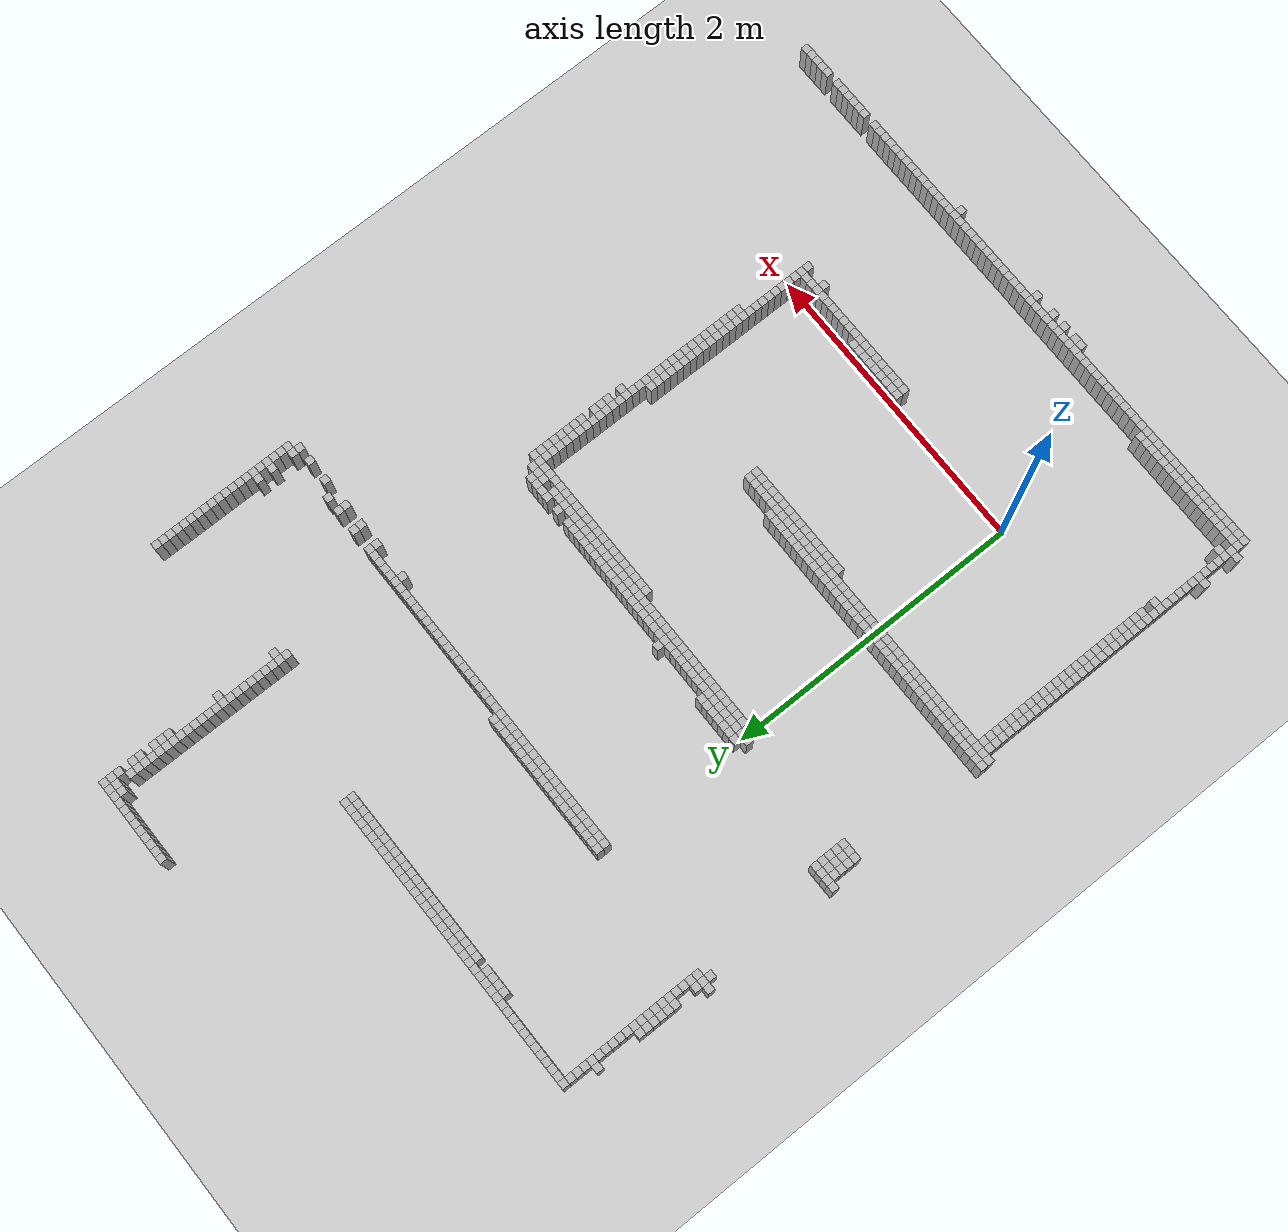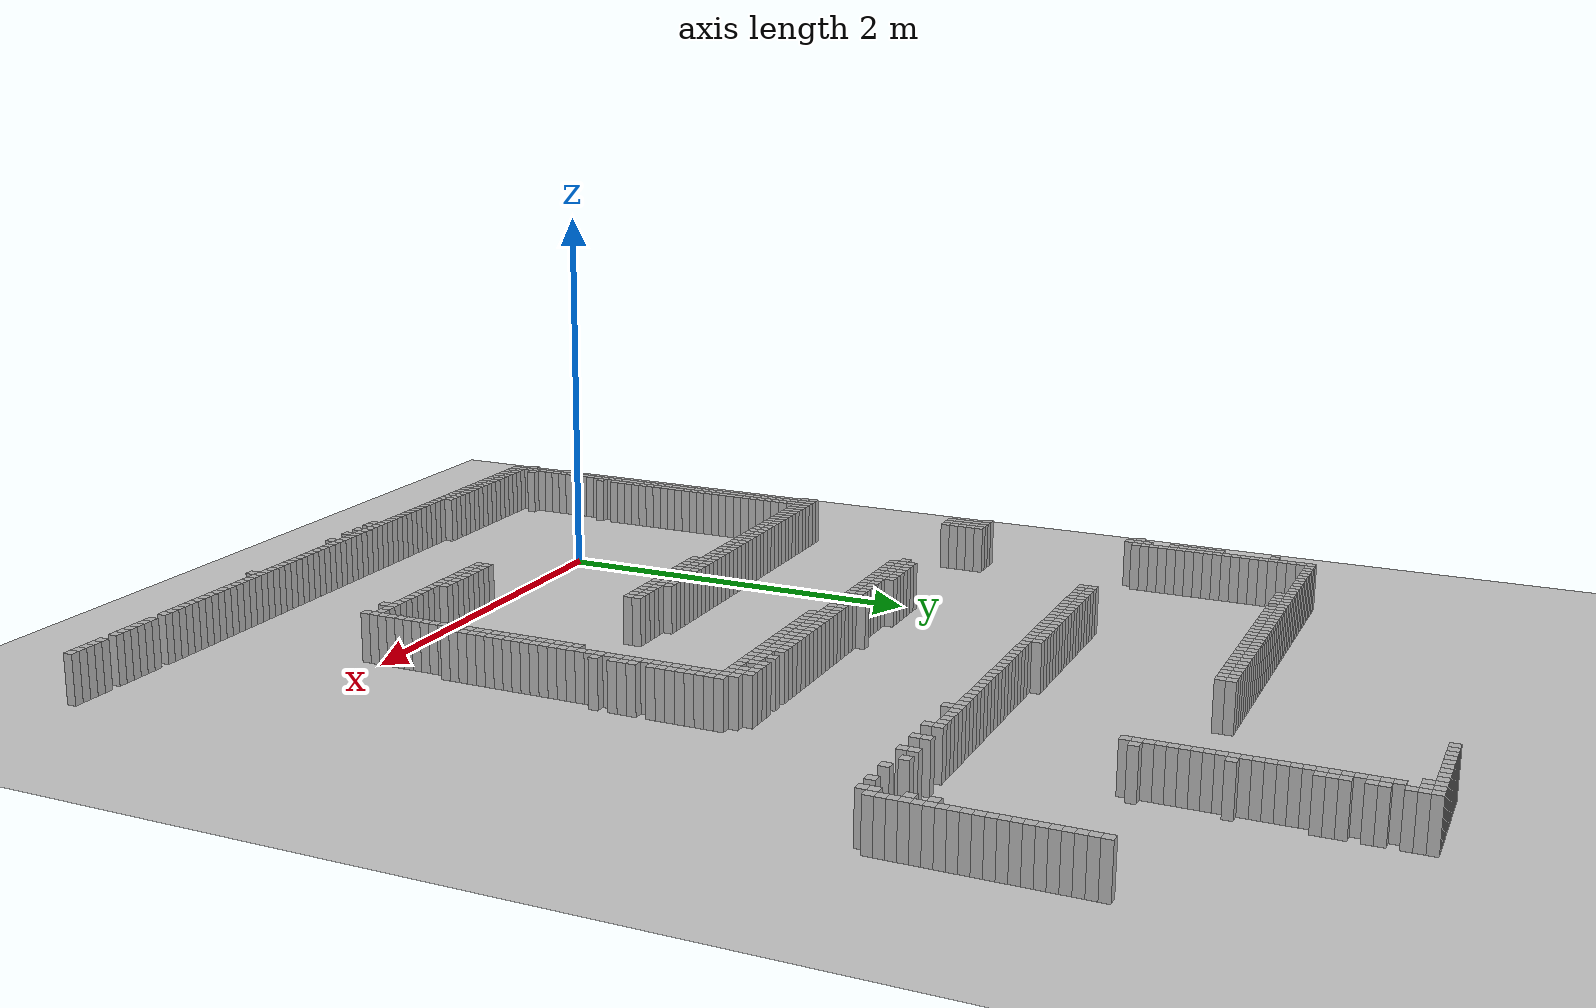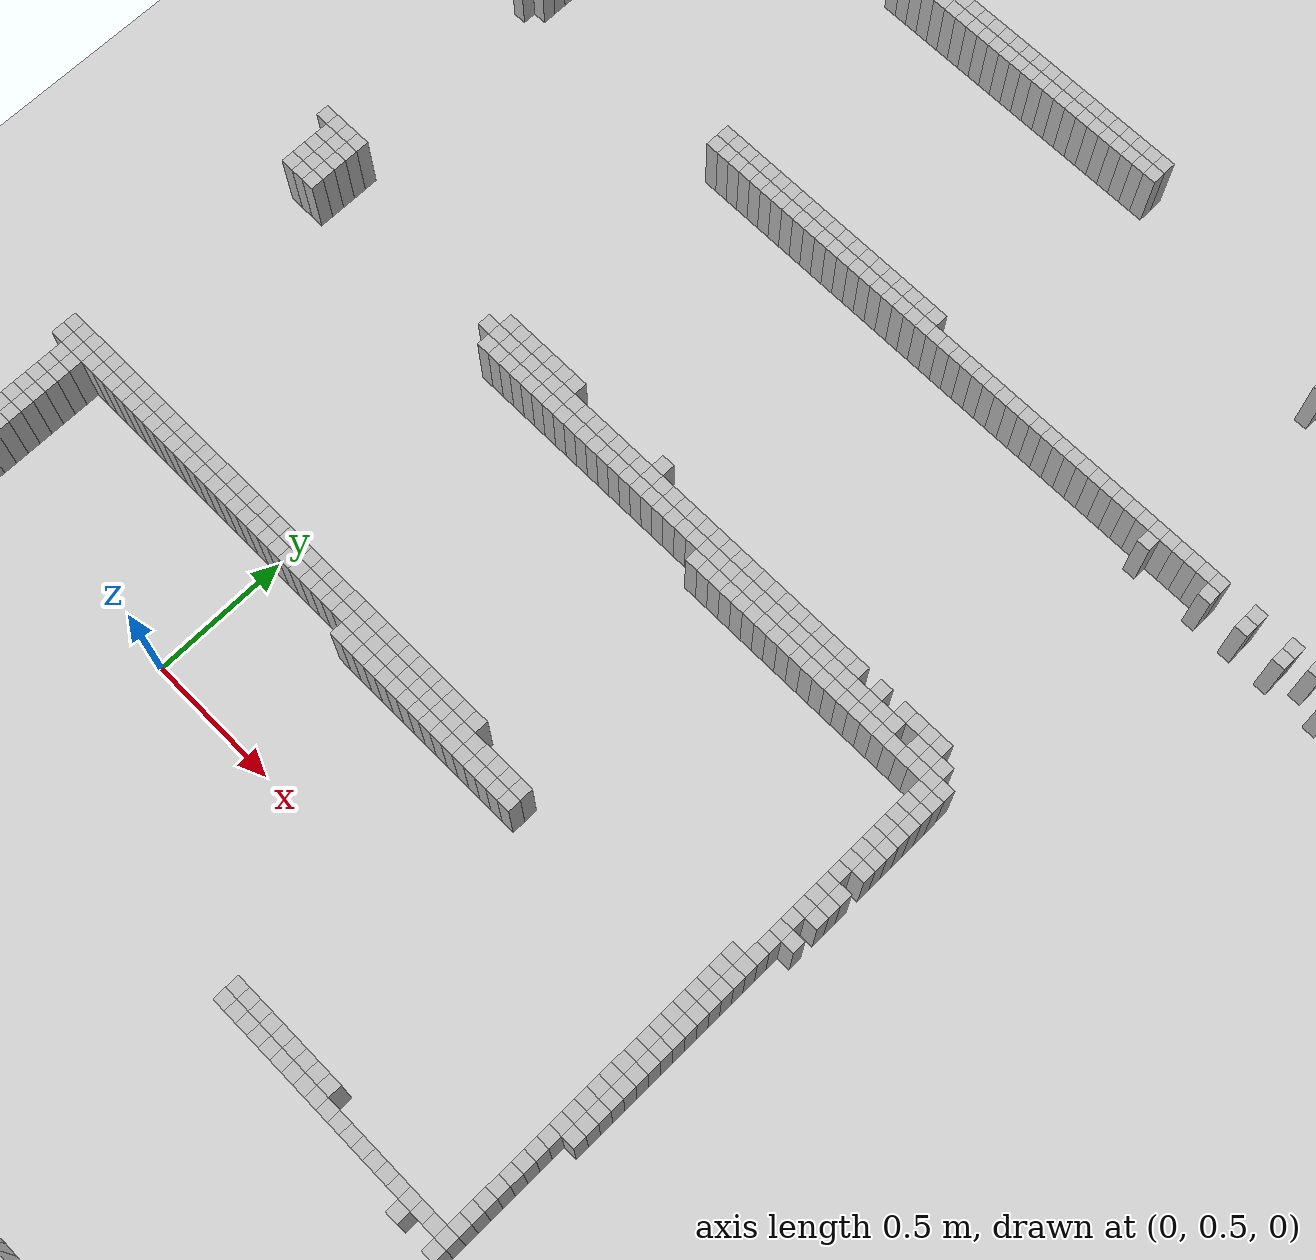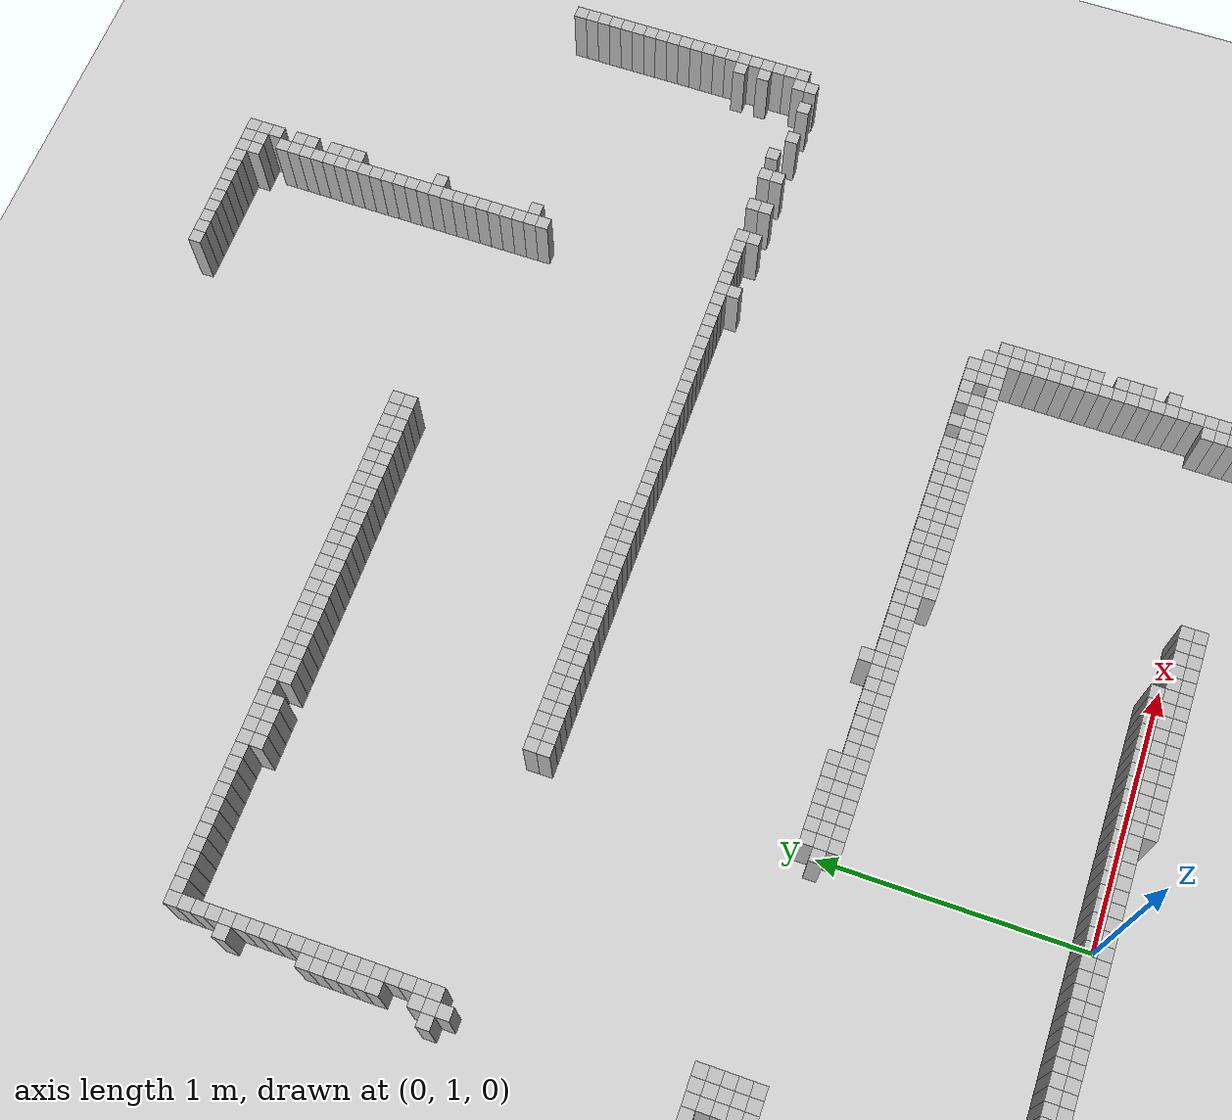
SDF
<sdf version="1.6"><world name="my_exploration_world"><include><uri>model://ground_plane</uri></include><include><uri>model://sun</uri></include><model name="obstacle_0"><pose>0.5500001572072506 -1.0499998666346073 0 0 0 0</pose><link name="link"><collision name="collision"><geometry><box><size>0.05000000074505806 0.05000000074505806 0.5</size></box></geometry></collision><visual name="visual"><geometry><box><size>0.05000000074505806 0.05000000074505806 0.5</size></box></geometry></visual></link><static>true</static></model><model name="obstacle_1"><pose>0.6000001579523087 -1.0499998666346073 0 0 0 0</pose><link name="link"><collision name="collision"><geometry><box><size>0.05000000074505806 0.05000000074505806 0.5</size></box></geometry></collision><visual name="visual"><geometry><box><size>0.05000000074505806 0.05000000074505806 0.5</size></box></geometry></visual></link><static>true</static></model><model name="obstacle_2"><pose>0.7000001594424248 -1.0499998666346073 0 0 0 0</pose><link name="link"><collision name="collision"><geometry><box><size>0.05000000074505806 0.05000000074505806 0.5</size></box></geometry></collision><visual name="visual"><geometry><box><size>0.05000000074505806 0.05000000074505806 0.5</size></box></geometry></visual></link><static>true</static></model><model name="obstacle_3"><pose>0.8000001609325409 -1.0499998666346073 0 0 0 0</pose><link name="link"><collision name="collision"><geometry><box><size>0.05000000074505806 0.05000000074505806 0.5</size></box></geometry></collision><visual name="visual"><geometry><box><size>0.05000000074505806 0.05000000074505806 0.5</size></box></geometry></visual></link><static>true</static></model><model name="obstacle_4"><pose>0.9500001631677151 -1.0499998666346073 0 0 0 0</pose><link name="link"><collision name="collision"><geometry><box><size>0.05000000074505806 0.05000000074505806 0.5</size></box></geometry></collision><visual name="visual"><geometry><box><size>0.05000000074505806 0.05000000074505806 0.5</size></box></geometry></visual></link><static>true</static></model><model name="obstacle_5"><pose>1.650000173598528 -1.0499998666346073 0 0 0 0</pose><link name="link"><collision name="collision"><geometry><box><size>0.05000000074505806 0.05000000074505806 0.5</size></box></geometry></collision><visual name="visual"><geometry><box><size>0.05000000074505806 0.05000000074505806 0.5</size></box></geometry></visual></link><static>true</static></model><model name="obstacle_6"><pose>-0.9499998651444912 -0.9999998658895493 0 0 0 0</pose><link name="link"><collision name="collision"><geometry><box><size>0.05000000074505806 0.05000000074505806 0.5</size></box></geometry></collision><visual name="visual"><geometry><box><size>0.05000000074505806 0.05000000074505806 0.5</size></box></geometry></visual></link><static>true</static></model><model name="obstacle_7"><pose>-0.8999998643994331 -0.9999998658895493 0 0 0 0</pose><link name="link"><collision name="collision"><geometry><box><size>0.05000000074505806 0.05000000074505806 0.5</size></box></geometry></collision><visual name="visual"><geometry><box><size>0.05000000074505806 0.05000000074505806 0.5</size></box></geometry></visual></link><static>true</static></model><model name="obstacle_8"><pose>-0.8499998636543751 -0.9999998658895493 0 0 0 0</pose><link name="link"><collision name="collision"><geometry><box><size>0.05000000074505806 0.05000000074505806 0.5</size></box></geometry></collision><visual name="visual"><geometry><box><size>0.05000000074505806 0.05000000074505806 0.5</size></box></geometry></visual></link><static>true</static></model><model name="obstacle_9"><pose>-0.799999862909317 -0.9999998658895493 0 0 0 0</pose><link name="link"><collision name="collision"><geometry><box><size>0.05000000074505806 0.05000000074505806 0.5</size></box></geometry></collision><visual name="visual"><geometry><box><size>0.05000000074505806 0.05000000074505806 0.5</size></box></geometry></visual></link><static>true</static></model><model name="obstacle_10"><pose>-0.749999862164259 -0.9999998658895493 0 0 0 0</pose><link name="link"><collision name="collision"><geometry><box><size>0.05000000074505806 0.05000000074505806 0.5</size></box></geometry></collision><visual name="visual"><geometry><box><size>0.05000000074505806 0.05000000074505806 0.5</size></box></geometry></visual></link><static>true</static></model><model name="obstacle_11"><pose>-0.6999998614192009 -0.9999998658895493 0 0 0 0</pose><link name="link"><collision name="collision"><geometry><box><size>0.05000000074505806 0.05000000074505806 0.5</size></box></geometry></collision><visual name="visual"><geometry><box><size>0.05000000074505806 0.05000000074505806 0.5</size></box></geometry></visual></link><static>true</static></model><model name="obstacle_12"><pose>-0.6499998606741428 -0.9999998658895493 0 0 0 0</pose><link name="link"><collision name="collision"><geometry><box><size>0.05000000074505806 0.05000000074505806 0.5</size></box></geometry></collision><visual name="visual"><geometry><box><size>0.05000000074505806 0.05000000074505806 0.5</size></box></geometry></visual></link><static>true</static></model><model name="obstacle_13"><pose>-0.5999998599290848 -0.9999998658895493 0 0 0 0</pose><link name="link"><collision name="collision"><geometry><box><size>0.05000000074505806 0.05000000074505806 0.5</size></box></geometry></collision><visual name="visual"><geometry><box><size>0.05000000074505806 0.05000000074505806 0.5</size></box></geometry></visual></link><static>true</static></model><model name="obstacle_14"><pose>-0.5499998591840267 -0.9999998658895493 0 0 0 0</pose><link name="link"><collision name="collision"><geometry><box><size>0.05000000074505806 0.05000000074505806 0.5</size></box></geometry></collision><visual name="visual"><geometry><box><size>0.05000000074505806 0.05000000074505806 0.5</size></box></geometry></visual></link><static>true</static></model><model name="obstacle_15"><pose>-0.49999985843896866 -0.9999998658895493 0 0 0 0</pose><link name="link"><collision name="collision"><geometry><box><size>0.05000000074505806 0.05000000074505806 0.5</size></box></geometry></collision><visual name="visual"><geometry><box><size>0.05000000074505806 0.05000000074505806 0.5</size></box></geometry></visual></link><static>true</static></model><model name="obstacle_16"><pose>-0.4499998576939106 -0.9999998658895493 0 0 0 0</pose><link name="link"><collision name="collision"><geometry><box><size>0.05000000074505806 0.05000000074505806 0.5</size></box></geometry></collision><visual name="visual"><geometry><box><size>0.05000000074505806 0.05000000074505806 0.5</size></box></geometry></visual></link><static>true</static></model><model name="obstacle_17"><pose>-0.39999985694885254 -0.9999998658895493 0 0 0 0</pose><link name="link"><collision name="collision"><geometry><box><size>0.05000000074505806 0.05000000074505806 0.5</size></box></geometry></collision><visual name="visual"><geometry><box><size>0.05000000074505806 0.05000000074505806 0.5</size></box></geometry></visual></link><static>true</static></model><model name="obstacle_18"><pose>-0.3499998562037945 -0.9999998658895493 0 0 0 0</pose><link name="link"><collision name="collision"><geometry><box><size>0.05000000074505806 0.05000000074505806 0.5</size></box></geometry></collision><visual name="visual"><geometry><box><size>0.05000000074505806 0.05000000074505806 0.5</size></box></geometry></visual></link><static>true</static></model><model name="obstacle_19"><pose>-0.2999998554587364 -0.9999998658895493 0 0 0 0</pose><link name="link"><collision name="collision"><geometry><box><size>0.05000000074505806 0.05000000074505806 0.5</size></box></geometry></collision><visual name="visual"><geometry><box><size>0.05000000074505806 0.05000000074505806 0.5</size></box></geometry></visual></link><static>true</static></model><model name="obstacle_20"><pose>-0.24999985471367836 -0.9999998658895493 0 0 0 0</pose><link name="link"><collision name="collision"><geometry><box><size>0.05000000074505806 0.05000000074505806 0.5</size></box></geometry></collision><visual name="visual"><geometry><box><size>0.05000000074505806 0.05000000074505806 0.5</size></box></geometry></visual></link><static>true</static></model><model name="obstacle_21"><pose>-0.1999998539686203 -0.9999998658895493 0 0 0 0</pose><link name="link"><collision name="collision"><geometry><box><size>0.05000000074505806 0.05000000074505806 0.5</size></box></geometry></collision><visual name="visual"><geometry><box><size>0.05000000074505806 0.05000000074505806 0.5</size></box></geometry></visual></link><static>true</static></model><model name="obstacle_22"><pose>-0.14999985322356224 -0.9999998658895493 0 0 0 0</pose><link name="link"><collision name="collision"><geometry><box><size>0.05000000074505806 0.05000000074505806 0.5</size></box></geometry></collision><visual name="visual"><geometry><box><size>0.05000000074505806 0.05000000074505806 0.5</size></box></geometry></visual></link><static>true</static></model><model name="obstacle_23"><pose>-0.09999985247850418 -0.9999998658895493 0 0 0 0</pose><link name="link"><collision name="collision"><geometry><box><size>0.05000000074505806 0.05000000074505806 0.5</size></box></geometry></collision><visual name="visual"><geometry><box><size>0.05000000074505806 0.05000000074505806 0.5</size></box></geometry></visual></link><static>true</static></model><model name="obstacle_24"><pose>-0.04999985173344612 -0.9999998658895493 0 0 0 0</pose><link name="link"><collision name="collision"><geometry><box><size>0.05000000074505806 0.05000000074505806 0.5</size></box></geometry></collision><visual name="visual"><geometry><box><size>0.05000000074505806 0.05000000074505806 0.5</size></box></geometry></visual></link><static>true</static></model><model name="obstacle_25"><pose>1.4901161193847656e-07 -0.9999998658895493 0 0 0 0</pose><link name="link"><collision name="collision"><geometry><box><size>0.05000000074505806 0.05000000074505806 0.5</size></box></geometry></collision><visual name="visual"><geometry><box><size>0.05000000074505806 0.05000000074505806 0.5</size></box></geometry></visual></link><static>true</static></model><model name="obstacle_26"><pose>0.05000014975667 -0.9999998658895493 0 0 0 0</pose><link name="link"><collision name="collision"><geometry><box><size>0.05000000074505806 0.05000000074505806 0.5</size></box></geometry></collision><visual name="visual"><geometry><box><size>0.05000000074505806 0.05000000074505806 0.5</size></box></geometry></visual></link><static>true</static></model><model name="obstacle_27"><pose>0.10000015050172806 -0.9999998658895493 0 0 0 0</pose><link name="link"><collision name="collision"><geometry><box><size>0.05000000074505806 0.05000000074505806 0.5</size></box></geometry></collision><visual name="visual"><geometry><box><size>0.05000000074505806 0.05000000074505806 0.5</size></box></geometry></visual></link><static>true</static></model><model name="obstacle_28"><pose>0.15000015124678612 -0.9999998658895493 0 0 0 0</pose><link name="link"><collision name="collision"><geometry><box><size>0.05000000074505806 0.05000000074505806 0.5</size></box></geometry></collision><visual name="visual"><geometry><box><size>0.05000000074505806 0.05000000074505806 0.5</size></box></geometry></visual></link><static>true</static></model><model name="obstacle_29"><pose>0.20000015199184418 -0.9999998658895493 0 0 0 0</pose><link name="link"><collision name="collision"><geometry><box><size>0.05000000074505806 0.05000000074505806 0.5</size></box></geometry></collision><visual name="visual"><geometry><box><size>0.05000000074505806 0.05000000074505806 0.5</size></box></geometry></visual></link><static>true</static></model><model name="obstacle_30"><pose>0.25000015273690224 -0.9999998658895493 0 0 0 0</pose><link name="link"><collision name="collision"><geometry><box><size>0.05000000074505806 0.05000000074505806 0.5</size></box></geometry></collision><visual name="visual"><geometry><box><size>0.05000000074505806 0.05000000074505806 0.5</size></box></geometry></visual></link><static>true</static></model><model name="obstacle_31"><pose>0.3000001534819603 -0.9999998658895493 0 0 0 0</pose><link name="link"><collision name="collision"><geometry><box><size>0.05000000074505806 0.05000000074505806 0.5</size></box></geometry></collision><visual name="visual"><geometry><box><size>0.05000000074505806 0.05000000074505806 0.5</size></box></geometry></visual></link><static>true</static></model><model name="obstacle_32"><pose>0.35000015422701836 -0.9999998658895493 0 0 0 0</pose><link name="link"><collision name="collision"><geometry><box><size>0.05000000074505806 0.05000000074505806 0.5</size></box></geometry></collision><visual name="visual"><geometry><box><size>0.05000000074505806 0.05000000074505806 0.5</size></box></geometry></visual></link><static>true</static></model><model name="obstacle_33"><pose>0.4000001549720764 -0.9999998658895493 0 0 0 0</pose><link name="link"><collision name="collision"><geometry><box><size>0.05000000074505806 0.05000000074505806 0.5</size></box></geometry></collision><visual name="visual"><geometry><box><size>0.05000000074505806 0.05000000074505806 0.5</size></box></geometry></visual></link><static>true</static></model><model name="obstacle_34"><pose>0.4500001557171345 -0.9999998658895493 0 0 0 0</pose><link name="link"><collision name="collision"><geometry><box><size>0.05000000074505806 0.05000000074505806 0.5</size></box></geometry></collision><visual name="visual"><geometry><box><size>0.05000000074505806 0.05000000074505806 0.5</size></box></geometry></visual></link><static>true</static></model><model name="obstacle_35"><pose>0.5000001564621925 -0.9999998658895493 0 0 0 0</pose><link name="link"><collision name="collision"><geometry><box><size>0.05000000074505806 0.05000000074505806 0.5</size></box></geometry></collision><visual name="visual"><geometry><box><size>0.05000000074505806 0.05000000074505806 0.5</size></box></geometry></visual></link><static>true</static></model><model name="obstacle_36"><pose>0.5500001572072506 -0.9999998658895493 0 0 0 0</pose><link name="link"><collision name="collision"><geometry><box><size>0.05000000074505806 0.05000000074505806 0.5</size></box></geometry></collision><visual name="visual"><geometry><box><size>0.05000000074505806 0.05000000074505806 0.5</size></box></geometry></visual></link><static>true</static></model><model name="obstacle_37"><pose>0.6000001579523087 -0.9999998658895493 0 0 0 0</pose><link name="link"><collision name="collision"><geometry><box><size>0.05000000074505806 0.05000000074505806 0.5</size></box></geometry></collision><visual name="visual"><geometry><box><size>0.05000000074505806 0.05000000074505806 0.5</size></box></geometry></visual></link><static>true</static></model><model name="obstacle_38"><pose>0.6500001586973667 -0.9999998658895493 0 0 0 0</pose><link name="link"><collision name="collision"><geometry><box><size>0.05000000074505806 0.05000000074505806 0.5</size></box></geometry></collision><visual name="visual"><geometry><box><size>0.05000000074505806 0.05000000074505806 0.5</size></box></geometry></visual></link><static>true</static></model><model name="obstacle_39"><pose>0.7000001594424248 -0.9999998658895493 0 0 0 0</pose><link name="link"><collision name="collision"><geometry><box><size>0.05000000074505806 0.05000000074505806 0.5</size></box></geometry></collision><visual name="visual"><geometry><box><size>0.05000000074505806 0.05000000074505806 0.5</size></box></geometry></visual></link><static>true</static></model><model name="obstacle_40"><pose>0.7500001601874828 -0.9999998658895493 0 0 0 0</pose><link name="link"><collision name="collision"><geometry><box><size>0.05000000074505806 0.05000000074505806 0.5</size></box></geometry></collision><visual name="visual"><geometry><box><size>0.05000000074505806 0.05000000074505806 0.5</size></box></geometry></visual></link><static>true</static></model><model name="obstacle_41"><pose>0.8000001609325409 -0.9999998658895493 0 0 0 0</pose><link name="link"><collision name="collision"><geometry><box><size>0.05000000074505806 0.05000000074505806 0.5</size></box></geometry></collision><visual name="visual"><geometry><box><size>0.05000000074505806 0.05000000074505806 0.5</size></box></geometry></visual></link><static>true</static></model><model name="obstacle_42"><pose>0.850000161677599 -0.9999998658895493 0 0 0 0</pose><link name="link"><collision name="collision"><geometry><box><size>0.05000000074505806 0.05000000074505806 0.5</size></box></geometry></collision><visual name="visual"><geometry><box><size>0.05000000074505806 0.05000000074505806 0.5</size></box></geometry></visual></link><static>true</static></model><model name="obstacle_43"><pose>0.900000162422657 -0.9999998658895493 0 0 0 0</pose><link name="link"><collision name="collision"><geometry><box><size>0.05000000074505806 0.05000000074505806 0.5</size></box></geometry></collision><visual name="visual"><geometry><box><size>0.05000000074505806 0.05000000074505806 0.5</size></box></geometry></visual></link><static>true</static></model><model name="obstacle_44"><pose>0.9500001631677151 -0.9999998658895493 0 0 0 0</pose><link name="link"><collision name="collision"><geometry><box><size>0.05000000074505806 0.05000000074505806 0.5</size></box></geometry></collision><visual name="visual"><geometry><box><size>0.05000000074505806 0.05000000074505806 0.5</size></box></geometry></visual></link><static>true</static></model><model name="obstacle_45"><pose>1.0000001639127731 -0.9999998658895493 0 0 0 0</pose><link name="link"><collision name="collision"><geometry><box><size>0.05000000074505806 0.05000000074505806 0.5</size></box></geometry></collision><visual name="visual"><geometry><box><size>0.05000000074505806 0.05000000074505806 0.5</size></box></geometry></visual></link><static>true</static></model><model name="obstacle_46"><pose>1.0500001646578312 -0.9999998658895493 0 0 0 0</pose><link name="link"><collision name="collision"><geometry><box><size>0.05000000074505806 0.05000000074505806 0.5</size></box></geometry></collision><visual name="visual"><geometry><box><size>0.05000000074505806 0.05000000074505806 0.5</size></box></geometry></visual></link><static>true</static></model><model name="obstacle_47"><pose>1.1000001654028893 -0.9999998658895493 0 0 0 0</pose><link name="link"><collision name="collision"><geometry><box><size>0.05000000074505806 0.05000000074505806 0.5</size></box></geometry></collision><visual name="visual"><geometry><box><size>0.05000000074505806 0.05000000074505806 0.5</size></box></geometry></visual></link><static>true</static></model><model name="obstacle_48"><pose>1.1500001661479473 -0.9999998658895493 0 0 0 0</pose><link name="link"><collision name="collision"><geometry><box><size>0.05000000074505806 0.05000000074505806 0.5</size></box></geometry></collision><visual name="visual"><geometry><box><size>0.05000000074505806 0.05000000074505806 0.5</size></box></geometry></visual></link><static>true</static></model><model name="obstacle_49"><pose>1.2000001668930054 -0.9999998658895493 0 0 0 0</pose><link name="link"><collision name="collision"><geometry><box><size>0.05000000074505806 0.05000000074505806 0.5</size></box></geometry></collision><visual name="visual"><geometry><box><size>0.05000000074505806 0.05000000074505806 0.5</size></box></geometry></visual></link><static>true</static></model><model name="obstacle_50"><pose>1.2500001676380634 -0.9999998658895493 0 0 0 0</pose><link name="link"><collision name="collision"><geometry><box><size>0.05000000074505806 0.05000000074505806 0.5</size></box></geometry></collision><visual name="visual"><geometry><box><size>0.05000000074505806 0.05000000074505806 0.5</size></box></geometry></visual></link><static>true</static></model><model name="obstacle_51"><pose>1.3000001683831215 -0.9999998658895493 0 0 0 0</pose><link name="link"><collision name="collision"><geometry><box><size>0.05000000074505806 0.05000000074505806 0.5</size></box></geometry></collision><visual name="visual"><geometry><box><size>0.05000000074505806 0.05000000074505806 0.5</size></box></geometry></visual></link><static>true</static></model><model name="obstacle_52"><pose>1.3500001691281796 -0.9999998658895493 0 0 0 0</pose><link name="link"><collision name="collision"><geometry><box><size>0.05000000074505806 0.05000000074505806 0.5</size></box></geometry></collision><visual name="visual"><geometry><box><size>0.05000000074505806 0.05000000074505806 0.5</size></box></geometry></visual></link><static>true</static></model><model name="obstacle_53"><pose>1.4000001698732376 -0.9999998658895493 0 0 0 0</pose><link name="link"><collision name="collision"><geometry><box><size>0.05000000074505806 0.05000000074505806 0.5</size></box></geometry></collision><visual name="visual"><geometry><box><size>0.05000000074505806 0.05000000074505806 0.5</size></box></geometry></visual></link><static>true</static></model><model name="obstacle_54"><pose>1.4500001706182957 -0.9999998658895493 0 0 0 0</pose><link name="link"><collision name="collision"><geometry><box><size>0.05000000074505806 0.05000000074505806 0.5</size></box></geometry></collision><visual name="visual"><geometry><box><size>0.05000000074505806 0.05000000074505806 0.5</size></box></geometry></visual></link><static>true</static></model><model name="obstacle_55"><pose>1.5000001713633537 -0.9999998658895493 0 0 0 0</pose><link name="link"><collision name="collision"><geometry><box><size>0.05000000074505806 0.05000000074505806 0.5</size></box></geometry></collision><visual name="visual"><geometry><box><size>0.05000000074505806 0.05000000074505806 0.5</size></box></geometry></visual></link><static>true</static></model><model name="obstacle_56"><pose>1.5500001721084118 -0.9999998658895493 0 0 0 0</pose><link name="link"><collision name="collision"><geometry><box><size>0.05000000074505806 0.05000000074505806 0.5</size></box></geometry></collision><visual name="visual"><geometry><box><size>0.05000000074505806 0.05000000074505806 0.5</size></box></geometry></visual></link><static>true</static></model><model name="obstacle_57"><pose>1.6000001728534698 -0.9999998658895493 0 0 0 0</pose><link name="link"><collision name="collision"><geometry><box><size>0.05000000074505806 0.05000000074505806 0.5</size></box></geometry></collision><visual name="visual"><geometry><box><size>0.05000000074505806 0.05000000074505806 0.5</size></box></geometry></visual></link><static>true</static></model><model name="obstacle_58"><pose>1.650000173598528 -0.9999998658895493 0 0 0 0</pose><link name="link"><collision name="collision"><geometry><box><size>0.05000000074505806 0.05000000074505806 0.5</size></box></geometry></collision><visual name="visual"><geometry><box><size>0.05000000074505806 0.05000000074505806 0.5</size></box></geometry></visual></link><static>true</static></model><model name="obstacle_59"><pose>1.700000174343586 -0.9999998658895493 0 0 0 0</pose><link name="link"><collision name="collision"><geometry><box><size>0.05000000074505806 0.05000000074505806 0.5</size></box></geometry></collision><visual name="visual"><geometry><box><size>0.05000000074505806 0.05000000074505806 0.5</size></box></geometry></visual></link><static>true</static></model><model name="obstacle_60"><pose>1.750000175088644 -0.9999998658895493 0 0 0 0</pose><link name="link"><collision name="collision"><geometry><box><size>0.05000000074505806 0.05000000074505806 0.5</size></box></geometry></collision><visual name="visual"><geometry><box><size>0.05000000074505806 0.05000000074505806 0.5</size></box></geometry></visual></link><static>true</static></model><model name="obstacle_61"><pose>1.800000175833702 -0.9999998658895493 0 0 0 0</pose><link name="link"><collision name="collision"><geometry><box><size>0.05000000074505806 0.05000000074505806 0.5</size></box></geometry></collision><visual name="visual"><geometry><box><size>0.05000000074505806 0.05000000074505806 0.5</size></box></geometry></visual></link><static>true</static></model><model name="obstacle_62"><pose>1.8500001765787601 -0.9999998658895493 0 0 0 0</pose><link name="link"><collision name="collision"><geometry><box><size>0.05000000074505806 0.05000000074505806 0.5</size></box></geometry></collision><visual name="visual"><geometry><box><size>0.05000000074505806 0.05000000074505806 0.5</size></box></geometry></visual></link><static>true</static></model><model name="obstacle_63"><pose>1.9000001773238182 -0.9999998658895493 0 0 0 0</pose><link name="link"><collision name="collision"><geometry><box><size>0.05000000074505806 0.05000000074505806 0.5</size></box></geometry></collision><visual name="visual"><geometry><box><size>0.05000000074505806 0.05000000074505806 0.5</size></box></geometry></visual></link><static>true</static></model><model name="obstacle_64"><pose>1.9500001780688763 -0.9999998658895493 0 0 0 0</pose><link name="link"><collision name="collision"><geometry><box><size>0.05000000074505806 0.05000000074505806 0.5</size></box></geometry></collision><visual name="visual"><geometry><box><size>0.05000000074505806 0.05000000074505806 0.5</size></box></geometry></visual></link><static>true</static></model><model name="obstacle_65"><pose>2.0000001788139343 -0.9999998658895493 0 0 0 0</pose><link name="link"><collision name="collision"><geometry><box><size>0.05000000074505806 0.05000000074505806 0.5</size></box></geometry></collision><visual name="visual"><geometry><box><size>0.05000000074505806 0.05000000074505806 0.5</size></box></geometry></visual></link><static>true</static></model><model name="obstacle_66"><pose>2.0500001795589924 -0.9999998658895493 0 0 0 0</pose><link name="link"><collision name="collision"><geometry><box><size>0.05000000074505806 0.05000000074505806 0.5</size></box></geometry></collision><visual name="visual"><geometry><box><size>0.05000000074505806 0.05000000074505806 0.5</size></box></geometry></visual></link><static>true</static></model><model name="obstacle_67"><pose>2.1000001803040504 -0.9999998658895493 0 0 0 0</pose><link name="link"><collision name="collision"><geometry><box><size>0.05000000074505806 0.05000000074505806 0.5</size></box></geometry></collision><visual name="visual"><geometry><box><size>0.05000000074505806 0.05000000074505806 0.5</size></box></geometry></visual></link><static>true</static></model><model name="obstacle_68"><pose>2.1500001810491085 -0.9999998658895493 0 0 0 0</pose><link name="link"><collision name="collision"><geometry><box><size>0.05000000074505806 0.05000000074505806 0.5</size></box></geometry></collision><visual name="visual"><geometry><box><size>0.05000000074505806 0.05000000074505806 0.5</size></box></geometry></visual></link><static>true</static></model><model name="obstacle_69"><pose>2.2000001817941666 -0.9999998658895493 0 0 0 0</pose><link name="link"><collision name="collision"><geometry><box><size>0.05000000074505806 0.05000000074505806 0.5</size></box></geometry></collision><visual name="visual"><geometry><box><size>0.05000000074505806 0.05000000074505806 0.5</size></box></geometry></visual></link><static>true</static></model><model name="obstacle_70"><pose>2.2500001825392246 -0.9999998658895493 0 0 0 0</pose><link name="link"><collision name="collision"><geometry><box><size>0.05000000074505806 0.05000000074505806 0.5</size></box></geometry></collision><visual name="visual"><geometry><box><size>0.05000000074505806 0.05000000074505806 0.5</size></box></geometry></visual></link><static>true</static></model><model name="obstacle_71"><pose>2.3000001832842827 -0.9999998658895493 0 0 0 0</pose><link name="link"><collision name="collision"><geometry><box><size>0.05000000074505806 0.05000000074505806 0.5</size></box></geometry></collision><visual name="visual"><geometry><box><size>0.05000000074505806 0.05000000074505806 0.5</size></box></geometry></visual></link><static>true</static></model><model name="obstacle_72"><pose>2.3500001840293407 -0.9999998658895493 0 0 0 0</pose><link name="link"><collision name="collision"><geometry><box><size>0.05000000074505806 0.05000000074505806 0.5</size></box></geometry></collision><visual name="visual"><geometry><box><size>0.05000000074505806 0.05000000074505806 0.5</size></box></geometry></visual></link><static>true</static></model><model name="obstacle_73"><pose>2.400000184774399 -0.9999998658895493 0 0 0 0</pose><link name="link"><collision name="collision"><geometry><box><size>0.05000000074505806 0.05000000074505806 0.5</size></box></geometry></collision><visual name="visual"><geometry><box><size>0.05000000074505806 0.05000000074505806 0.5</size></box></geometry></visual></link><static>true</static></model><model name="obstacle_74"><pose>2.500000186264515 -0.9999998658895493 0 0 0 0</pose><link name="link"><collision name="collision"><geometry><box><size>0.05000000074505806 0.05000000074505806 0.5</size></box></geometry></collision><visual name="visual"><geometry><box><size>0.05000000074505806 0.05000000074505806 0.5</size></box></geometry></visual></link><static>true</static></model><model name="obstacle_75"><pose>2.550000187009573 -0.9999998658895493 0 0 0 0</pose><link name="link"><collision name="collision"><geometry><box><size>0.05000000074505806 0.05000000074505806 0.5</size></box></geometry></collision><visual name="visual"><geometry><box><size>0.05000000074505806 0.05000000074505806 0.5</size></box></geometry></visual></link><static>true</static></model><model name="obstacle_76"><pose>2.600000187754631 -0.9999998658895493 0 0 0 0</pose><link name="link"><collision name="collision"><geometry><box><size>0.05000000074505806 0.05000000074505806 0.5</size></box></geometry></collision><visual name="visual"><geometry><box><size>0.05000000074505806 0.05000000074505806 0.5</size></box></geometry></visual></link><static>true</static></model><model name="obstacle_77"><pose>2.650000188499689 -0.9999998658895493 0 0 0 0</pose><link name="link"><collision name="collision"><geometry><box><size>0.05000000074505806 0.05000000074505806 0.5</size></box></geometry></collision><visual name="visual"><geometry><box><size>0.05000000074505806 0.05000000074505806 0.5</size></box></geometry></visual></link><static>true</static></model><model name="obstacle_78"><pose>2.700000189244747 -0.9999998658895493 0 0 0 0</pose><link name="link"><collision name="collision"><geometry><box><size>0.05000000074505806 0.05000000074505806 0.5</size></box></geometry></collision><visual name="visual"><geometry><box><size>0.05000000074505806 0.05000000074505806 0.5</size></box></geometry></visual></link><static>true</static></model><model name="obstacle_79"><pose>2.750000189989805 -0.9999998658895493 0 0 0 0</pose><link name="link"><collision name="collision"><geometry><box><size>0.05000000074505806 0.05000000074505806 0.5</size></box></geometry></collision><visual name="visual"><geometry><box><size>0.05000000074505806 0.05000000074505806 0.5</size></box></geometry></visual></link><static>true</static></model><model name="obstacle_80"><pose>2.8500001914799213 -0.9999998658895493 0 0 0 0</pose><link name="link"><collision name="collision"><geometry><box><size>0.05000000074505806 0.05000000074505806 0.5</size></box></geometry></collision><visual name="visual"><geometry><box><size>0.05000000074505806 0.05000000074505806 0.5</size></box></geometry></visual></link><static>true</static></model><model name="obstacle_81"><pose>2.9000001922249794 -0.9999998658895493 0 0 0 0</pose><link name="link"><collision name="collision"><geometry><box><size>0.05000000074505806 0.05000000074505806 0.5</size></box></geometry></collision><visual name="visual"><geometry><box><size>0.05000000074505806 0.05000000074505806 0.5</size></box></geometry></visual></link><static>true</static></model><model name="obstacle_82"><pose>2.9500001929700375 -0.9999998658895493 0 0 0 0</pose><link name="link"><collision name="collision"><geometry><box><size>0.05000000074505806 0.05000000074505806 0.5</size></box></geometry></collision><visual name="visual"><geometry><box><size>0.05000000074505806 0.05000000074505806 0.5</size></box></geometry></visual></link><static>true</static></model><model name="obstacle_83"><pose>3.0000001937150955 -0.9999998658895493 0 0 0 0</pose><link name="link"><collision name="collision"><geometry><box><size>0.05000000074505806 0.05000000074505806 0.5</size></box></geometry></collision><visual name="visual"><geometry><box><size>0.05000000074505806 0.05000000074505806 0.5</size></box></geometry></visual></link><static>true</static></model><model name="obstacle_84"><pose>3.0500001944601536 -0.9999998658895493 0 0 0 0</pose><link name="link"><collision name="collision"><geometry><box><size>0.05000000074505806 0.05000000074505806 0.5</size></box></geometry></collision><visual name="visual"><geometry><box><size>0.05000000074505806 0.05000000074505806 0.5</size></box></geometry></visual></link><static>true</static></model><model name="obstacle_85"><pose>-0.9499998651444912 -0.9499998651444912 0 0 0 0</pose><link name="link"><collision name="collision"><geometry><box><size>0.05000000074505806 0.05000000074505806 0.5</size></box></geometry></collision><visual name="visual"><geometry><box><size>0.05000000074505806 0.05000000074505806 0.5</size></box></geometry></visual></link><static>true</static></model><model name="obstacle_86"><pose>-0.8999998643994331 -0.9499998651444912 0 0 0 0</pose><link name="link"><collision name="collision"><geometry><box><size>0.05000000074505806 0.05000000074505806 0.5</size></box></geometry></collision><visual name="visual"><geometry><box><size>0.05000000074505806 0.05000000074505806 0.5</size></box></geometry></visual></link><static>true</static></model><model name="obstacle_87"><pose>-0.8499998636543751 -0.9499998651444912 0 0 0 0</pose><link name="link"><collision name="collision"><geometry><box><size>0.05000000074505806 0.05000000074505806 0.5</size></box></geometry></collision><visual name="visual"><geometry><box><size>0.05000000074505806 0.05000000074505806 0.5</size></box></geometry></visual></link><static>true</static></model><model name="obstacle_88"><pose>-0.799999862909317 -0.9499998651444912 0 0 0 0</pose><link name="link"><collision name="collision"><geometry><box><size>0.05000000074505806 0.05000000074505806 0.5</size></box></geometry></collision><visual name="visual"><geometry><box><size>0.05000000074505806 0.05000000074505806 0.5</size></box></geometry></visual></link><static>true</static></model><model name="obstacle_89"><pose>-0.749999862164259 -0.9499998651444912 0 0 0 0</pose><link name="link"><collision name="collision"><geometry><box><size>0.05000000074505806 0.05000000074505806 0.5</size></box></geometry></collision><visual name="visual"><geometry><box><size>0.05000000074505806 0.05000000074505806 0.5</size></box></geometry></visual></link><static>true</static></model><model name="obstacle_90"><pose>-0.6999998614192009 -0.9499998651444912 0 0 0 0</pose><link name="link"><collision name="collision"><geometry><box><size>0.05000000074505806 0.05000000074505806 0.5</size></box></geometry></collision><visual name="visual"><geometry><box><size>0.05000000074505806 0.05000000074505806 0.5</size></box></geometry></visual></link><static>true</static></model><model name="obstacle_91"><pose>-0.6499998606741428 -0.9499998651444912 0 0 0 0</pose><link name="link"><collision name="collision"><geometry><box><size>0.05000000074505806 0.05000000074505806 0.5</size></box></geometry></collision><visual name="visual"><geometry><box><size>0.05000000074505806 0.05000000074505806 0.5</size></box></geometry></visual></link><static>true</static></model><model name="obstacle_92"><pose>-0.5999998599290848 -0.9499998651444912 0 0 0 0</pose><link name="link"><collision name="collision"><geometry><box><size>0.05000000074505806 0.05000000074505806 0.5</size></box></geometry></collision><visual name="visual"><geometry><box><size>0.05000000074505806 0.05000000074505806 0.5</size></box></geometry></visual></link><static>true</static></model><model name="obstacle_93"><pose>-0.5499998591840267 -0.9499998651444912 0 0 0 0</pose><link name="link"><collision name="collision"><geometry><box><size>0.05000000074505806 0.05000000074505806 0.5</size></box></geometry></collision><visual name="visual"><geometry><box><size>0.05000000074505806 0.05000000074505806 0.5</size></box></geometry></visual></link><static>true</static></model><model name="obstacle_94"><pose>-0.49999985843896866 -0.9499998651444912 0 0 0 0</pose><link name="link"><collision name="collision"><geometry><box><size>0.05000000074505806 0.05000000074505806 0.5</size></box></geometry></collision><visual name="visual"><geometry><box><size>0.05000000074505806 0.05000000074505806 0.5</size></box></geometry></visual></link><static>true</static></model><model name="obstacle_95"><pose>-0.4499998576939106 -0.9499998651444912 0 0 0 0</pose><link name="link"><collision name="collision"><geometry><box><size>0.05000000074505806 0.05000000074505806 0.5</size></box></geometry></collision><visual name="visual"><geometry><box><size>0.05000000074505806 0.05000000074505806 0.5</size></box></geometry></visual></link><static>true</static></model><model name="obstacle_96"><pose>-0.39999985694885254 -0.9499998651444912 0 0 0 0</pose><link name="link"><collision name="collision"><geometry><box><size>0.05000000074505806 0.05000000074505806 0.5</size></box></geometry></collision><visual name="visual"><geometry><box><size>0.05000000074505806 0.05000000074505806 0.5</size></box></geometry></visual></link><static>true</static></model><model name="obstacle_97"><pose>-0.3499998562037945 -0.9499998651444912 0 0 0 0</pose><link name="link"><collision name="collision"><geometry><box><size>0.05000000074505806 0.05000000074505806 0.5</size></box></geometry></collision><visual name="visual"><geometry><box><size>0.05000000074505806 0.05000000074505806 0.5</size></box></geometry></visual></link><static>true</static></model><model name="obstacle_98"><pose>-0.2999998554587364 -0.9499998651444912 0 0 0 0</pose><link name="link"><collision name="collision"><geometry><box><size>0.05000000074505806 0.05000000074505806 0.5</size></box></geometry></collision><visual name="visual"><geometry><box><size>0.05000000074505806 0.05000000074505806 0.5</size></box></geometry></visual></link><static>true</static></model><model name="obstacle_99"><pose>-0.24999985471367836 -0.9499998651444912 0 0 0 0</pose><link name="link"><collision name="collision"><geometry><box><size>0.05000000074505806 0.05000000074505806 0.5</size></box></geometry></collision><visual name="visual"><geometry><box><size>0.05000000074505806 0.05000000074505806 0.5</size></box></geometry></visual></link><static>true</static></model><model name="obstacle_100"><pose>-0.1999998539686203 -0.9499998651444912 0 0 0 0</pose><link name="link"><collision name="collision"><geometry><box><size>0.05000000074505806 0.05000000074505806 0.5</size></box></geometry></collision><visual name="visual"><geometry><box><size>0.05000000074505806 0.05000000074505806 0.5</size></box></geometry></visual></link><static>true</static></model><model name="obstacle_101"><pose>-0.14999985322356224 -0.9499998651444912 0 0 0 0</pose><link name="link"><collision name="collision"><geometry><box><size>0.05000000074505806 0.05000000074505806 0.5</size></box></geometry></collision><visual name="visual"><geometry><box><size>0.05000000074505806 0.05000000074505806 0.5</size></box></geometry></visual></link><static>true</static></model><model name="obstacle_102"><pose>-0.09999985247850418 -0.9499998651444912 0 0 0 0</pose><link name="link"><collision name="collision"><geometry><box><size>0.05000000074505806 0.05000000074505806 0.5</size></box></geometry></collision><visual name="visual"><geometry><box><size>0.05000000074505806 0.05000000074505806 0.5</size></box></geometry></visual></link><static>true</static></model><model name="obstacle_103"><pose>-0.9999998658895493 -0.8999998643994331 0 0 0 0</pose><link name="link"><collision name="collision"><geometry><box><size>0.05000000074505806 0.05000000074505806 0.5</size></box></geometry></collision><visual name="visual"><geometry><box><size>0.05000000074505806 0.05000000074505806 0.5</size></box></geometry></visual></link><static>true</static></model><model name="obstacle_104"><pose>-0.9499998651444912 -0.8999998643994331 0 0 0 0</pose><link name="link"><collision name="collision"><geometry><box><size>0.05000000074505806 0.05000000074505806 0.5</size></box></geometry></collision><visual name="visual"><geometry><box><size>0.05000000074505806 0.05000000074505806 0.5</size></box></geometry></visual></link><static>true</static></model><model name="obstacle_105"><pose>-0.9499998651444912 -0.8499998636543751 0 0 0 0</pose><link name="link"><collision name="collision"><geometry><box><size>0.05000000074505806 0.05000000074505806 0.5</size></box></geometry></collision><visual name="visual"><geometry><box><size>0.05000000074505806 0.05000000074505806 0.5</size></box></geometry></visual></link><static>true</static></model><model name="obstacle_106"><pose>-0.8999998643994331 -0.8499998636543751 0 0 0 0</pose><link name="link"><collision name="collision"><geometry><box><size>0.05000000074505806 0.05000000074505806 0.5</size></box></geometry></collision><visual name="visual"><geometry><box><size>0.05000000074505806 0.05000000074505806 0.5</size></box></geometry></visual></link><static>true</static></model><model name="obstacle_107"><pose>-0.9499998651444912 -0.799999862909317 0 0 0 0</pose><link name="link"><collision name="collision"><geometry><box><size>0.05000000074505806 0.05000000074505806 0.5</size></box></geometry></collision><visual name="visual"><geometry><box><size>0.05000000074505806 0.05000000074505806 0.5</size></box></geometry></visual></link><static>true</static></model><model name="obstacle_108"><pose>-0.9499998651444912 -0.749999862164259 0 0 0 0</pose><link name="link"><collision name="collision"><geometry><box><size>0.05000000074505806 0.05000000074505806 0.5</size></box></geometry></collision><visual name="visual"><geometry><box><size>0.05000000074505806 0.05000000074505806 0.5</size></box></geometry></visual></link><static>true</static></model><model name="obstacle_109"><pose>-0.9499998651444912 -0.6999998614192009 0 0 0 0</pose><link name="link"><collision name="collision"><geometry><box><size>0.05000000074505806 0.05000000074505806 0.5</size></box></geometry></collision><visual name="visual"><geometry><box><size>0.05000000074505806 0.05000000074505806 0.5</size></box></geometry></visual></link><static>true</static></model><model name="obstacle_110"><pose>-0.9999998658895493 -0.6499998606741428 0 0 0 0</pose><link name="link"><collision name="collision"><geometry><box><size>0.05000000074505806 0.05000000074505806 0.5</size></box></geometry></collision><visual name="visual"><geometry><box><size>0.05000000074505806 0.05000000074505806 0.5</size></box></geometry></visual></link><static>true</static></model><model name="obstacle_111"><pose>-0.9499998651444912 -0.6499998606741428 0 0 0 0</pose><link name="link"><collision name="collision"><geometry><box><size>0.05000000074505806 0.05000000074505806 0.5</size></box></geometry></collision><visual name="visual"><geometry><box><size>0.05000000074505806 0.05000000074505806 0.5</size></box></geometry></visual></link><static>true</static></model><model name="obstacle_112"><pose>-0.9499998651444912 -0.5999998599290848 0 0 0 0</pose><link name="link"><collision name="collision"><geometry><box><size>0.05000000074505806 0.05000000074505806 0.5</size></box></geometry></collision><visual name="visual"><geometry><box><size>0.05000000074505806 0.05000000074505806 0.5</size></box></geometry></visual></link><static>true</static></model><model name="obstacle_113"><pose>-0.9499998651444912 -0.5499998591840267 0 0 0 0</pose><link name="link"><collision name="collision"><geometry><box><size>0.05000000074505806 0.05000000074505806 0.5</size></box></geometry></collision><visual name="visual"><geometry><box><size>0.05000000074505806 0.05000000074505806 0.5</size></box></geometry></visual></link><static>true</static></model><model name="obstacle_114"><pose>-0.9499998651444912 -0.49999985843896866 0 0 0 0</pose><link name="link"><collision name="collision"><geometry><box><size>0.05000000074505806 0.05000000074505806 0.5</size></box></geometry></collision><visual name="visual"><geometry><box><size>0.05000000074505806 0.05000000074505806 0.5</size></box></geometry></visual></link><static>true</static></model><model name="obstacle_115"><pose>-0.9499998651444912 -0.4499998576939106 0 0 0 0</pose><link name="link"><collision name="collision"><geometry><box><size>0.05000000074505806 0.05000000074505806 0.5</size></box></geometry></collision><visual name="visual"><geometry><box><size>0.05000000074505806 0.05000000074505806 0.5</size></box></geometry></visual></link><static>true</static></model><model name="obstacle_116"><pose>-0.9499998651444912 -0.39999985694885254 0 0 0 0</pose><link name="link"><collision name="collision"><geometry><box><size>0.05000000074505806 0.05000000074505806 0.5</size></box></geometry></collision><visual name="visual"><geometry><box><size>0.05000000074505806 0.05000000074505806 0.5</size></box></geometry></visual></link><static>true</static></model><model name="obstacle_117"><pose>-0.9499998651444912 -0.3499998562037945 0 0 0 0</pose><link name="link"><collision name="collision"><geometry><box><size>0.05000000074505806 0.05000000074505806 0.5</size></box></geometry></collision><visual name="visual"><geometry><box><size>0.05000000074505806 0.05000000074505806 0.5</size></box></geometry></visual></link><static>true</static></model><model name="obstacle_118"><pose>-0.8999998643994331 -0.3499998562037945 0 0 0 0</pose><link name="link"><collision name="collision"><geometry><box><size>0.05000000074505806 0.05000000074505806 0.5</size></box></geometry></collision><visual name="visual"><geometry><box><size>0.05000000074505806 0.05000000074505806 0.5</size></box></geometry></visual></link><static>true</static></model><model name="obstacle_119"><pose>-0.9499998651444912 -0.2999998554587364 0 0 0 0</pose><link name="link"><collision name="collision"><geometry><box><size>0.05000000074505806 0.05000000074505806 0.5</size></box></geometry></collision><visual name="visual"><geometry><box><size>0.05000000074505806 0.05000000074505806 0.5</size></box></geometry></visual></link><static>true</static></model><model name="obstacle_120"><pose>-0.9499998651444912 -0.24999985471367836 0 0 0 0</pose><link name="link"><collision name="collision"><geometry><box><size>0.05000000074505806 0.05000000074505806 0.5</size></box></geometry></collision><visual name="visual"><geometry><box><size>0.05000000074505806 0.05000000074505806 0.5</size></box></geometry></visual></link><static>true</static></model><model name="obstacle_121"><pose>-0.8999998643994331 -0.24999985471367836 0 0 0 0</pose><link name="link"><collision name="collision"><geometry><box><size>0.05000000074505806 0.05000000074505806 0.5</size></box></geometry></collision><visual name="visual"><geometry><box><size>0.05000000074505806 0.05000000074505806 0.5</size></box></geometry></visual></link><static>true</static></model><model name="obstacle_122"><pose>-0.9499998651444912 -0.1999998539686203 0 0 0 0</pose><link name="link"><collision name="collision"><geometry><box><size>0.05000000074505806 0.05000000074505806 0.5</size></box></geometry></collision><visual name="visual"><geometry><box><size>0.05000000074505806 0.05000000074505806 0.5</size></box></geometry></visual></link><static>true</static></model><model name="obstacle_123"><pose>-0.8999998643994331 -0.1999998539686203 0 0 0 0</pose><link name="link"><collision name="collision"><geometry><box><size>0.05000000074505806 0.05000000074505806 0.5</size></box></geometry></collision><visual name="visual"><geometry><box><size>0.05000000074505806 0.05000000074505806 0.5</size></box></geometry></visual></link><static>true</static></model><model name="obstacle_124"><pose>-0.9499998651444912 -0.14999985322356224 0 0 0 0</pose><link name="link"><collision name="collision"><geometry><box><size>0.05000000074505806 0.05000000074505806 0.5</size></box></geometry></collision><visual name="visual"><geometry><box><size>0.05000000074505806 0.05000000074505806 0.5</size></box></geometry></visual></link><static>true</static></model><model name="obstacle_125"><pose>-0.8999998643994331 -0.14999985322356224 0 0 0 0</pose><link name="link"><collision name="collision"><geometry><box><size>0.05000000074505806 0.05000000074505806 0.5</size></box></geometry></collision><visual name="visual"><geometry><box><size>0.05000000074505806 0.05000000074505806 0.5</size></box></geometry></visual></link><static>true</static></model><model name="obstacle_126"><pose>-0.9499998651444912 -0.09999985247850418 0 0 0 0</pose><link name="link"><collision name="collision"><geometry><box><size>0.05000000074505806 0.05000000074505806 0.5</size></box></geometry></collision><visual name="visual"><geometry><box><size>0.05000000074505806 0.05000000074505806 0.5</size></box></geometry></visual></link><static>true</static></model><model name="obstacle_127"><pose>-0.8999998643994331 -0.09999985247850418 0 0 0 0</pose><link name="link"><collision name="collision"><geometry><box><size>0.05000000074505806 0.05000000074505806 0.5</size></box></geometry></collision><visual name="visual"><geometry><box><size>0.05000000074505806 0.05000000074505806 0.5</size></box></geometry></visual></link><static>true</static></model><model name="obstacle_128"><pose>1.800000175833702 -0.09999985247850418 0 0 0 0</pose><link name="link"><collision name="collision"><geometry><box><size>0.05000000074505806 0.05000000074505806 0.5</size></box></geometry></collision><visual name="visual"><geometry><box><size>0.05000000074505806 0.05000000074505806 0.5</size></box></geometry></visual></link><static>true</static></model><model name="obstacle_129"><pose>1.9500001780688763 -0.09999985247850418 0 0 0 0</pose><link name="link"><collision name="collision"><geometry><box><size>0.05000000074505806 0.05000000074505806 0.5</size></box></geometry></collision><visual name="visual"><geometry><box><size>0.05000000074505806 0.05000000074505806 0.5</size></box></geometry></visual></link><static>true</static></model><model name="obstacle_130"><pose>-0.9499998651444912 -0.04999985173344612 0 0 0 0</pose><link name="link"><collision name="collision"><geometry><box><size>0.05000000074505806 0.05000000074505806 0.5</size></box></geometry></collision><visual name="visual"><geometry><box><size>0.05000000074505806 0.05000000074505806 0.5</size></box></geometry></visual></link><static>true</static></model><model name="obstacle_131"><pose>-0.8999998643994331 -0.04999985173344612 0 0 0 0</pose><link name="link"><collision name="collision"><geometry><box><size>0.05000000074505806 0.05000000074505806 0.5</size></box></geometry></collision><visual name="visual"><geometry><box><size>0.05000000074505806 0.05000000074505806 0.5</size></box></geometry></visual></link><static>true</static></model><model name="obstacle_132"><pose>1.0000001639127731 -0.04999985173344612 0 0 0 0</pose><link name="link"><collision name="collision"><geometry><box><size>0.05000000074505806 0.05000000074505806 0.5</size></box></geometry></collision><visual name="visual"><geometry><box><size>0.05000000074505806 0.05000000074505806 0.5</size></box></geometry></visual></link><static>true</static></model><model name="obstacle_133"><pose>1.0500001646578312 -0.04999985173344612 0 0 0 0</pose><link name="link"><collision name="collision"><geometry><box><size>0.05000000074505806 0.05000000074505806 0.5</size></box></geometry></collision><visual name="visual"><geometry><box><size>0.05000000074505806 0.05000000074505806 0.5</size></box></geometry></visual></link><static>true</static></model><model name="obstacle_134"><pose>1.1000001654028893 -0.04999985173344612 0 0 0 0</pose><link name="link"><collision name="collision"><geometry><box><size>0.05000000074505806 0.05000000074505806 0.5</size></box></geometry></collision><visual name="visual"><geometry><box><size>0.05000000074505806 0.05000000074505806 0.5</size></box></geometry></visual></link><static>true</static></model><model name="obstacle_135"><pose>1.1500001661479473 -0.04999985173344612 0 0 0 0</pose><link name="link"><collision name="collision"><geometry><box><size>0.05000000074505806 0.05000000074505806 0.5</size></box></geometry></collision><visual name="visual"><geometry><box><size>0.05000000074505806 0.05000000074505806 0.5</size></box></geometry></visual></link><static>true</static></model><model name="obstacle_136"><pose>1.2000001668930054 -0.04999985173344612 0 0 0 0</pose><link name="link"><collision name="collision"><geometry><box><size>0.05000000074505806 0.05000000074505806 0.5</size></box></geometry></collision><visual name="visual"><geometry><box><size>0.05000000074505806 0.05000000074505806 0.5</size></box></geometry></visual></link><static>true</static></model><model name="obstacle_137"><pose>1.2500001676380634 -0.04999985173344612 0 0 0 0</pose><link name="link"><collision name="collision"><geometry><box><size>0.05000000074505806 0.05000000074505806 0.5</size></box></geometry></collision><visual name="visual"><geometry><box><size>0.05000000074505806 0.05000000074505806 0.5</size></box></geometry></visual></link><static>true</static></model><model name="obstacle_138"><pose>1.3000001683831215 -0.04999985173344612 0 0 0 0</pose><link name="link"><collision name="collision"><geometry><box><size>0.05000000074505806 0.05000000074505806 0.5</size></box></geometry></collision><visual name="visual"><geometry><box><size>0.05000000074505806 0.05000000074505806 0.5</size></box></geometry></visual></link><static>true</static></model><model name="obstacle_139"><pose>1.3500001691281796 -0.04999985173344612 0 0 0 0</pose><link name="link"><collision name="collision"><geometry><box><size>0.05000000074505806 0.05000000074505806 0.5</size></box></geometry></collision><visual name="visual"><geometry><box><size>0.05000000074505806 0.05000000074505806 0.5</size></box></geometry></visual></link><static>true</static></model><model name="obstacle_140"><pose>1.4000001698732376 -0.04999985173344612 0 0 0 0</pose><link name="link"><collision name="collision"><geometry><box><size>0.05000000074505806 0.05000000074505806 0.5</size></box></geometry></collision><visual name="visual"><geometry><box><size>0.05000000074505806 0.05000000074505806 0.5</size></box></geometry></visual></link><static>true</static></model><model name="obstacle_141"><pose>1.4500001706182957 -0.04999985173344612 0 0 0 0</pose><link name="link"><collision name="collision"><geometry><box><size>0.05000000074505806 0.05000000074505806 0.5</size></box></geometry></collision><visual name="visual"><geometry><box><size>0.05000000074505806 0.05000000074505806 0.5</size></box></geometry></visual></link><static>true</static></model><model name="obstacle_142"><pose>1.5000001713633537 -0.04999985173344612 0 0 0 0</pose><link name="link"><collision name="collision"><geometry><box><size>0.05000000074505806 0.05000000074505806 0.5</size></box></geometry></collision><visual name="visual"><geometry><box><size>0.05000000074505806 0.05000000074505806 0.5</size></box></geometry></visual></link><static>true</static></model><model name="obstacle_143"><pose>1.5500001721084118 -0.04999985173344612 0 0 0 0</pose><link name="link"><collision name="collision"><geometry><box><size>0.05000000074505806 0.05000000074505806 0.5</size></box></geometry></collision><visual name="visual"><geometry><box><size>0.05000000074505806 0.05000000074505806 0.5</size></box></geometry></visual></link><static>true</static></model><model name="obstacle_144"><pose>1.6000001728534698 -0.04999985173344612 0 0 0 0</pose><link name="link"><collision name="collision"><geometry><box><size>0.05000000074505806 0.05000000074505806 0.5</size></box></geometry></collision><visual name="visual"><geometry><box><size>0.05000000074505806 0.05000000074505806 0.5</size></box></geometry></visual></link><static>true</static></model><model name="obstacle_145"><pose>1.650000173598528 -0.04999985173344612 0 0 0 0</pose><link name="link"><collision name="collision"><geometry><box><size>0.05000000074505806 0.05000000074505806 0.5</size></box></geometry></collision><visual name="visual"><geometry><box><size>0.05000000074505806 0.05000000074505806 0.5</size></box></geometry></visual></link><static>true</static></model><model name="obstacle_146"><pose>1.700000174343586 -0.04999985173344612 0 0 0 0</pose><link name="link"><collision name="collision"><geometry><box><size>0.05000000074505806 0.05000000074505806 0.5</size></box></geometry></collision><visual name="visual"><geometry><box><size>0.05000000074505806 0.05000000074505806 0.5</size></box></geometry></visual></link><static>true</static></model><model name="obstacle_147"><pose>1.750000175088644 -0.04999985173344612 0 0 0 0</pose><link name="link"><collision name="collision"><geometry><box><size>0.05000000074505806 0.05000000074505806 0.5</size></box></geometry></collision><visual name="visual"><geometry><box><size>0.05000000074505806 0.05000000074505806 0.5</size></box></geometry></visual></link><static>true</static></model><model name="obstacle_148"><pose>1.800000175833702 -0.04999985173344612 0 0 0 0</pose><link name="link"><collision name="collision"><geometry><box><size>0.05000000074505806 0.05000000074505806 0.5</size></box></geometry></collision><visual name="visual"><geometry><box><size>0.05000000074505806 0.05000000074505806 0.5</size></box></geometry></visual></link><static>true</static></model><model name="obstacle_149"><pose>1.8500001765787601 -0.04999985173344612 0 0 0 0</pose><link name="link"><collision name="collision"><geometry><box><size>0.05000000074505806 0.05000000074505806 0.5</size></box></geometry></collision><visual name="visual"><geometry><box><size>0.05000000074505806 0.05000000074505806 0.5</size></box></geometry></visual></link><static>true</static></model><model name="obstacle_150"><pose>1.9000001773238182 -0.04999985173344612 0 0 0 0</pose><link name="link"><collision name="collision"><geometry><box><size>0.05000000074505806 0.05000000074505806 0.5</size></box></geometry></collision><visual name="visual"><geometry><box><size>0.05000000074505806 0.05000000074505806 0.5</size></box></geometry></visual></link><static>true</static></model><model name="obstacle_151"><pose>1.9500001780688763 -0.04999985173344612 0 0 0 0</pose><link name="link"><collision name="collision"><geometry><box><size>0.05000000074505806 0.05000000074505806 0.5</size></box></geometry></collision><visual name="visual"><geometry><box><size>0.05000000074505806 0.05000000074505806 0.5</size></box></geometry></visual></link><static>true</static></model><model name="obstacle_152"><pose>-0.9499998651444912 1.4901161193847656e-07 0 0 0 0</pose><link name="link"><collision name="collision"><geometry><box><size>0.05000000074505806 0.05000000074505806 0.5</size></box></geometry></collision><visual name="visual"><geometry><box><size>0.05000000074505806 0.05000000074505806 0.5</size></box></geometry></visual></link><static>true</static></model><model name="obstacle_153"><pose>-0.8999998643994331 1.4901161193847656e-07 0 0 0 0</pose><link name="link"><collision name="collision"><geometry><box><size>0.05000000074505806 0.05000000074505806 0.5</size></box></geometry></collision><visual name="visual"><geometry><box><size>0.05000000074505806 0.05000000074505806 0.5</size></box></geometry></visual></link><static>true</static></model><model name="obstacle_154"><pose>1.0000001639127731 1.4901161193847656e-07 0 0 0 0</pose><link name="link"><collision name="collision"><geometry><box><size>0.05000000074505806 0.05000000074505806 0.5</size></box></geometry></collision><visual name="visual"><geometry><box><size>0.05000000074505806 0.05000000074505806 0.5</size></box></geometry></visual></link><static>true</static></model><model name="obstacle_155"><pose>1.0500001646578312 1.4901161193847656e-07 0 0 0 0</pose><link name="link"><collision name="collision"><geometry><box><size>0.05000000074505806 0.05000000074505806 0.5</size></box></geometry></collision><visual name="visual"><geometry><box><size>0.05000000074505806 0.05000000074505806 0.5</size></box></geometry></visual></link><static>true</static></model><model name="obstacle_156"><pose>1.1000001654028893 1.4901161193847656e-07 0 0 0 0</pose><link name="link"><collision name="collision"><geometry><box><size>0.05000000074505806 0.05000000074505806 0.5</size></box></geometry></collision><visual name="visual"><geometry><box><size>0.05000000074505806 0.05000000074505806 0.5</size></box></geometry></visual></link><static>true</static></model><model name="obstacle_157"><pose>1.1500001661479473 1.4901161193847656e-07 0 0 0 0</pose><link name="link"><collision name="collision"><geometry><box><size>0.05000000074505806 0.05000000074505806 0.5</size></box></geometry></collision><visual name="visual"><geometry><box><size>0.05000000074505806 0.05000000074505806 0.5</size></box></geometry></visual></link><static>true</static></model><model name="obstacle_158"><pose>1.2000001668930054 1.4901161193847656e-07 0 0 0 0</pose><link name="link"><collision name="collision"><geometry><box><size>0.05000000074505806 0.05000000074505806 0.5</size></box></geometry></collision><visual name="visual"><geometry><box><size>0.05000000074505806 0.05000000074505806 0.5</size></box></geometry></visual></link><static>true</static></model><model name="obstacle_159"><pose>1.2500001676380634 1.4901161193847656e-07 0 0 0 0</pose><link name="link"><collision name="collision"><geometry><box><size>0.05000000074505806 0.05000000074505806 0.5</size></box></geometry></collision><visual name="visual"><geometry><box><size>0.05000000074505806 0.05000000074505806 0.5</size></box></geometry></visual></link><static>true</static></model><model name="obstacle_160"><pose>1.3000001683831215 1.4901161193847656e-07 0 0 0 0</pose><link name="link"><collision name="collision"><geometry><box><size>0.05000000074505806 0.05000000074505806 0.5</size></box></geometry></collision><visual name="visual"><geometry><box><size>0.05000000074505806 0.05000000074505806 0.5</size></box></geometry></visual></link><static>true</static></model><model name="obstacle_161"><pose>1.3500001691281796 1.4901161193847656e-07 0 0 0 0</pose><link name="link"><collision name="collision"><geometry><box><size>0.05000000074505806 0.05000000074505806 0.5</size></box></geometry></collision><visual name="visual"><geometry><box><size>0.05000000074505806 0.05000000074505806 0.5</size></box></geometry></visual></link><static>true</static></model><model name="obstacle_162"><pose>1.4000001698732376 1.4901161193847656e-07 0 0 0 0</pose><link name="link"><collision name="collision"><geometry><box><size>0.05000000074505806 0.05000000074505806 0.5</size></box></geometry></collision><visual name="visual"><geometry><box><size>0.05000000074505806 0.05000000074505806 0.5</size></box></geometry></visual></link><static>true</static></model><model name="obstacle_163"><pose>1.9500001780688763 1.4901161193847656e-07 0 0 0 0</pose><link name="link"><collision name="collision"><geometry><box><size>0.05000000074505806 0.05000000074505806 0.5</size></box></geometry></collision><visual name="visual"><geometry><box><size>0.05000000074505806 0.05000000074505806 0.5</size></box></geometry></visual></link><static>true</static></model><model name="obstacle_164"><pose>-0.9499998651444912 0.05000014975667 0 0 0 0</pose><link name="link"><collision name="collision"><geometry><box><size>0.05000000074505806 0.05000000074505806 0.5</size></box></geometry></collision><visual name="visual"><geometry><box><size>0.05000000074505806 0.05000000074505806 0.5</size></box></geometry></visual></link><static>true</static></model><model name="obstacle_165"><pose>-0.8999998643994331 0.05000014975667 0 0 0 0</pose><link name="link"><collision name="collision"><geometry><box><size>0.05000000074505806 0.05000000074505806 0.5</size></box></geometry></collision><visual name="visual"><geometry><box><size>0.05000000074505806 0.05000000074505806 0.5</size></box></geometry></visual></link><static>true</static></model><model name="obstacle_166"><pose>1.9500001780688763 0.05000014975667 0 0 0 0</pose><link name="link"><collision name="collision"><geometry><box><size>0.05000000074505806 0.05000000074505806 0.5</size></box></geometry></collision><visual name="visual"><geometry><box><size>0.05000000074505806 0.05000000074505806 0.5</size></box></geometry></visual></link><static>true</static></model><model name="obstacle_167"><pose>-0.9499998651444912 0.10000015050172806 0 0 0 0</pose><link name="link"><collision name="collision"><geometry><box><size>0.05000000074505806 0.05000000074505806 0.5</size></box></geometry></collision><visual name="visual"><geometry><box><size>0.05000000074505806 0.05000000074505806 0.5</size></box></geometry></visual></link><static>true</static></model><model name="obstacle_168"><pose>-0.8999998643994331 0.10000015050172806 0 0 0 0</pose><link name="link"><collision name="collision"><geometry><box><size>0.05000000074505806 0.05000000074505806 0.5</size></box></geometry></collision><visual name="visual"><geometry><box><size>0.05000000074505806 0.05000000074505806 0.5</size></box></geometry></visual></link><static>true</static></model><model name="obstacle_169"><pose>1.9500001780688763 0.10000015050172806 0 0 0 0</pose><link name="link"><collision name="collision"><geometry><box><size>0.05000000074505806 0.05000000074505806 0.5</size></box></geometry></collision><visual name="visual"><geometry><box><size>0.05000000074505806 0.05000000074505806 0.5</size></box></geometry></visual></link><static>true</static></model><model name="obstacle_170"><pose>-0.9499998651444912 0.15000015124678612 0 0 0 0</pose><link name="link"><collision name="collision"><geometry><box><size>0.05000000074505806 0.05000000074505806 0.5</size></box></geometry></collision><visual name="visual"><geometry><box><size>0.05000000074505806 0.05000000074505806 0.5</size></box></geometry></visual></link><static>true</static></model><model name="obstacle_171"><pose>-0.8999998643994331 0.15000015124678612 0 0 0 0</pose><link name="link"><collision name="collision"><geometry><box><size>0.05000000074505806 0.05000000074505806 0.5</size></box></geometry></collision><visual name="visual"><geometry><box><size>0.05000000074505806 0.05000000074505806 0.5</size></box></geometry></visual></link><static>true</static></model><model name="obstacle_172"><pose>1.9500001780688763 0.15000015124678612 0 0 0 0</pose><link name="link"><collision name="collision"><geometry><box><size>0.05000000074505806 0.05000000074505806 0.5</size></box></geometry></collision><visual name="visual"><geometry><box><size>0.05000000074505806 0.05000000074505806 0.5</size></box></geometry></visual></link><static>true</static></model><model name="obstacle_173"><pose>-0.9499998651444912 0.20000015199184418 0 0 0 0</pose><link name="link"><collision name="collision"><geometry><box><size>0.05000000074505806 0.05000000074505806 0.5</size></box></geometry></collision><visual name="visual"><geometry><box><size>0.05000000074505806 0.05000000074505806 0.5</size></box></geometry></visual></link><static>true</static></model><model name="obstacle_174"><pose>-0.8999998643994331 0.20000015199184418 0 0 0 0</pose><link name="link"><collision name="collision"><geometry><box><size>0.05000000074505806 0.05000000074505806 0.5</size></box></geometry></collision><visual name="visual"><geometry><box><size>0.05000000074505806 0.05000000074505806 0.5</size></box></geometry></visual></link><static>true</static></model><model name="obstacle_175"><pose>1.9500001780688763 0.20000015199184418 0 0 0 0</pose><link name="link"><collision name="collision"><geometry><box><size>0.05000000074505806 0.05000000074505806 0.5</size></box></geometry></collision><visual name="visual"><geometry><box><size>0.05000000074505806 0.05000000074505806 0.5</size></box></geometry></visual></link><static>true</static></model><model name="obstacle_176"><pose>-0.9499998651444912 0.25000015273690224 0 0 0 0</pose><link name="link"><collision name="collision"><geometry><box><size>0.05000000074505806 0.05000000074505806 0.5</size></box></geometry></collision><visual name="visual"><geometry><box><size>0.05000000074505806 0.05000000074505806 0.5</size></box></geometry></visual></link><static>true</static></model><model name="obstacle_177"><pose>-0.8999998643994331 0.25000015273690224 0 0 0 0</pose><link name="link"><collision name="collision"><geometry><box><size>0.05000000074505806 0.05000000074505806 0.5</size></box></geometry></collision><visual name="visual"><geometry><box><size>0.05000000074505806 0.05000000074505806 0.5</size></box></geometry></visual></link><static>true</static></model><model name="obstacle_178"><pose>1.9500001780688763 0.25000015273690224 0 0 0 0</pose><link name="link"><collision name="collision"><geometry><box><size>0.05000000074505806 0.05000000074505806 0.5</size></box></geometry></collision><visual name="visual"><geometry><box><size>0.05000000074505806 0.05000000074505806 0.5</size></box></geometry></visual></link><static>true</static></model><model name="obstacle_179"><pose>-0.9499998651444912 0.3000001534819603 0 0 0 0</pose><link name="link"><collision name="collision"><geometry><box><size>0.05000000074505806 0.05000000074505806 0.5</size></box></geometry></collision><visual name="visual"><geometry><box><size>0.05000000074505806 0.05000000074505806 0.5</size></box></geometry></visual></link><static>true</static></model><model name="obstacle_180"><pose>-0.8999998643994331 0.3000001534819603 0 0 0 0</pose><link name="link"><collision name="collision"><geometry><box><size>0.05000000074505806 0.05000000074505806 0.5</size></box></geometry></collision><visual name="visual"><geometry><box><size>0.05000000074505806 0.05000000074505806 0.5</size></box></geometry></visual></link><static>true</static></model><model name="obstacle_181"><pose>1.9500001780688763 0.3000001534819603 0 0 0 0</pose><link name="link"><collision name="collision"><geometry><box><size>0.05000000074505806 0.05000000074505806 0.5</size></box></geometry></collision><visual name="visual"><geometry><box><size>0.05000000074505806 0.05000000074505806 0.5</size></box></geometry></visual></link><static>true</static></model><model name="obstacle_182"><pose>-0.9499998651444912 0.35000015422701836 0 0 0 0</pose><link name="link"><collision name="collision"><geometry><box><size>0.05000000074505806 0.05000000074505806 0.5</size></box></geometry></collision><visual name="visual"><geometry><box><size>0.05000000074505806 0.05000000074505806 0.5</size></box></geometry></visual></link><static>true</static></model><model name="obstacle_183"><pose>-0.8999998643994331 0.35000015422701836 0 0 0 0</pose><link name="link"><collision name="collision"><geometry><box><size>0.05000000074505806 0.05000000074505806 0.5</size></box></geometry></collision><visual name="visual"><geometry><box><size>0.05000000074505806 0.05000000074505806 0.5</size></box></geometry></visual></link><static>true</static></model><model name="obstacle_184"><pose>1.9500001780688763 0.35000015422701836 0 0 0 0</pose><link name="link"><collision name="collision"><geometry><box><size>0.05000000074505806 0.05000000074505806 0.5</size></box></geometry></collision><visual name="visual"><geometry><box><size>0.05000000074505806 0.05000000074505806 0.5</size></box></geometry></visual></link><static>true</static></model><model name="obstacle_185"><pose>-0.9499998651444912 0.4000001549720764 0 0 0 0</pose><link name="link"><collision name="collision"><geometry><box><size>0.05000000074505806 0.05000000074505806 0.5</size></box></geometry></collision><visual name="visual"><geometry><box><size>0.05000000074505806 0.05000000074505806 0.5</size></box></geometry></visual></link><static>true</static></model><model name="obstacle_186"><pose>-0.8999998643994331 0.4000001549720764 0 0 0 0</pose><link name="link"><collision name="collision"><geometry><box><size>0.05000000074505806 0.05000000074505806 0.5</size></box></geometry></collision><visual name="visual"><geometry><box><size>0.05000000074505806 0.05000000074505806 0.5</size></box></geometry></visual></link><static>true</static></model><model name="obstacle_187"><pose>1.9500001780688763 0.4000001549720764 0 0 0 0</pose><link name="link"><collision name="collision"><geometry><box><size>0.05000000074505806 0.05000000074505806 0.5</size></box></geometry></collision><visual name="visual"><geometry><box><size>0.05000000074505806 0.05000000074505806 0.5</size></box></geometry></visual></link><static>true</static></model><model name="obstacle_188"><pose>2.0000001788139343 0.4000001549720764 0 0 0 0</pose><link name="link"><collision name="collision"><geometry><box><size>0.05000000074505806 0.05000000074505806 0.5</size></box></geometry></collision><visual name="visual"><geometry><box><size>0.05000000074505806 0.05000000074505806 0.5</size></box></geometry></visual></link><static>true</static></model><model name="obstacle_189"><pose>-0.9499998651444912 0.4500001557171345 0 0 0 0</pose><link name="link"><collision name="collision"><geometry><box><size>0.05000000074505806 0.05000000074505806 0.5</size></box></geometry></collision><visual name="visual"><geometry><box><size>0.05000000074505806 0.05000000074505806 0.5</size></box></geometry></visual></link><static>true</static></model><model name="obstacle_190"><pose>-0.8999998643994331 0.4500001557171345 0 0 0 0</pose><link name="link"><collision name="collision"><geometry><box><size>0.05000000074505806 0.05000000074505806 0.5</size></box></geometry></collision><visual name="visual"><geometry><box><size>0.05000000074505806 0.05000000074505806 0.5</size></box></geometry></visual></link><static>true</static></model><model name="obstacle_191"><pose>1.9500001780688763 0.4500001557171345 0 0 0 0</pose><link name="link"><collision name="collision"><geometry><box><size>0.05000000074505806 0.05000000074505806 0.5</size></box></geometry></collision><visual name="visual"><geometry><box><size>0.05000000074505806 0.05000000074505806 0.5</size></box></geometry></visual></link><static>true</static></model><model name="obstacle_192"><pose>2.0000001788139343 0.4500001557171345 0 0 0 0</pose><link name="link"><collision name="collision"><geometry><box><size>0.05000000074505806 0.05000000074505806 0.5</size></box></geometry></collision><visual name="visual"><geometry><box><size>0.05000000074505806 0.05000000074505806 0.5</size></box></geometry></visual></link><static>true</static></model><model name="obstacle_193"><pose>-0.9499998651444912 0.5000001564621925 0 0 0 0</pose><link name="link"><collision name="collision"><geometry><box><size>0.05000000074505806 0.05000000074505806 0.5</size></box></geometry></collision><visual name="visual"><geometry><box><size>0.05000000074505806 0.05000000074505806 0.5</size></box></geometry></visual></link><static>true</static></model><model name="obstacle_194"><pose>-0.8999998643994331 0.5000001564621925 0 0 0 0</pose><link name="link"><collision name="collision"><geometry><box><size>0.05000000074505806 0.05000000074505806 0.5</size></box></geometry></collision><visual name="visual"><geometry><box><size>0.05000000074505806 0.05000000074505806 0.5</size></box></geometry></visual></link><static>true</static></model><model name="obstacle_195"><pose>1.9500001780688763 0.5000001564621925 0 0 0 0</pose><link name="link"><collision name="collision"><geometry><box><size>0.05000000074505806 0.05000000074505806 0.5</size></box></geometry></collision><visual name="visual"><geometry><box><size>0.05000000074505806 0.05000000074505806 0.5</size></box></geometry></visual></link><static>true</static></model><model name="obstacle_196"><pose>2.0000001788139343 0.5000001564621925 0 0 0 0</pose><link name="link"><collision name="collision"><geometry><box><size>0.05000000074505806 0.05000000074505806 0.5</size></box></geometry></collision><visual name="visual"><geometry><box><size>0.05000000074505806 0.05000000074505806 0.5</size></box></geometry></visual></link><static>true</static></model><model name="obstacle_197"><pose>-0.9499998651444912 0.5500001572072506 0 0 0 0</pose><link name="link"><collision name="collision"><geometry><box><size>0.05000000074505806 0.05000000074505806 0.5</size></box></geometry></collision><visual name="visual"><geometry><box><size>0.05000000074505806 0.05000000074505806 0.5</size></box></geometry></visual></link><static>true</static></model><model name="obstacle_198"><pose>-0.8999998643994331 0.5500001572072506 0 0 0 0</pose><link name="link"><collision name="collision"><geometry><box><size>0.05000000074505806 0.05000000074505806 0.5</size></box></geometry></collision><visual name="visual"><geometry><box><size>0.05000000074505806 0.05000000074505806 0.5</size></box></geometry></visual></link><static>true</static></model><model name="obstacle_199"><pose>1.9500001780688763 0.5500001572072506 0 0 0 0</pose><link name="link"><collision name="collision"><geometry><box><size>0.05000000074505806 0.05000000074505806 0.5</size></box></geometry></collision><visual name="visual"><geometry><box><size>0.05000000074505806 0.05000000074505806 0.5</size></box></geometry></visual></link><static>true</static></model><model name="obstacle_200"><pose>2.0000001788139343 0.5500001572072506 0 0 0 0</pose><link name="link"><collision name="collision"><geometry><box><size>0.05000000074505806 0.05000000074505806 0.5</size></box></geometry></collision><visual name="visual"><geometry><box><size>0.05000000074505806 0.05000000074505806 0.5</size></box></geometry></visual></link><static>true</static></model><model name="obstacle_201"><pose>-0.9499998651444912 0.6000001579523087 0 0 0 0</pose><link name="link"><collision name="collision"><geometry><box><size>0.05000000074505806 0.05000000074505806 0.5</size></box></geometry></collision><visual name="visual"><geometry><box><size>0.05000000074505806 0.05000000074505806 0.5</size></box></geometry></visual></link><static>true</static></model><model name="obstacle_202"><pose>-0.8999998643994331 0.6000001579523087 0 0 0 0</pose><link name="link"><collision name="collision"><geometry><box><size>0.05000000074505806 0.05000000074505806 0.5</size></box></geometry></collision><visual name="visual"><geometry><box><size>0.05000000074505806 0.05000000074505806 0.5</size></box></geometry></visual></link><static>true</static></model><model name="obstacle_203"><pose>1.9500001780688763 0.6000001579523087 0 0 0 0</pose><link name="link"><collision name="collision"><geometry><box><size>0.05000000074505806 0.05000000074505806 0.5</size></box></geometry></collision><visual name="visual"><geometry><box><size>0.05000000074505806 0.05000000074505806 0.5</size></box></geometry></visual></link><static>true</static></model><model name="obstacle_204"><pose>2.0000001788139343 0.6000001579523087 0 0 0 0</pose><link name="link"><collision name="collision"><geometry><box><size>0.05000000074505806 0.05000000074505806 0.5</size></box></geometry></collision><visual name="visual"><geometry><box><size>0.05000000074505806 0.05000000074505806 0.5</size></box></geometry></visual></link><static>true</static></model><model name="obstacle_205"><pose>-0.9499998651444912 0.6500001586973667 0 0 0 0</pose><link name="link"><collision name="collision"><geometry><box><size>0.05000000074505806 0.05000000074505806 0.5</size></box></geometry></collision><visual name="visual"><geometry><box><size>0.05000000074505806 0.05000000074505806 0.5</size></box></geometry></visual></link><static>true</static></model><model name="obstacle_206"><pose>-0.8999998643994331 0.6500001586973667 0 0 0 0</pose><link name="link"><collision name="collision"><geometry><box><size>0.05000000074505806 0.05000000074505806 0.5</size></box></geometry></collision><visual name="visual"><geometry><box><size>0.05000000074505806 0.05000000074505806 0.5</size></box></geometry></visual></link><static>true</static></model><model name="obstacle_207"><pose>1.9500001780688763 0.6500001586973667 0 0 0 0</pose><link name="link"><collision name="collision"><geometry><box><size>0.05000000074505806 0.05000000074505806 0.5</size></box></geometry></collision><visual name="visual"><geometry><box><size>0.05000000074505806 0.05000000074505806 0.5</size></box></geometry></visual></link><static>true</static></model><model name="obstacle_208"><pose>2.0000001788139343 0.6500001586973667 0 0 0 0</pose><link name="link"><collision name="collision"><geometry><box><size>0.05000000074505806 0.05000000074505806 0.5</size></box></geometry></collision><visual name="visual"><geometry><box><size>0.05000000074505806 0.05000000074505806 0.5</size></box></geometry></visual></link><static>true</static></model><model name="obstacle_209"><pose>-0.9499998651444912 0.7000001594424248 0 0 0 0</pose><link name="link"><collision name="collision"><geometry><box><size>0.05000000074505806 0.05000000074505806 0.5</size></box></geometry></collision><visual name="visual"><geometry><box><size>0.05000000074505806 0.05000000074505806 0.5</size></box></geometry></visual></link><static>true</static></model><model name="obstacle_210"><pose>-0.8999998643994331 0.7000001594424248 0 0 0 0</pose><link name="link"><collision name="collision"><geometry><box><size>0.05000000074505806 0.05000000074505806 0.5</size></box></geometry></collision><visual name="visual"><geometry><box><size>0.05000000074505806 0.05000000074505806 0.5</size></box></geometry></visual></link><static>true</static></model><model name="obstacle_211"><pose>1.9500001780688763 0.7000001594424248 0 0 0 0</pose><link name="link"><collision name="collision"><geometry><box><size>0.05000000074505806 0.05000000074505806 0.5</size></box></geometry></collision><visual name="visual"><geometry><box><size>0.05000000074505806 0.05000000074505806 0.5</size></box></geometry></visual></link><static>true</static></model><model name="obstacle_212"><pose>2.0000001788139343 0.7000001594424248 0 0 0 0</pose><link name="link"><collision name="collision"><geometry><box><size>0.05000000074505806 0.05000000074505806 0.5</size></box></geometry></collision><visual name="visual"><geometry><box><size>0.05000000074505806 0.05000000074505806 0.5</size></box></geometry></visual></link><static>true</static></model><model name="obstacle_213"><pose>-0.9499998651444912 0.7500001601874828 0 0 0 0</pose><link name="link"><collision name="collision"><geometry><box><size>0.05000000074505806 0.05000000074505806 0.5</size></box></geometry></collision><visual name="visual"><geometry><box><size>0.05000000074505806 0.05000000074505806 0.5</size></box></geometry></visual></link><static>true</static></model><model name="obstacle_214"><pose>-0.8999998643994331 0.7500001601874828 0 0 0 0</pose><link name="link"><collision name="collision"><geometry><box><size>0.05000000074505806 0.05000000074505806 0.5</size></box></geometry></collision><visual name="visual"><geometry><box><size>0.05000000074505806 0.05000000074505806 0.5</size></box></geometry></visual></link><static>true</static></model><model name="obstacle_215"><pose>1.9500001780688763 0.7500001601874828 0 0 0 0</pose><link name="link"><collision name="collision"><geometry><box><size>0.05000000074505806 0.05000000074505806 0.5</size></box></geometry></collision><visual name="visual"><geometry><box><size>0.05000000074505806 0.05000000074505806 0.5</size></box></geometry></visual></link><static>true</static></model><model name="obstacle_216"><pose>2.0000001788139343 0.7500001601874828 0 0 0 0</pose><link name="link"><collision name="collision"><geometry><box><size>0.05000000074505806 0.05000000074505806 0.5</size></box></geometry></collision><visual name="visual"><geometry><box><size>0.05000000074505806 0.05000000074505806 0.5</size></box></geometry></visual></link><static>true</static></model><model name="obstacle_217"><pose>-0.9499998651444912 0.8000001609325409 0 0 0 0</pose><link name="link"><collision name="collision"><geometry><box><size>0.05000000074505806 0.05000000074505806 0.5</size></box></geometry></collision><visual name="visual"><geometry><box><size>0.05000000074505806 0.05000000074505806 0.5</size></box></geometry></visual></link><static>true</static></model><model name="obstacle_218"><pose>-0.8999998643994331 0.8000001609325409 0 0 0 0</pose><link name="link"><collision name="collision"><geometry><box><size>0.05000000074505806 0.05000000074505806 0.5</size></box></geometry></collision><visual name="visual"><geometry><box><size>0.05000000074505806 0.05000000074505806 0.5</size></box></geometry></visual></link><static>true</static></model><model name="obstacle_219"><pose>1.9500001780688763 0.8000001609325409 0 0 0 0</pose><link name="link"><collision name="collision"><geometry><box><size>0.05000000074505806 0.05000000074505806 0.5</size></box></geometry></collision><visual name="visual"><geometry><box><size>0.05000000074505806 0.05000000074505806 0.5</size></box></geometry></visual></link><static>true</static></model><model name="obstacle_220"><pose>2.0000001788139343 0.8000001609325409 0 0 0 0</pose><link name="link"><collision name="collision"><geometry><box><size>0.05000000074505806 0.05000000074505806 0.5</size></box></geometry></collision><visual name="visual"><geometry><box><size>0.05000000074505806 0.05000000074505806 0.5</size></box></geometry></visual></link><static>true</static></model><model name="obstacle_221"><pose>-0.9499998651444912 0.850000161677599 0 0 0 0</pose><link name="link"><collision name="collision"><geometry><box><size>0.05000000074505806 0.05000000074505806 0.5</size></box></geometry></collision><visual name="visual"><geometry><box><size>0.05000000074505806 0.05000000074505806 0.5</size></box></geometry></visual></link><static>true</static></model><model name="obstacle_222"><pose>-0.8999998643994331 0.850000161677599 0 0 0 0</pose><link name="link"><collision name="collision"><geometry><box><size>0.05000000074505806 0.05000000074505806 0.5</size></box></geometry></collision><visual name="visual"><geometry><box><size>0.05000000074505806 0.05000000074505806 0.5</size></box></geometry></visual></link><static>true</static></model><model name="obstacle_223"><pose>1.9500001780688763 0.850000161677599 0 0 0 0</pose><link name="link"><collision name="collision"><geometry><box><size>0.05000000074505806 0.05000000074505806 0.5</size></box></geometry></collision><visual name="visual"><geometry><box><size>0.05000000074505806 0.05000000074505806 0.5</size></box></geometry></visual></link><static>true</static></model><model name="obstacle_224"><pose>2.0000001788139343 0.850000161677599 0 0 0 0</pose><link name="link"><collision name="collision"><geometry><box><size>0.05000000074505806 0.05000000074505806 0.5</size></box></geometry></collision><visual name="visual"><geometry><box><size>0.05000000074505806 0.05000000074505806 0.5</size></box></geometry></visual></link><static>true</static></model><model name="obstacle_225"><pose>-0.9499998651444912 0.900000162422657 0 0 0 0</pose><link name="link"><collision name="collision"><geometry><box><size>0.05000000074505806 0.05000000074505806 0.5</size></box></geometry></collision><visual name="visual"><geometry><box><size>0.05000000074505806 0.05000000074505806 0.5</size></box></geometry></visual></link><static>true</static></model><model name="obstacle_226"><pose>-0.8999998643994331 0.900000162422657 0 0 0 0</pose><link name="link"><collision name="collision"><geometry><box><size>0.05000000074505806 0.05000000074505806 0.5</size></box></geometry></collision><visual name="visual"><geometry><box><size>0.05000000074505806 0.05000000074505806 0.5</size></box></geometry></visual></link><static>true</static></model><model name="obstacle_227"><pose>1.9500001780688763 0.900000162422657 0 0 0 0</pose><link name="link"><collision name="collision"><geometry><box><size>0.05000000074505806 0.05000000074505806 0.5</size></box></geometry></collision><visual name="visual"><geometry><box><size>0.05000000074505806 0.05000000074505806 0.5</size></box></geometry></visual></link><static>true</static></model><model name="obstacle_228"><pose>2.0000001788139343 0.900000162422657 0 0 0 0</pose><link name="link"><collision name="collision"><geometry><box><size>0.05000000074505806 0.05000000074505806 0.5</size></box></geometry></collision><visual name="visual"><geometry><box><size>0.05000000074505806 0.05000000074505806 0.5</size></box></geometry></visual></link><static>true</static></model><model name="obstacle_229"><pose>-0.9499998651444912 0.9500001631677151 0 0 0 0</pose><link name="link"><collision name="collision"><geometry><box><size>0.05000000074505806 0.05000000074505806 0.5</size></box></geometry></collision><visual name="visual"><geometry><box><size>0.05000000074505806 0.05000000074505806 0.5</size></box></geometry></visual></link><static>true</static></model><model name="obstacle_230"><pose>-0.8999998643994331 0.9500001631677151 0 0 0 0</pose><link name="link"><collision name="collision"><geometry><box><size>0.05000000074505806 0.05000000074505806 0.5</size></box></geometry></collision><visual name="visual"><geometry><box><size>0.05000000074505806 0.05000000074505806 0.5</size></box></geometry></visual></link><static>true</static></model><model name="obstacle_231"><pose>0.4000001549720764 0.9500001631677151 0 0 0 0</pose><link name="link"><collision name="collision"><geometry><box><size>0.05000000074505806 0.05000000074505806 0.5</size></box></geometry></collision><visual name="visual"><geometry><box><size>0.05000000074505806 0.05000000074505806 0.5</size></box></geometry></visual></link><static>true</static></model><model name="obstacle_232"><pose>0.4500001557171345 0.9500001631677151 0 0 0 0</pose><link name="link"><collision name="collision"><geometry><box><size>0.05000000074505806 0.05000000074505806 0.5</size></box></geometry></collision><visual name="visual"><geometry><box><size>0.05000000074505806 0.05000000074505806 0.5</size></box></geometry></visual></link><static>true</static></model><model name="obstacle_233"><pose>0.5000001564621925 0.9500001631677151 0 0 0 0</pose><link name="link"><collision name="collision"><geometry><box><size>0.05000000074505806 0.05000000074505806 0.5</size></box></geometry></collision><visual name="visual"><geometry><box><size>0.05000000074505806 0.05000000074505806 0.5</size></box></geometry></visual></link><static>true</static></model><model name="obstacle_234"><pose>0.5500001572072506 0.9500001631677151 0 0 0 0</pose><link name="link"><collision name="collision"><geometry><box><size>0.05000000074505806 0.05000000074505806 0.5</size></box></geometry></collision><visual name="visual"><geometry><box><size>0.05000000074505806 0.05000000074505806 0.5</size></box></geometry></visual></link><static>true</static></model><model name="obstacle_235"><pose>0.6000001579523087 0.9500001631677151 0 0 0 0</pose><link name="link"><collision name="collision"><geometry><box><size>0.05000000074505806 0.05000000074505806 0.5</size></box></geometry></collision><visual name="visual"><geometry><box><size>0.05000000074505806 0.05000000074505806 0.5</size></box></geometry></visual></link><static>true</static></model><model name="obstacle_236"><pose>0.6500001586973667 0.9500001631677151 0 0 0 0</pose><link name="link"><collision name="collision"><geometry><box><size>0.05000000074505806 0.05000000074505806 0.5</size></box></geometry></collision><visual name="visual"><geometry><box><size>0.05000000074505806 0.05000000074505806 0.5</size></box></geometry></visual></link><static>true</static></model><model name="obstacle_237"><pose>0.7000001594424248 0.9500001631677151 0 0 0 0</pose><link name="link"><collision name="collision"><geometry><box><size>0.05000000074505806 0.05000000074505806 0.5</size></box></geometry></collision><visual name="visual"><geometry><box><size>0.05000000074505806 0.05000000074505806 0.5</size></box></geometry></visual></link><static>true</static></model><model name="obstacle_238"><pose>0.7500001601874828 0.9500001631677151 0 0 0 0</pose><link name="link"><collision name="collision"><geometry><box><size>0.05000000074505806 0.05000000074505806 0.5</size></box></geometry></collision><visual name="visual"><geometry><box><size>0.05000000074505806 0.05000000074505806 0.5</size></box></geometry></visual></link><static>true</static></model><model name="obstacle_239"><pose>0.8000001609325409 0.9500001631677151 0 0 0 0</pose><link name="link"><collision name="collision"><geometry><box><size>0.05000000074505806 0.05000000074505806 0.5</size></box></geometry></collision><visual name="visual"><geometry><box><size>0.05000000074505806 0.05000000074505806 0.5</size></box></geometry></visual></link><static>true</static></model><model name="obstacle_240"><pose>0.850000161677599 0.9500001631677151 0 0 0 0</pose><link name="link"><collision name="collision"><geometry><box><size>0.05000000074505806 0.05000000074505806 0.5</size></box></geometry></collision><visual name="visual"><geometry><box><size>0.05000000074505806 0.05000000074505806 0.5</size></box></geometry></visual></link><static>true</static></model><model name="obstacle_241"><pose>0.900000162422657 0.9500001631677151 0 0 0 0</pose><link name="link"><collision name="collision"><geometry><box><size>0.05000000074505806 0.05000000074505806 0.5</size></box></geometry></collision><visual name="visual"><geometry><box><size>0.05000000074505806 0.05000000074505806 0.5</size></box></geometry></visual></link><static>true</static></model><model name="obstacle_242"><pose>0.9500001631677151 0.9500001631677151 0 0 0 0</pose><link name="link"><collision name="collision"><geometry><box><size>0.05000000074505806 0.05000000074505806 0.5</size></box></geometry></collision><visual name="visual"><geometry><box><size>0.05000000074505806 0.05000000074505806 0.5</size></box></geometry></visual></link><static>true</static></model><model name="obstacle_243"><pose>1.0000001639127731 0.9500001631677151 0 0 0 0</pose><link name="link"><collision name="collision"><geometry><box><size>0.05000000074505806 0.05000000074505806 0.5</size></box></geometry></collision><visual name="visual"><geometry><box><size>0.05000000074505806 0.05000000074505806 0.5</size></box></geometry></visual></link><static>true</static></model><model name="obstacle_244"><pose>1.0500001646578312 0.9500001631677151 0 0 0 0</pose><link name="link"><collision name="collision"><geometry><box><size>0.05000000074505806 0.05000000074505806 0.5</size></box></geometry></collision><visual name="visual"><geometry><box><size>0.05000000074505806 0.05000000074505806 0.5</size></box></geometry></visual></link><static>true</static></model><model name="obstacle_245"><pose>1.1000001654028893 0.9500001631677151 0 0 0 0</pose><link name="link"><collision name="collision"><geometry><box><size>0.05000000074505806 0.05000000074505806 0.5</size></box></geometry></collision><visual name="visual"><geometry><box><size>0.05000000074505806 0.05000000074505806 0.5</size></box></geometry></visual></link><static>true</static></model><model name="obstacle_246"><pose>1.1500001661479473 0.9500001631677151 0 0 0 0</pose><link name="link"><collision name="collision"><geometry><box><size>0.05000000074505806 0.05000000074505806 0.5</size></box></geometry></collision><visual name="visual"><geometry><box><size>0.05000000074505806 0.05000000074505806 0.5</size></box></geometry></visual></link><static>true</static></model><model name="obstacle_247"><pose>1.9500001780688763 0.9500001631677151 0 0 0 0</pose><link name="link"><collision name="collision"><geometry><box><size>0.05000000074505806 0.05000000074505806 0.5</size></box></geometry></collision><visual name="visual"><geometry><box><size>0.05000000074505806 0.05000000074505806 0.5</size></box></geometry></visual></link><static>true</static></model><model name="obstacle_248"><pose>2.0000001788139343 0.9500001631677151 0 0 0 0</pose><link name="link"><collision name="collision"><geometry><box><size>0.05000000074505806 0.05000000074505806 0.5</size></box></geometry></collision><visual name="visual"><geometry><box><size>0.05000000074505806 0.05000000074505806 0.5</size></box></geometry></visual></link><static>true</static></model><model name="obstacle_249"><pose>-0.9999998658895493 1.0000001639127731 0 0 0 0</pose><link name="link"><collision name="collision"><geometry><box><size>0.05000000074505806 0.05000000074505806 0.5</size></box></geometry></collision><visual name="visual"><geometry><box><size>0.05000000074505806 0.05000000074505806 0.5</size></box></geometry></visual></link><static>true</static></model><model name="obstacle_250"><pose>-0.9499998651444912 1.0000001639127731 0 0 0 0</pose><link name="link"><collision name="collision"><geometry><box><size>0.05000000074505806 0.05000000074505806 0.5</size></box></geometry></collision><visual name="visual"><geometry><box><size>0.05000000074505806 0.05000000074505806 0.5</size></box></geometry></visual></link><static>true</static></model><model name="obstacle_251"><pose>-0.8999998643994331 1.0000001639127731 0 0 0 0</pose><link name="link"><collision name="collision"><geometry><box><size>0.05000000074505806 0.05000000074505806 0.5</size></box></geometry></collision><visual name="visual"><geometry><box><size>0.05000000074505806 0.05000000074505806 0.5</size></box></geometry></visual></link><static>true</static></model><model name="obstacle_252"><pose>-0.8499998636543751 1.0000001639127731 0 0 0 0</pose><link name="link"><collision name="collision"><geometry><box><size>0.05000000074505806 0.05000000074505806 0.5</size></box></geometry></collision><visual name="visual"><geometry><box><size>0.05000000074505806 0.05000000074505806 0.5</size></box></geometry></visual></link><static>true</static></model><model name="obstacle_253"><pose>-0.799999862909317 1.0000001639127731 0 0 0 0</pose><link name="link"><collision name="collision"><geometry><box><size>0.05000000074505806 0.05000000074505806 0.5</size></box></geometry></collision><visual name="visual"><geometry><box><size>0.05000000074505806 0.05000000074505806 0.5</size></box></geometry></visual></link><static>true</static></model><model name="obstacle_254"><pose>-0.749999862164259 1.0000001639127731 0 0 0 0</pose><link name="link"><collision name="collision"><geometry><box><size>0.05000000074505806 0.05000000074505806 0.5</size></box></geometry></collision><visual name="visual"><geometry><box><size>0.05000000074505806 0.05000000074505806 0.5</size></box></geometry></visual></link><static>true</static></model><model name="obstacle_255"><pose>-0.6999998614192009 1.0000001639127731 0 0 0 0</pose><link name="link"><collision name="collision"><geometry><box><size>0.05000000074505806 0.05000000074505806 0.5</size></box></geometry></collision><visual name="visual"><geometry><box><size>0.05000000074505806 0.05000000074505806 0.5</size></box></geometry></visual></link><static>true</static></model><model name="obstacle_256"><pose>-0.6499998606741428 1.0000001639127731 0 0 0 0</pose><link name="link"><collision name="collision"><geometry><box><size>0.05000000074505806 0.05000000074505806 0.5</size></box></geometry></collision><visual name="visual"><geometry><box><size>0.05000000074505806 0.05000000074505806 0.5</size></box></geometry></visual></link><static>true</static></model><model name="obstacle_257"><pose>-0.5999998599290848 1.0000001639127731 0 0 0 0</pose><link name="link"><collision name="collision"><geometry><box><size>0.05000000074505806 0.05000000074505806 0.5</size></box></geometry></collision><visual name="visual"><geometry><box><size>0.05000000074505806 0.05000000074505806 0.5</size></box></geometry></visual></link><static>true</static></model><model name="obstacle_258"><pose>-0.5499998591840267 1.0000001639127731 0 0 0 0</pose><link name="link"><collision name="collision"><geometry><box><size>0.05000000074505806 0.05000000074505806 0.5</size></box></geometry></collision><visual name="visual"><geometry><box><size>0.05000000074505806 0.05000000074505806 0.5</size></box></geometry></visual></link><static>true</static></model><model name="obstacle_259"><pose>-0.49999985843896866 1.0000001639127731 0 0 0 0</pose><link name="link"><collision name="collision"><geometry><box><size>0.05000000074505806 0.05000000074505806 0.5</size></box></geometry></collision><visual name="visual"><geometry><box><size>0.05000000074505806 0.05000000074505806 0.5</size></box></geometry></visual></link><static>true</static></model><model name="obstacle_260"><pose>-0.4499998576939106 1.0000001639127731 0 0 0 0</pose><link name="link"><collision name="collision"><geometry><box><size>0.05000000074505806 0.05000000074505806 0.5</size></box></geometry></collision><visual name="visual"><geometry><box><size>0.05000000074505806 0.05000000074505806 0.5</size></box></geometry></visual></link><static>true</static></model><model name="obstacle_261"><pose>-0.39999985694885254 1.0000001639127731 0 0 0 0</pose><link name="link"><collision name="collision"><geometry><box><size>0.05000000074505806 0.05000000074505806 0.5</size></box></geometry></collision><visual name="visual"><geometry><box><size>0.05000000074505806 0.05000000074505806 0.5</size></box></geometry></visual></link><static>true</static></model><model name="obstacle_262"><pose>-0.3499998562037945 1.0000001639127731 0 0 0 0</pose><link name="link"><collision name="collision"><geometry><box><size>0.05000000074505806 0.05000000074505806 0.5</size></box></geometry></collision><visual name="visual"><geometry><box><size>0.05000000074505806 0.05000000074505806 0.5</size></box></geometry></visual></link><static>true</static></model><model name="obstacle_263"><pose>-0.2999998554587364 1.0000001639127731 0 0 0 0</pose><link name="link"><collision name="collision"><geometry><box><size>0.05000000074505806 0.05000000074505806 0.5</size></box></geometry></collision><visual name="visual"><geometry><box><size>0.05000000074505806 0.05000000074505806 0.5</size></box></geometry></visual></link><static>true</static></model><model name="obstacle_264"><pose>-0.24999985471367836 1.0000001639127731 0 0 0 0</pose><link name="link"><collision name="collision"><geometry><box><size>0.05000000074505806 0.05000000074505806 0.5</size></box></geometry></collision><visual name="visual"><geometry><box><size>0.05000000074505806 0.05000000074505806 0.5</size></box></geometry></visual></link><static>true</static></model><model name="obstacle_265"><pose>-0.1999998539686203 1.0000001639127731 0 0 0 0</pose><link name="link"><collision name="collision"><geometry><box><size>0.05000000074505806 0.05000000074505806 0.5</size></box></geometry></collision><visual name="visual"><geometry><box><size>0.05000000074505806 0.05000000074505806 0.5</size></box></geometry></visual></link><static>true</static></model><model name="obstacle_266"><pose>-0.14999985322356224 1.0000001639127731 0 0 0 0</pose><link name="link"><collision name="collision"><geometry><box><size>0.05000000074505806 0.05000000074505806 0.5</size></box></geometry></collision><visual name="visual"><geometry><box><size>0.05000000074505806 0.05000000074505806 0.5</size></box></geometry></visual></link><static>true</static></model><model name="obstacle_267"><pose>-0.09999985247850418 1.0000001639127731 0 0 0 0</pose><link name="link"><collision name="collision"><geometry><box><size>0.05000000074505806 0.05000000074505806 0.5</size></box></geometry></collision><visual name="visual"><geometry><box><size>0.05000000074505806 0.05000000074505806 0.5</size></box></geometry></visual></link><static>true</static></model><model name="obstacle_268"><pose>-0.04999985173344612 1.0000001639127731 0 0 0 0</pose><link name="link"><collision name="collision"><geometry><box><size>0.05000000074505806 0.05000000074505806 0.5</size></box></geometry></collision><visual name="visual"><geometry><box><size>0.05000000074505806 0.05000000074505806 0.5</size></box></geometry></visual></link><static>true</static></model><model name="obstacle_269"><pose>1.4901161193847656e-07 1.0000001639127731 0 0 0 0</pose><link name="link"><collision name="collision"><geometry><box><size>0.05000000074505806 0.05000000074505806 0.5</size></box></geometry></collision><visual name="visual"><geometry><box><size>0.05000000074505806 0.05000000074505806 0.5</size></box></geometry></visual></link><static>true</static></model><model name="obstacle_270"><pose>0.05000014975667 1.0000001639127731 0 0 0 0</pose><link name="link"><collision name="collision"><geometry><box><size>0.05000000074505806 0.05000000074505806 0.5</size></box></geometry></collision><visual name="visual"><geometry><box><size>0.05000000074505806 0.05000000074505806 0.5</size></box></geometry></visual></link><static>true</static></model><model name="obstacle_271"><pose>0.10000015050172806 1.0000001639127731 0 0 0 0</pose><link name="link"><collision name="collision"><geometry><box><size>0.05000000074505806 0.05000000074505806 0.5</size></box></geometry></collision><visual name="visual"><geometry><box><size>0.05000000074505806 0.05000000074505806 0.5</size></box></geometry></visual></link><static>true</static></model><model name="obstacle_272"><pose>0.15000015124678612 1.0000001639127731 0 0 0 0</pose><link name="link"><collision name="collision"><geometry><box><size>0.05000000074505806 0.05000000074505806 0.5</size></box></geometry></collision><visual name="visual"><geometry><box><size>0.05000000074505806 0.05000000074505806 0.5</size></box></geometry></visual></link><static>true</static></model><model name="obstacle_273"><pose>0.20000015199184418 1.0000001639127731 0 0 0 0</pose><link name="link"><collision name="collision"><geometry><box><size>0.05000000074505806 0.05000000074505806 0.5</size></box></geometry></collision><visual name="visual"><geometry><box><size>0.05000000074505806 0.05000000074505806 0.5</size></box></geometry></visual></link><static>true</static></model><model name="obstacle_274"><pose>0.25000015273690224 1.0000001639127731 0 0 0 0</pose><link name="link"><collision name="collision"><geometry><box><size>0.05000000074505806 0.05000000074505806 0.5</size></box></geometry></collision><visual name="visual"><geometry><box><size>0.05000000074505806 0.05000000074505806 0.5</size></box></geometry></visual></link><static>true</static></model><model name="obstacle_275"><pose>0.3000001534819603 1.0000001639127731 0 0 0 0</pose><link name="link"><collision name="collision"><geometry><box><size>0.05000000074505806 0.05000000074505806 0.5</size></box></geometry></collision><visual name="visual"><geometry><box><size>0.05000000074505806 0.05000000074505806 0.5</size></box></geometry></visual></link><static>true</static></model><model name="obstacle_276"><pose>0.35000015422701836 1.0000001639127731 0 0 0 0</pose><link name="link"><collision name="collision"><geometry><box><size>0.05000000074505806 0.05000000074505806 0.5</size></box></geometry></collision><visual name="visual"><geometry><box><size>0.05000000074505806 0.05000000074505806 0.5</size></box></geometry></visual></link><static>true</static></model><model name="obstacle_277"><pose>0.4000001549720764 1.0000001639127731 0 0 0 0</pose><link name="link"><collision name="collision"><geometry><box><size>0.05000000074505806 0.05000000074505806 0.5</size></box></geometry></collision><visual name="visual"><geometry><box><size>0.05000000074505806 0.05000000074505806 0.5</size></box></geometry></visual></link><static>true</static></model><model name="obstacle_278"><pose>0.4500001557171345 1.0000001639127731 0 0 0 0</pose><link name="link"><collision name="collision"><geometry><box><size>0.05000000074505806 0.05000000074505806 0.5</size></box></geometry></collision><visual name="visual"><geometry><box><size>0.05000000074505806 0.05000000074505806 0.5</size></box></geometry></visual></link><static>true</static></model><model name="obstacle_279"><pose>0.5000001564621925 1.0000001639127731 0 0 0 0</pose><link name="link"><collision name="collision"><geometry><box><size>0.05000000074505806 0.05000000074505806 0.5</size></box></geometry></collision><visual name="visual"><geometry><box><size>0.05000000074505806 0.05000000074505806 0.5</size></box></geometry></visual></link><static>true</static></model><model name="obstacle_280"><pose>0.5500001572072506 1.0000001639127731 0 0 0 0</pose><link name="link"><collision name="collision"><geometry><box><size>0.05000000074505806 0.05000000074505806 0.5</size></box></geometry></collision><visual name="visual"><geometry><box><size>0.05000000074505806 0.05000000074505806 0.5</size></box></geometry></visual></link><static>true</static></model><model name="obstacle_281"><pose>0.6000001579523087 1.0000001639127731 0 0 0 0</pose><link name="link"><collision name="collision"><geometry><box><size>0.05000000074505806 0.05000000074505806 0.5</size></box></geometry></collision><visual name="visual"><geometry><box><size>0.05000000074505806 0.05000000074505806 0.5</size></box></geometry></visual></link><static>true</static></model><model name="obstacle_282"><pose>0.6500001586973667 1.0000001639127731 0 0 0 0</pose><link name="link"><collision name="collision"><geometry><box><size>0.05000000074505806 0.05000000074505806 0.5</size></box></geometry></collision><visual name="visual"><geometry><box><size>0.05000000074505806 0.05000000074505806 0.5</size></box></geometry></visual></link><static>true</static></model><model name="obstacle_283"><pose>0.7000001594424248 1.0000001639127731 0 0 0 0</pose><link name="link"><collision name="collision"><geometry><box><size>0.05000000074505806 0.05000000074505806 0.5</size></box></geometry></collision><visual name="visual"><geometry><box><size>0.05000000074505806 0.05000000074505806 0.5</size></box></geometry></visual></link><static>true</static></model><model name="obstacle_284"><pose>0.7500001601874828 1.0000001639127731 0 0 0 0</pose><link name="link"><collision name="collision"><geometry><box><size>0.05000000074505806 0.05000000074505806 0.5</size></box></geometry></collision><visual name="visual"><geometry><box><size>0.05000000074505806 0.05000000074505806 0.5</size></box></geometry></visual></link><static>true</static></model><model name="obstacle_285"><pose>0.8000001609325409 1.0000001639127731 0 0 0 0</pose><link name="link"><collision name="collision"><geometry><box><size>0.05000000074505806 0.05000000074505806 0.5</size></box></geometry></collision><visual name="visual"><geometry><box><size>0.05000000074505806 0.05000000074505806 0.5</size></box></geometry></visual></link><static>true</static></model><model name="obstacle_286"><pose>0.850000161677599 1.0000001639127731 0 0 0 0</pose><link name="link"><collision name="collision"><geometry><box><size>0.05000000074505806 0.05000000074505806 0.5</size></box></geometry></collision><visual name="visual"><geometry><box><size>0.05000000074505806 0.05000000074505806 0.5</size></box></geometry></visual></link><static>true</static></model><model name="obstacle_287"><pose>0.900000162422657 1.0000001639127731 0 0 0 0</pose><link name="link"><collision name="collision"><geometry><box><size>0.05000000074505806 0.05000000074505806 0.5</size></box></geometry></collision><visual name="visual"><geometry><box><size>0.05000000074505806 0.05000000074505806 0.5</size></box></geometry></visual></link><static>true</static></model><model name="obstacle_288"><pose>0.9500001631677151 1.0000001639127731 0 0 0 0</pose><link name="link"><collision name="collision"><geometry><box><size>0.05000000074505806 0.05000000074505806 0.5</size></box></geometry></collision><visual name="visual"><geometry><box><size>0.05000000074505806 0.05000000074505806 0.5</size></box></geometry></visual></link><static>true</static></model><model name="obstacle_289"><pose>1.0000001639127731 1.0000001639127731 0 0 0 0</pose><link name="link"><collision name="collision"><geometry><box><size>0.05000000074505806 0.05000000074505806 0.5</size></box></geometry></collision><visual name="visual"><geometry><box><size>0.05000000074505806 0.05000000074505806 0.5</size></box></geometry></visual></link><static>true</static></model><model name="obstacle_290"><pose>1.0500001646578312 1.0000001639127731 0 0 0 0</pose><link name="link"><collision name="collision"><geometry><box><size>0.05000000074505806 0.05000000074505806 0.5</size></box></geometry></collision><visual name="visual"><geometry><box><size>0.05000000074505806 0.05000000074505806 0.5</size></box></geometry></visual></link><static>true</static></model><model name="obstacle_291"><pose>1.1000001654028893 1.0000001639127731 0 0 0 0</pose><link name="link"><collision name="collision"><geometry><box><size>0.05000000074505806 0.05000000074505806 0.5</size></box></geometry></collision><visual name="visual"><geometry><box><size>0.05000000074505806 0.05000000074505806 0.5</size></box></geometry></visual></link><static>true</static></model><model name="obstacle_292"><pose>1.1500001661479473 1.0000001639127731 0 0 0 0</pose><link name="link"><collision name="collision"><geometry><box><size>0.05000000074505806 0.05000000074505806 0.5</size></box></geometry></collision><visual name="visual"><geometry><box><size>0.05000000074505806 0.05000000074505806 0.5</size></box></geometry></visual></link><static>true</static></model><model name="obstacle_293"><pose>1.9500001780688763 1.0000001639127731 0 0 0 0</pose><link name="link"><collision name="collision"><geometry><box><size>0.05000000074505806 0.05000000074505806 0.5</size></box></geometry></collision><visual name="visual"><geometry><box><size>0.05000000074505806 0.05000000074505806 0.5</size></box></geometry></visual></link><static>true</static></model><model name="obstacle_294"><pose>2.0000001788139343 1.0000001639127731 0 0 0 0</pose><link name="link"><collision name="collision"><geometry><box><size>0.05000000074505806 0.05000000074505806 0.5</size></box></geometry></collision><visual name="visual"><geometry><box><size>0.05000000074505806 0.05000000074505806 0.5</size></box></geometry></visual></link><static>true</static></model><model name="obstacle_295"><pose>-0.9999998658895493 1.0500001646578312 0 0 0 0</pose><link name="link"><collision name="collision"><geometry><box><size>0.05000000074505806 0.05000000074505806 0.5</size></box></geometry></collision><visual name="visual"><geometry><box><size>0.05000000074505806 0.05000000074505806 0.5</size></box></geometry></visual></link><static>true</static></model><model name="obstacle_296"><pose>-0.9499998651444912 1.0500001646578312 0 0 0 0</pose><link name="link"><collision name="collision"><geometry><box><size>0.05000000074505806 0.05000000074505806 0.5</size></box></geometry></collision><visual name="visual"><geometry><box><size>0.05000000074505806 0.05000000074505806 0.5</size></box></geometry></visual></link><static>true</static></model><model name="obstacle_297"><pose>-0.8999998643994331 1.0500001646578312 0 0 0 0</pose><link name="link"><collision name="collision"><geometry><box><size>0.05000000074505806 0.05000000074505806 0.5</size></box></geometry></collision><visual name="visual"><geometry><box><size>0.05000000074505806 0.05000000074505806 0.5</size></box></geometry></visual></link><static>true</static></model><model name="obstacle_298"><pose>-0.8499998636543751 1.0500001646578312 0 0 0 0</pose><link name="link"><collision name="collision"><geometry><box><size>0.05000000074505806 0.05000000074505806 0.5</size></box></geometry></collision><visual name="visual"><geometry><box><size>0.05000000074505806 0.05000000074505806 0.5</size></box></geometry></visual></link><static>true</static></model><model name="obstacle_299"><pose>-0.799999862909317 1.0500001646578312 0 0 0 0</pose><link name="link"><collision name="collision"><geometry><box><size>0.05000000074505806 0.05000000074505806 0.5</size></box></geometry></collision><visual name="visual"><geometry><box><size>0.05000000074505806 0.05000000074505806 0.5</size></box></geometry></visual></link><static>true</static></model><model name="obstacle_300"><pose>-0.749999862164259 1.0500001646578312 0 0 0 0</pose><link name="link"><collision name="collision"><geometry><box><size>0.05000000074505806 0.05000000074505806 0.5</size></box></geometry></collision><visual name="visual"><geometry><box><size>0.05000000074505806 0.05000000074505806 0.5</size></box></geometry></visual></link><static>true</static></model><model name="obstacle_301"><pose>-0.6999998614192009 1.0500001646578312 0 0 0 0</pose><link name="link"><collision name="collision"><geometry><box><size>0.05000000074505806 0.05000000074505806 0.5</size></box></geometry></collision><visual name="visual"><geometry><box><size>0.05000000074505806 0.05000000074505806 0.5</size></box></geometry></visual></link><static>true</static></model><model name="obstacle_302"><pose>-0.6499998606741428 1.0500001646578312 0 0 0 0</pose><link name="link"><collision name="collision"><geometry><box><size>0.05000000074505806 0.05000000074505806 0.5</size></box></geometry></collision><visual name="visual"><geometry><box><size>0.05000000074505806 0.05000000074505806 0.5</size></box></geometry></visual></link><static>true</static></model><model name="obstacle_303"><pose>-0.5999998599290848 1.0500001646578312 0 0 0 0</pose><link name="link"><collision name="collision"><geometry><box><size>0.05000000074505806 0.05000000074505806 0.5</size></box></geometry></collision><visual name="visual"><geometry><box><size>0.05000000074505806 0.05000000074505806 0.5</size></box></geometry></visual></link><static>true</static></model><model name="obstacle_304"><pose>-0.5499998591840267 1.0500001646578312 0 0 0 0</pose><link name="link"><collision name="collision"><geometry><box><size>0.05000000074505806 0.05000000074505806 0.5</size></box></geometry></collision><visual name="visual"><geometry><box><size>0.05000000074505806 0.05000000074505806 0.5</size></box></geometry></visual></link><static>true</static></model><model name="obstacle_305"><pose>-0.49999985843896866 1.0500001646578312 0 0 0 0</pose><link name="link"><collision name="collision"><geometry><box><size>0.05000000074505806 0.05000000074505806 0.5</size></box></geometry></collision><visual name="visual"><geometry><box><size>0.05000000074505806 0.05000000074505806 0.5</size></box></geometry></visual></link><static>true</static></model><model name="obstacle_306"><pose>-0.4499998576939106 1.0500001646578312 0 0 0 0</pose><link name="link"><collision name="collision"><geometry><box><size>0.05000000074505806 0.05000000074505806 0.5</size></box></geometry></collision><visual name="visual"><geometry><box><size>0.05000000074505806 0.05000000074505806 0.5</size></box></geometry></visual></link><static>true</static></model><model name="obstacle_307"><pose>-0.39999985694885254 1.0500001646578312 0 0 0 0</pose><link name="link"><collision name="collision"><geometry><box><size>0.05000000074505806 0.05000000074505806 0.5</size></box></geometry></collision><visual name="visual"><geometry><box><size>0.05000000074505806 0.05000000074505806 0.5</size></box></geometry></visual></link><static>true</static></model><model name="obstacle_308"><pose>-0.3499998562037945 1.0500001646578312 0 0 0 0</pose><link name="link"><collision name="collision"><geometry><box><size>0.05000000074505806 0.05000000074505806 0.5</size></box></geometry></collision><visual name="visual"><geometry><box><size>0.05000000074505806 0.05000000074505806 0.5</size></box></geometry></visual></link><static>true</static></model><model name="obstacle_309"><pose>-0.2999998554587364 1.0500001646578312 0 0 0 0</pose><link name="link"><collision name="collision"><geometry><box><size>0.05000000074505806 0.05000000074505806 0.5</size></box></geometry></collision><visual name="visual"><geometry><box><size>0.05000000074505806 0.05000000074505806 0.5</size></box></geometry></visual></link><static>true</static></model><model name="obstacle_310"><pose>-0.24999985471367836 1.0500001646578312 0 0 0 0</pose><link name="link"><collision name="collision"><geometry><box><size>0.05000000074505806 0.05000000074505806 0.5</size></box></geometry></collision><visual name="visual"><geometry><box><size>0.05000000074505806 0.05000000074505806 0.5</size></box></geometry></visual></link><static>true</static></model><model name="obstacle_311"><pose>-0.1999998539686203 1.0500001646578312 0 0 0 0</pose><link name="link"><collision name="collision"><geometry><box><size>0.05000000074505806 0.05000000074505806 0.5</size></box></geometry></collision><visual name="visual"><geometry><box><size>0.05000000074505806 0.05000000074505806 0.5</size></box></geometry></visual></link><static>true</static></model><model name="obstacle_312"><pose>-0.14999985322356224 1.0500001646578312 0 0 0 0</pose><link name="link"><collision name="collision"><geometry><box><size>0.05000000074505806 0.05000000074505806 0.5</size></box></geometry></collision><visual name="visual"><geometry><box><size>0.05000000074505806 0.05000000074505806 0.5</size></box></geometry></visual></link><static>true</static></model><model name="obstacle_313"><pose>-0.09999985247850418 1.0500001646578312 0 0 0 0</pose><link name="link"><collision name="collision"><geometry><box><size>0.05000000074505806 0.05000000074505806 0.5</size></box></geometry></collision><visual name="visual"><geometry><box><size>0.05000000074505806 0.05000000074505806 0.5</size></box></geometry></visual></link><static>true</static></model><model name="obstacle_314"><pose>-0.04999985173344612 1.0500001646578312 0 0 0 0</pose><link name="link"><collision name="collision"><geometry><box><size>0.05000000074505806 0.05000000074505806 0.5</size></box></geometry></collision><visual name="visual"><geometry><box><size>0.05000000074505806 0.05000000074505806 0.5</size></box></geometry></visual></link><static>true</static></model><model name="obstacle_315"><pose>1.4901161193847656e-07 1.0500001646578312 0 0 0 0</pose><link name="link"><collision name="collision"><geometry><box><size>0.05000000074505806 0.05000000074505806 0.5</size></box></geometry></collision><visual name="visual"><geometry><box><size>0.05000000074505806 0.05000000074505806 0.5</size></box></geometry></visual></link><static>true</static></model><model name="obstacle_316"><pose>0.05000014975667 1.0500001646578312 0 0 0 0</pose><link name="link"><collision name="collision"><geometry><box><size>0.05000000074505806 0.05000000074505806 0.5</size></box></geometry></collision><visual name="visual"><geometry><box><size>0.05000000074505806 0.05000000074505806 0.5</size></box></geometry></visual></link><static>true</static></model><model name="obstacle_317"><pose>0.10000015050172806 1.0500001646578312 0 0 0 0</pose><link name="link"><collision name="collision"><geometry><box><size>0.05000000074505806 0.05000000074505806 0.5</size></box></geometry></collision><visual name="visual"><geometry><box><size>0.05000000074505806 0.05000000074505806 0.5</size></box></geometry></visual></link><static>true</static></model><model name="obstacle_318"><pose>0.15000015124678612 1.0500001646578312 0 0 0 0</pose><link name="link"><collision name="collision"><geometry><box><size>0.05000000074505806 0.05000000074505806 0.5</size></box></geometry></collision><visual name="visual"><geometry><box><size>0.05000000074505806 0.05000000074505806 0.5</size></box></geometry></visual></link><static>true</static></model><model name="obstacle_319"><pose>0.20000015199184418 1.0500001646578312 0 0 0 0</pose><link name="link"><collision name="collision"><geometry><box><size>0.05000000074505806 0.05000000074505806 0.5</size></box></geometry></collision><visual name="visual"><geometry><box><size>0.05000000074505806 0.05000000074505806 0.5</size></box></geometry></visual></link><static>true</static></model><model name="obstacle_320"><pose>0.25000015273690224 1.0500001646578312 0 0 0 0</pose><link name="link"><collision name="collision"><geometry><box><size>0.05000000074505806 0.05000000074505806 0.5</size></box></geometry></collision><visual name="visual"><geometry><box><size>0.05000000074505806 0.05000000074505806 0.5</size></box></geometry></visual></link><static>true</static></model><model name="obstacle_321"><pose>0.3000001534819603 1.0500001646578312 0 0 0 0</pose><link name="link"><collision name="collision"><geometry><box><size>0.05000000074505806 0.05000000074505806 0.5</size></box></geometry></collision><visual name="visual"><geometry><box><size>0.05000000074505806 0.05000000074505806 0.5</size></box></geometry></visual></link><static>true</static></model><model name="obstacle_322"><pose>0.35000015422701836 1.0500001646578312 0 0 0 0</pose><link name="link"><collision name="collision"><geometry><box><size>0.05000000074505806 0.05000000074505806 0.5</size></box></geometry></collision><visual name="visual"><geometry><box><size>0.05000000074505806 0.05000000074505806 0.5</size></box></geometry></visual></link><static>true</static></model><model name="obstacle_323"><pose>0.4000001549720764 1.0500001646578312 0 0 0 0</pose><link name="link"><collision name="collision"><geometry><box><size>0.05000000074505806 0.05000000074505806 0.5</size></box></geometry></collision><visual name="visual"><geometry><box><size>0.05000000074505806 0.05000000074505806 0.5</size></box></geometry></visual></link><static>true</static></model><model name="obstacle_324"><pose>0.4500001557171345 1.0500001646578312 0 0 0 0</pose><link name="link"><collision name="collision"><geometry><box><size>0.05000000074505806 0.05000000074505806 0.5</size></box></geometry></collision><visual name="visual"><geometry><box><size>0.05000000074505806 0.05000000074505806 0.5</size></box></geometry></visual></link><static>true</static></model><model name="obstacle_325"><pose>0.5000001564621925 1.0500001646578312 0 0 0 0</pose><link name="link"><collision name="collision"><geometry><box><size>0.05000000074505806 0.05000000074505806 0.5</size></box></geometry></collision><visual name="visual"><geometry><box><size>0.05000000074505806 0.05000000074505806 0.5</size></box></geometry></visual></link><static>true</static></model><model name="obstacle_326"><pose>0.5500001572072506 1.0500001646578312 0 0 0 0</pose><link name="link"><collision name="collision"><geometry><box><size>0.05000000074505806 0.05000000074505806 0.5</size></box></geometry></collision><visual name="visual"><geometry><box><size>0.05000000074505806 0.05000000074505806 0.5</size></box></geometry></visual></link><static>true</static></model><model name="obstacle_327"><pose>0.6000001579523087 1.0500001646578312 0 0 0 0</pose><link name="link"><collision name="collision"><geometry><box><size>0.05000000074505806 0.05000000074505806 0.5</size></box></geometry></collision><visual name="visual"><geometry><box><size>0.05000000074505806 0.05000000074505806 0.5</size></box></geometry></visual></link><static>true</static></model><model name="obstacle_328"><pose>0.6500001586973667 1.0500001646578312 0 0 0 0</pose><link name="link"><collision name="collision"><geometry><box><size>0.05000000074505806 0.05000000074505806 0.5</size></box></geometry></collision><visual name="visual"><geometry><box><size>0.05000000074505806 0.05000000074505806 0.5</size></box></geometry></visual></link><static>true</static></model><model name="obstacle_329"><pose>0.7000001594424248 1.0500001646578312 0 0 0 0</pose><link name="link"><collision name="collision"><geometry><box><size>0.05000000074505806 0.05000000074505806 0.5</size></box></geometry></collision><visual name="visual"><geometry><box><size>0.05000000074505806 0.05000000074505806 0.5</size></box></geometry></visual></link><static>true</static></model><model name="obstacle_330"><pose>0.7500001601874828 1.0500001646578312 0 0 0 0</pose><link name="link"><collision name="collision"><geometry><box><size>0.05000000074505806 0.05000000074505806 0.5</size></box></geometry></collision><visual name="visual"><geometry><box><size>0.05000000074505806 0.05000000074505806 0.5</size></box></geometry></visual></link><static>true</static></model><model name="obstacle_331"><pose>0.8000001609325409 1.0500001646578312 0 0 0 0</pose><link name="link"><collision name="collision"><geometry><box><size>0.05000000074505806 0.05000000074505806 0.5</size></box></geometry></collision><visual name="visual"><geometry><box><size>0.05000000074505806 0.05000000074505806 0.5</size></box></geometry></visual></link><static>true</static></model><model name="obstacle_332"><pose>0.850000161677599 1.0500001646578312 0 0 0 0</pose><link name="link"><collision name="collision"><geometry><box><size>0.05000000074505806 0.05000000074505806 0.5</size></box></geometry></collision><visual name="visual"><geometry><box><size>0.05000000074505806 0.05000000074505806 0.5</size></box></geometry></visual></link><static>true</static></model><model name="obstacle_333"><pose>0.900000162422657 1.0500001646578312 0 0 0 0</pose><link name="link"><collision name="collision"><geometry><box><size>0.05000000074505806 0.05000000074505806 0.5</size></box></geometry></collision><visual name="visual"><geometry><box><size>0.05000000074505806 0.05000000074505806 0.5</size></box></geometry></visual></link><static>true</static></model><model name="obstacle_334"><pose>1.9500001780688763 1.0500001646578312 0 0 0 0</pose><link name="link"><collision name="collision"><geometry><box><size>0.05000000074505806 0.05000000074505806 0.5</size></box></geometry></collision><visual name="visual"><geometry><box><size>0.05000000074505806 0.05000000074505806 0.5</size></box></geometry></visual></link><static>true</static></model><model name="obstacle_335"><pose>2.0000001788139343 1.0500001646578312 0 0 0 0</pose><link name="link"><collision name="collision"><geometry><box><size>0.05000000074505806 0.05000000074505806 0.5</size></box></geometry></collision><visual name="visual"><geometry><box><size>0.05000000074505806 0.05000000074505806 0.5</size></box></geometry></visual></link><static>true</static></model><model name="obstacle_336"><pose>1.9500001780688763 1.1000001654028893 0 0 0 0</pose><link name="link"><collision name="collision"><geometry><box><size>0.05000000074505806 0.05000000074505806 0.5</size></box></geometry></collision><visual name="visual"><geometry><box><size>0.05000000074505806 0.05000000074505806 0.5</size></box></geometry></visual></link><static>true</static></model><model name="obstacle_337"><pose>2.0000001788139343 1.1000001654028893 0 0 0 0</pose><link name="link"><collision name="collision"><geometry><box><size>0.05000000074505806 0.05000000074505806 0.5</size></box></geometry></collision><visual name="visual"><geometry><box><size>0.05000000074505806 0.05000000074505806 0.5</size></box></geometry></visual></link><static>true</static></model><model name="obstacle_338"><pose>2.0000001788139343 1.1500001661479473 0 0 0 0</pose><link name="link"><collision name="collision"><geometry><box><size>0.05000000074505806 0.05000000074505806 0.5</size></box></geometry></collision><visual name="visual"><geometry><box><size>0.05000000074505806 0.05000000074505806 0.5</size></box></geometry></visual></link><static>true</static></model><model name="obstacle_339"><pose>2.0000001788139343 1.2000001668930054 0 0 0 0</pose><link name="link"><collision name="collision"><geometry><box><size>0.05000000074505806 0.05000000074505806 0.5</size></box></geometry></collision><visual name="visual"><geometry><box><size>0.05000000074505806 0.05000000074505806 0.5</size></box></geometry></visual></link><static>true</static></model><model name="obstacle_340"><pose>2.0000001788139343 1.2500001676380634 0 0 0 0</pose><link name="link"><collision name="collision"><geometry><box><size>0.05000000074505806 0.05000000074505806 0.5</size></box></geometry></collision><visual name="visual"><geometry><box><size>0.05000000074505806 0.05000000074505806 0.5</size></box></geometry></visual></link><static>true</static></model><model name="obstacle_341"><pose>2.0500001795589924 1.2500001676380634 0 0 0 0</pose><link name="link"><collision name="collision"><geometry><box><size>0.05000000074505806 0.05000000074505806 0.5</size></box></geometry></collision><visual name="visual"><geometry><box><size>0.05000000074505806 0.05000000074505806 0.5</size></box></geometry></visual></link><static>true</static></model><model name="obstacle_342"><pose>2.0000001788139343 1.3000001683831215 0 0 0 0</pose><link name="link"><collision name="collision"><geometry><box><size>0.05000000074505806 0.05000000074505806 0.5</size></box></geometry></collision><visual name="visual"><geometry><box><size>0.05000000074505806 0.05000000074505806 0.5</size></box></geometry></visual></link><static>true</static></model><model name="obstacle_343"><pose>2.0000001788139343 1.3500001691281796 0 0 0 0</pose><link name="link"><collision name="collision"><geometry><box><size>0.05000000074505806 0.05000000074505806 0.5</size></box></geometry></collision><visual name="visual"><geometry><box><size>0.05000000074505806 0.05000000074505806 0.5</size></box></geometry></visual></link><static>true</static></model><model name="obstacle_344"><pose>2.0500001795589924 1.3500001691281796 0 0 0 0</pose><link name="link"><collision name="collision"><geometry><box><size>0.05000000074505806 0.05000000074505806 0.5</size></box></geometry></collision><visual name="visual"><geometry><box><size>0.05000000074505806 0.05000000074505806 0.5</size></box></geometry></visual></link><static>true</static></model><model name="obstacle_345"><pose>2.0000001788139343 1.4000001698732376 0 0 0 0</pose><link name="link"><collision name="collision"><geometry><box><size>0.05000000074505806 0.05000000074505806 0.5</size></box></geometry></collision><visual name="visual"><geometry><box><size>0.05000000074505806 0.05000000074505806 0.5</size></box></geometry></visual></link><static>true</static></model><model name="obstacle_346"><pose>2.0500001795589924 1.4000001698732376 0 0 0 0</pose><link name="link"><collision name="collision"><geometry><box><size>0.05000000074505806 0.05000000074505806 0.5</size></box></geometry></collision><visual name="visual"><geometry><box><size>0.05000000074505806 0.05000000074505806 0.5</size></box></geometry></visual></link><static>true</static></model><model name="obstacle_347"><pose>2.0000001788139343 1.4500001706182957 0 0 0 0</pose><link name="link"><collision name="collision"><geometry><box><size>0.05000000074505806 0.05000000074505806 0.5</size></box></geometry></collision><visual name="visual"><geometry><box><size>0.05000000074505806 0.05000000074505806 0.5</size></box></geometry></visual></link><static>true</static></model><model name="obstacle_348"><pose>2.0500001795589924 1.4500001706182957 0 0 0 0</pose><link name="link"><collision name="collision"><geometry><box><size>0.05000000074505806 0.05000000074505806 0.5</size></box></geometry></collision><visual name="visual"><geometry><box><size>0.05000000074505806 0.05000000074505806 0.5</size></box></geometry></visual></link><static>true</static></model><model name="obstacle_349"><pose>2.0000001788139343 1.5000001713633537 0 0 0 0</pose><link name="link"><collision name="collision"><geometry><box><size>0.05000000074505806 0.05000000074505806 0.5</size></box></geometry></collision><visual name="visual"><geometry><box><size>0.05000000074505806 0.05000000074505806 0.5</size></box></geometry></visual></link><static>true</static></model><model name="obstacle_350"><pose>2.0000001788139343 1.5500001721084118 0 0 0 0</pose><link name="link"><collision name="collision"><geometry><box><size>0.05000000074505806 0.05000000074505806 0.5</size></box></geometry></collision><visual name="visual"><geometry><box><size>0.05000000074505806 0.05000000074505806 0.5</size></box></geometry></visual></link><static>true</static></model><model name="obstacle_351"><pose>2.0500001795589924 1.5500001721084118 0 0 0 0</pose><link name="link"><collision name="collision"><geometry><box><size>0.05000000074505806 0.05000000074505806 0.5</size></box></geometry></collision><visual name="visual"><geometry><box><size>0.05000000074505806 0.05000000074505806 0.5</size></box></geometry></visual></link><static>true</static></model><model name="obstacle_352"><pose>2.0000001788139343 1.6000001728534698 0 0 0 0</pose><link name="link"><collision name="collision"><geometry><box><size>0.05000000074505806 0.05000000074505806 0.5</size></box></geometry></collision><visual name="visual"><geometry><box><size>0.05000000074505806 0.05000000074505806 0.5</size></box></geometry></visual></link><static>true</static></model><model name="obstacle_353"><pose>2.0500001795589924 1.6000001728534698 0 0 0 0</pose><link name="link"><collision name="collision"><geometry><box><size>0.05000000074505806 0.05000000074505806 0.5</size></box></geometry></collision><visual name="visual"><geometry><box><size>0.05000000074505806 0.05000000074505806 0.5</size></box></geometry></visual></link><static>true</static></model><model name="obstacle_354"><pose>2.0000001788139343 1.650000173598528 0 0 0 0</pose><link name="link"><collision name="collision"><geometry><box><size>0.05000000074505806 0.05000000074505806 0.5</size></box></geometry></collision><visual name="visual"><geometry><box><size>0.05000000074505806 0.05000000074505806 0.5</size></box></geometry></visual></link><static>true</static></model><model name="obstacle_355"><pose>2.0500001795589924 1.650000173598528 0 0 0 0</pose><link name="link"><collision name="collision"><geometry><box><size>0.05000000074505806 0.05000000074505806 0.5</size></box></geometry></collision><visual name="visual"><geometry><box><size>0.05000000074505806 0.05000000074505806 0.5</size></box></geometry></visual></link><static>true</static></model><model name="obstacle_356"><pose>2.0000001788139343 1.700000174343586 0 0 0 0</pose><link name="link"><collision name="collision"><geometry><box><size>0.05000000074505806 0.05000000074505806 0.5</size></box></geometry></collision><visual name="visual"><geometry><box><size>0.05000000074505806 0.05000000074505806 0.5</size></box></geometry></visual></link><static>true</static></model><model name="obstacle_357"><pose>2.0500001795589924 1.700000174343586 0 0 0 0</pose><link name="link"><collision name="collision"><geometry><box><size>0.05000000074505806 0.05000000074505806 0.5</size></box></geometry></collision><visual name="visual"><geometry><box><size>0.05000000074505806 0.05000000074505806 0.5</size></box></geometry></visual></link><static>true</static></model><model name="obstacle_358"><pose>2.0000001788139343 1.750000175088644 0 0 0 0</pose><link name="link"><collision name="collision"><geometry><box><size>0.05000000074505806 0.05000000074505806 0.5</size></box></geometry></collision><visual name="visual"><geometry><box><size>0.05000000074505806 0.05000000074505806 0.5</size></box></geometry></visual></link><static>true</static></model><model name="obstacle_359"><pose>2.0500001795589924 1.750000175088644 0 0 0 0</pose><link name="link"><collision name="collision"><geometry><box><size>0.05000000074505806 0.05000000074505806 0.5</size></box></geometry></collision><visual name="visual"><geometry><box><size>0.05000000074505806 0.05000000074505806 0.5</size></box></geometry></visual></link><static>true</static></model><model name="obstacle_360"><pose>2.0000001788139343 1.800000175833702 0 0 0 0</pose><link name="link"><collision name="collision"><geometry><box><size>0.05000000074505806 0.05000000074505806 0.5</size></box></geometry></collision><visual name="visual"><geometry><box><size>0.05000000074505806 0.05000000074505806 0.5</size></box></geometry></visual></link><static>true</static></model><model name="obstacle_361"><pose>2.0500001795589924 1.800000175833702 0 0 0 0</pose><link name="link"><collision name="collision"><geometry><box><size>0.05000000074505806 0.05000000074505806 0.5</size></box></geometry></collision><visual name="visual"><geometry><box><size>0.05000000074505806 0.05000000074505806 0.5</size></box></geometry></visual></link><static>true</static></model><model name="obstacle_362"><pose>2.0000001788139343 1.8500001765787601 0 0 0 0</pose><link name="link"><collision name="collision"><geometry><box><size>0.05000000074505806 0.05000000074505806 0.5</size></box></geometry></collision><visual name="visual"><geometry><box><size>0.05000000074505806 0.05000000074505806 0.5</size></box></geometry></visual></link><static>true</static></model><model name="obstacle_363"><pose>2.0500001795589924 1.8500001765787601 0 0 0 0</pose><link name="link"><collision name="collision"><geometry><box><size>0.05000000074505806 0.05000000074505806 0.5</size></box></geometry></collision><visual name="visual"><geometry><box><size>0.05000000074505806 0.05000000074505806 0.5</size></box></geometry></visual></link><static>true</static></model><model name="obstacle_364"><pose>1.0000001639127731 1.9000001773238182 0 0 0 0</pose><link name="link"><collision name="collision"><geometry><box><size>0.05000000074505806 0.05000000074505806 0.5</size></box></geometry></collision><visual name="visual"><geometry><box><size>0.05000000074505806 0.05000000074505806 0.5</size></box></geometry></visual></link><static>true</static></model><model name="obstacle_365"><pose>1.0500001646578312 1.9000001773238182 0 0 0 0</pose><link name="link"><collision name="collision"><geometry><box><size>0.05000000074505806 0.05000000074505806 0.5</size></box></geometry></collision><visual name="visual"><geometry><box><size>0.05000000074505806 0.05000000074505806 0.5</size></box></geometry></visual></link><static>true</static></model><model name="obstacle_366"><pose>1.1000001654028893 1.9000001773238182 0 0 0 0</pose><link name="link"><collision name="collision"><geometry><box><size>0.05000000074505806 0.05000000074505806 0.5</size></box></geometry></collision><visual name="visual"><geometry><box><size>0.05000000074505806 0.05000000074505806 0.5</size></box></geometry></visual></link><static>true</static></model><model name="obstacle_367"><pose>1.1500001661479473 1.9000001773238182 0 0 0 0</pose><link name="link"><collision name="collision"><geometry><box><size>0.05000000074505806 0.05000000074505806 0.5</size></box></geometry></collision><visual name="visual"><geometry><box><size>0.05000000074505806 0.05000000074505806 0.5</size></box></geometry></visual></link><static>true</static></model><model name="obstacle_368"><pose>1.2000001668930054 1.9000001773238182 0 0 0 0</pose><link name="link"><collision name="collision"><geometry><box><size>0.05000000074505806 0.05000000074505806 0.5</size></box></geometry></collision><visual name="visual"><geometry><box><size>0.05000000074505806 0.05000000074505806 0.5</size></box></geometry></visual></link><static>true</static></model><model name="obstacle_369"><pose>1.2500001676380634 1.9000001773238182 0 0 0 0</pose><link name="link"><collision name="collision"><geometry><box><size>0.05000000074505806 0.05000000074505806 0.5</size></box></geometry></collision><visual name="visual"><geometry><box><size>0.05000000074505806 0.05000000074505806 0.5</size></box></geometry></visual></link><static>true</static></model><model name="obstacle_370"><pose>1.3000001683831215 1.9000001773238182 0 0 0 0</pose><link name="link"><collision name="collision"><geometry><box><size>0.05000000074505806 0.05000000074505806 0.5</size></box></geometry></collision><visual name="visual"><geometry><box><size>0.05000000074505806 0.05000000074505806 0.5</size></box></geometry></visual></link><static>true</static></model><model name="obstacle_371"><pose>1.3500001691281796 1.9000001773238182 0 0 0 0</pose><link name="link"><collision name="collision"><geometry><box><size>0.05000000074505806 0.05000000074505806 0.5</size></box></geometry></collision><visual name="visual"><geometry><box><size>0.05000000074505806 0.05000000074505806 0.5</size></box></geometry></visual></link><static>true</static></model><model name="obstacle_372"><pose>1.4000001698732376 1.9000001773238182 0 0 0 0</pose><link name="link"><collision name="collision"><geometry><box><size>0.05000000074505806 0.05000000074505806 0.5</size></box></geometry></collision><visual name="visual"><geometry><box><size>0.05000000074505806 0.05000000074505806 0.5</size></box></geometry></visual></link><static>true</static></model><model name="obstacle_373"><pose>1.4500001706182957 1.9000001773238182 0 0 0 0</pose><link name="link"><collision name="collision"><geometry><box><size>0.05000000074505806 0.05000000074505806 0.5</size></box></geometry></collision><visual name="visual"><geometry><box><size>0.05000000074505806 0.05000000074505806 0.5</size></box></geometry></visual></link><static>true</static></model><model name="obstacle_374"><pose>1.5000001713633537 1.9000001773238182 0 0 0 0</pose><link name="link"><collision name="collision"><geometry><box><size>0.05000000074505806 0.05000000074505806 0.5</size></box></geometry></collision><visual name="visual"><geometry><box><size>0.05000000074505806 0.05000000074505806 0.5</size></box></geometry></visual></link><static>true</static></model><model name="obstacle_375"><pose>1.5500001721084118 1.9000001773238182 0 0 0 0</pose><link name="link"><collision name="collision"><geometry><box><size>0.05000000074505806 0.05000000074505806 0.5</size></box></geometry></collision><visual name="visual"><geometry><box><size>0.05000000074505806 0.05000000074505806 0.5</size></box></geometry></visual></link><static>true</static></model><model name="obstacle_376"><pose>1.6000001728534698 1.9000001773238182 0 0 0 0</pose><link name="link"><collision name="collision"><geometry><box><size>0.05000000074505806 0.05000000074505806 0.5</size></box></geometry></collision><visual name="visual"><geometry><box><size>0.05000000074505806 0.05000000074505806 0.5</size></box></geometry></visual></link><static>true</static></model><model name="obstacle_377"><pose>1.650000173598528 1.9000001773238182 0 0 0 0</pose><link name="link"><collision name="collision"><geometry><box><size>0.05000000074505806 0.05000000074505806 0.5</size></box></geometry></collision><visual name="visual"><geometry><box><size>0.05000000074505806 0.05000000074505806 0.5</size></box></geometry></visual></link><static>true</static></model><model name="obstacle_378"><pose>1.700000174343586 1.9000001773238182 0 0 0 0</pose><link name="link"><collision name="collision"><geometry><box><size>0.05000000074505806 0.05000000074505806 0.5</size></box></geometry></collision><visual name="visual"><geometry><box><size>0.05000000074505806 0.05000000074505806 0.5</size></box></geometry></visual></link><static>true</static></model><model name="obstacle_379"><pose>1.750000175088644 1.9000001773238182 0 0 0 0</pose><link name="link"><collision name="collision"><geometry><box><size>0.05000000074505806 0.05000000074505806 0.5</size></box></geometry></collision><visual name="visual"><geometry><box><size>0.05000000074505806 0.05000000074505806 0.5</size></box></geometry></visual></link><static>true</static></model><model name="obstacle_380"><pose>1.800000175833702 1.9000001773238182 0 0 0 0</pose><link name="link"><collision name="collision"><geometry><box><size>0.05000000074505806 0.05000000074505806 0.5</size></box></geometry></collision><visual name="visual"><geometry><box><size>0.05000000074505806 0.05000000074505806 0.5</size></box></geometry></visual></link><static>true</static></model><model name="obstacle_381"><pose>1.8500001765787601 1.9000001773238182 0 0 0 0</pose><link name="link"><collision name="collision"><geometry><box><size>0.05000000074505806 0.05000000074505806 0.5</size></box></geometry></collision><visual name="visual"><geometry><box><size>0.05000000074505806 0.05000000074505806 0.5</size></box></geometry></visual></link><static>true</static></model><model name="obstacle_382"><pose>1.9000001773238182 1.9000001773238182 0 0 0 0</pose><link name="link"><collision name="collision"><geometry><box><size>0.05000000074505806 0.05000000074505806 0.5</size></box></geometry></collision><visual name="visual"><geometry><box><size>0.05000000074505806 0.05000000074505806 0.5</size></box></geometry></visual></link><static>true</static></model><model name="obstacle_383"><pose>1.9500001780688763 1.9000001773238182 0 0 0 0</pose><link name="link"><collision name="collision"><geometry><box><size>0.05000000074505806 0.05000000074505806 0.5</size></box></geometry></collision><visual name="visual"><geometry><box><size>0.05000000074505806 0.05000000074505806 0.5</size></box></geometry></visual></link><static>true</static></model><model name="obstacle_384"><pose>2.0000001788139343 1.9000001773238182 0 0 0 0</pose><link name="link"><collision name="collision"><geometry><box><size>0.05000000074505806 0.05000000074505806 0.5</size></box></geometry></collision><visual name="visual"><geometry><box><size>0.05000000074505806 0.05000000074505806 0.5</size></box></geometry></visual></link><static>true</static></model><model name="obstacle_385"><pose>2.0500001795589924 1.9000001773238182 0 0 0 0</pose><link name="link"><collision name="collision"><geometry><box><size>0.05000000074505806 0.05000000074505806 0.5</size></box></geometry></collision><visual name="visual"><geometry><box><size>0.05000000074505806 0.05000000074505806 0.5</size></box></geometry></visual></link><static>true</static></model><model name="obstacle_386"><pose>-0.9499998651444912 1.9500001780688763 0 0 0 0</pose><link name="link"><collision name="collision"><geometry><box><size>0.05000000074505806 0.05000000074505806 0.5</size></box></geometry></collision><visual name="visual"><geometry><box><size>0.05000000074505806 0.05000000074505806 0.5</size></box></geometry></visual></link><static>true</static></model><model name="obstacle_387"><pose>-0.8999998643994331 1.9500001780688763 0 0 0 0</pose><link name="link"><collision name="collision"><geometry><box><size>0.05000000074505806 0.05000000074505806 0.5</size></box></geometry></collision><visual name="visual"><geometry><box><size>0.05000000074505806 0.05000000074505806 0.5</size></box></geometry></visual></link><static>true</static></model><model name="obstacle_388"><pose>-0.8499998636543751 1.9500001780688763 0 0 0 0</pose><link name="link"><collision name="collision"><geometry><box><size>0.05000000074505806 0.05000000074505806 0.5</size></box></geometry></collision><visual name="visual"><geometry><box><size>0.05000000074505806 0.05000000074505806 0.5</size></box></geometry></visual></link><static>true</static></model><model name="obstacle_389"><pose>1.4901161193847656e-07 1.9500001780688763 0 0 0 0</pose><link name="link"><collision name="collision"><geometry><box><size>0.05000000074505806 0.05000000074505806 0.5</size></box></geometry></collision><visual name="visual"><geometry><box><size>0.05000000074505806 0.05000000074505806 0.5</size></box></geometry></visual></link><static>true</static></model><model name="obstacle_390"><pose>0.05000014975667 1.9500001780688763 0 0 0 0</pose><link name="link"><collision name="collision"><geometry><box><size>0.05000000074505806 0.05000000074505806 0.5</size></box></geometry></collision><visual name="visual"><geometry><box><size>0.05000000074505806 0.05000000074505806 0.5</size></box></geometry></visual></link><static>true</static></model><model name="obstacle_391"><pose>0.10000015050172806 1.9500001780688763 0 0 0 0</pose><link name="link"><collision name="collision"><geometry><box><size>0.05000000074505806 0.05000000074505806 0.5</size></box></geometry></collision><visual name="visual"><geometry><box><size>0.05000000074505806 0.05000000074505806 0.5</size></box></geometry></visual></link><static>true</static></model><model name="obstacle_392"><pose>0.15000015124678612 1.9500001780688763 0 0 0 0</pose><link name="link"><collision name="collision"><geometry><box><size>0.05000000074505806 0.05000000074505806 0.5</size></box></geometry></collision><visual name="visual"><geometry><box><size>0.05000000074505806 0.05000000074505806 0.5</size></box></geometry></visual></link><static>true</static></model><model name="obstacle_393"><pose>0.20000015199184418 1.9500001780688763 0 0 0 0</pose><link name="link"><collision name="collision"><geometry><box><size>0.05000000074505806 0.05000000074505806 0.5</size></box></geometry></collision><visual name="visual"><geometry><box><size>0.05000000074505806 0.05000000074505806 0.5</size></box></geometry></visual></link><static>true</static></model><model name="obstacle_394"><pose>0.25000015273690224 1.9500001780688763 0 0 0 0</pose><link name="link"><collision name="collision"><geometry><box><size>0.05000000074505806 0.05000000074505806 0.5</size></box></geometry></collision><visual name="visual"><geometry><box><size>0.05000000074505806 0.05000000074505806 0.5</size></box></geometry></visual></link><static>true</static></model><model name="obstacle_395"><pose>0.3000001534819603 1.9500001780688763 0 0 0 0</pose><link name="link"><collision name="collision"><geometry><box><size>0.05000000074505806 0.05000000074505806 0.5</size></box></geometry></collision><visual name="visual"><geometry><box><size>0.05000000074505806 0.05000000074505806 0.5</size></box></geometry></visual></link><static>true</static></model><model name="obstacle_396"><pose>0.35000015422701836 1.9500001780688763 0 0 0 0</pose><link name="link"><collision name="collision"><geometry><box><size>0.05000000074505806 0.05000000074505806 0.5</size></box></geometry></collision><visual name="visual"><geometry><box><size>0.05000000074505806 0.05000000074505806 0.5</size></box></geometry></visual></link><static>true</static></model><model name="obstacle_397"><pose>0.4000001549720764 1.9500001780688763 0 0 0 0</pose><link name="link"><collision name="collision"><geometry><box><size>0.05000000074505806 0.05000000074505806 0.5</size></box></geometry></collision><visual name="visual"><geometry><box><size>0.05000000074505806 0.05000000074505806 0.5</size></box></geometry></visual></link><static>true</static></model><model name="obstacle_398"><pose>0.4500001557171345 1.9500001780688763 0 0 0 0</pose><link name="link"><collision name="collision"><geometry><box><size>0.05000000074505806 0.05000000074505806 0.5</size></box></geometry></collision><visual name="visual"><geometry><box><size>0.05000000074505806 0.05000000074505806 0.5</size></box></geometry></visual></link><static>true</static></model><model name="obstacle_399"><pose>0.5000001564621925 1.9500001780688763 0 0 0 0</pose><link name="link"><collision name="collision"><geometry><box><size>0.05000000074505806 0.05000000074505806 0.5</size></box></geometry></collision><visual name="visual"><geometry><box><size>0.05000000074505806 0.05000000074505806 0.5</size></box></geometry></visual></link><static>true</static></model><model name="obstacle_400"><pose>0.5500001572072506 1.9500001780688763 0 0 0 0</pose><link name="link"><collision name="collision"><geometry><box><size>0.05000000074505806 0.05000000074505806 0.5</size></box></geometry></collision><visual name="visual"><geometry><box><size>0.05000000074505806 0.05000000074505806 0.5</size></box></geometry></visual></link><static>true</static></model><model name="obstacle_401"><pose>0.6000001579523087 1.9500001780688763 0 0 0 0</pose><link name="link"><collision name="collision"><geometry><box><size>0.05000000074505806 0.05000000074505806 0.5</size></box></geometry></collision><visual name="visual"><geometry><box><size>0.05000000074505806 0.05000000074505806 0.5</size></box></geometry></visual></link><static>true</static></model><model name="obstacle_402"><pose>0.6500001586973667 1.9500001780688763 0 0 0 0</pose><link name="link"><collision name="collision"><geometry><box><size>0.05000000074505806 0.05000000074505806 0.5</size></box></geometry></collision><visual name="visual"><geometry><box><size>0.05000000074505806 0.05000000074505806 0.5</size></box></geometry></visual></link><static>true</static></model><model name="obstacle_403"><pose>0.7000001594424248 1.9500001780688763 0 0 0 0</pose><link name="link"><collision name="collision"><geometry><box><size>0.05000000074505806 0.05000000074505806 0.5</size></box></geometry></collision><visual name="visual"><geometry><box><size>0.05000000074505806 0.05000000074505806 0.5</size></box></geometry></visual></link><static>true</static></model><model name="obstacle_404"><pose>0.7500001601874828 1.9500001780688763 0 0 0 0</pose><link name="link"><collision name="collision"><geometry><box><size>0.05000000074505806 0.05000000074505806 0.5</size></box></geometry></collision><visual name="visual"><geometry><box><size>0.05000000074505806 0.05000000074505806 0.5</size></box></geometry></visual></link><static>true</static></model><model name="obstacle_405"><pose>0.8000001609325409 1.9500001780688763 0 0 0 0</pose><link name="link"><collision name="collision"><geometry><box><size>0.05000000074505806 0.05000000074505806 0.5</size></box></geometry></collision><visual name="visual"><geometry><box><size>0.05000000074505806 0.05000000074505806 0.5</size></box></geometry></visual></link><static>true</static></model><model name="obstacle_406"><pose>0.850000161677599 1.9500001780688763 0 0 0 0</pose><link name="link"><collision name="collision"><geometry><box><size>0.05000000074505806 0.05000000074505806 0.5</size></box></geometry></collision><visual name="visual"><geometry><box><size>0.05000000074505806 0.05000000074505806 0.5</size></box></geometry></visual></link><static>true</static></model><model name="obstacle_407"><pose>0.900000162422657 1.9500001780688763 0 0 0 0</pose><link name="link"><collision name="collision"><geometry><box><size>0.05000000074505806 0.05000000074505806 0.5</size></box></geometry></collision><visual name="visual"><geometry><box><size>0.05000000074505806 0.05000000074505806 0.5</size></box></geometry></visual></link><static>true</static></model><model name="obstacle_408"><pose>0.9500001631677151 1.9500001780688763 0 0 0 0</pose><link name="link"><collision name="collision"><geometry><box><size>0.05000000074505806 0.05000000074505806 0.5</size></box></geometry></collision><visual name="visual"><geometry><box><size>0.05000000074505806 0.05000000074505806 0.5</size></box></geometry></visual></link><static>true</static></model><model name="obstacle_409"><pose>1.0000001639127731 1.9500001780688763 0 0 0 0</pose><link name="link"><collision name="collision"><geometry><box><size>0.05000000074505806 0.05000000074505806 0.5</size></box></geometry></collision><visual name="visual"><geometry><box><size>0.05000000074505806 0.05000000074505806 0.5</size></box></geometry></visual></link><static>true</static></model><model name="obstacle_410"><pose>1.0500001646578312 1.9500001780688763 0 0 0 0</pose><link name="link"><collision name="collision"><geometry><box><size>0.05000000074505806 0.05000000074505806 0.5</size></box></geometry></collision><visual name="visual"><geometry><box><size>0.05000000074505806 0.05000000074505806 0.5</size></box></geometry></visual></link><static>true</static></model><model name="obstacle_411"><pose>1.1000001654028893 1.9500001780688763 0 0 0 0</pose><link name="link"><collision name="collision"><geometry><box><size>0.05000000074505806 0.05000000074505806 0.5</size></box></geometry></collision><visual name="visual"><geometry><box><size>0.05000000074505806 0.05000000074505806 0.5</size></box></geometry></visual></link><static>true</static></model><model name="obstacle_412"><pose>1.1500001661479473 1.9500001780688763 0 0 0 0</pose><link name="link"><collision name="collision"><geometry><box><size>0.05000000074505806 0.05000000074505806 0.5</size></box></geometry></collision><visual name="visual"><geometry><box><size>0.05000000074505806 0.05000000074505806 0.5</size></box></geometry></visual></link><static>true</static></model><model name="obstacle_413"><pose>1.2000001668930054 1.9500001780688763 0 0 0 0</pose><link name="link"><collision name="collision"><geometry><box><size>0.05000000074505806 0.05000000074505806 0.5</size></box></geometry></collision><visual name="visual"><geometry><box><size>0.05000000074505806 0.05000000074505806 0.5</size></box></geometry></visual></link><static>true</static></model><model name="obstacle_414"><pose>1.2500001676380634 1.9500001780688763 0 0 0 0</pose><link name="link"><collision name="collision"><geometry><box><size>0.05000000074505806 0.05000000074505806 0.5</size></box></geometry></collision><visual name="visual"><geometry><box><size>0.05000000074505806 0.05000000074505806 0.5</size></box></geometry></visual></link><static>true</static></model><model name="obstacle_415"><pose>1.3000001683831215 1.9500001780688763 0 0 0 0</pose><link name="link"><collision name="collision"><geometry><box><size>0.05000000074505806 0.05000000074505806 0.5</size></box></geometry></collision><visual name="visual"><geometry><box><size>0.05000000074505806 0.05000000074505806 0.5</size></box></geometry></visual></link><static>true</static></model><model name="obstacle_416"><pose>1.3500001691281796 1.9500001780688763 0 0 0 0</pose><link name="link"><collision name="collision"><geometry><box><size>0.05000000074505806 0.05000000074505806 0.5</size></box></geometry></collision><visual name="visual"><geometry><box><size>0.05000000074505806 0.05000000074505806 0.5</size></box></geometry></visual></link><static>true</static></model><model name="obstacle_417"><pose>1.4000001698732376 1.9500001780688763 0 0 0 0</pose><link name="link"><collision name="collision"><geometry><box><size>0.05000000074505806 0.05000000074505806 0.5</size></box></geometry></collision><visual name="visual"><geometry><box><size>0.05000000074505806 0.05000000074505806 0.5</size></box></geometry></visual></link><static>true</static></model><model name="obstacle_418"><pose>1.4500001706182957 1.9500001780688763 0 0 0 0</pose><link name="link"><collision name="collision"><geometry><box><size>0.05000000074505806 0.05000000074505806 0.5</size></box></geometry></collision><visual name="visual"><geometry><box><size>0.05000000074505806 0.05000000074505806 0.5</size></box></geometry></visual></link><static>true</static></model><model name="obstacle_419"><pose>1.5000001713633537 1.9500001780688763 0 0 0 0</pose><link name="link"><collision name="collision"><geometry><box><size>0.05000000074505806 0.05000000074505806 0.5</size></box></geometry></collision><visual name="visual"><geometry><box><size>0.05000000074505806 0.05000000074505806 0.5</size></box></geometry></visual></link><static>true</static></model><model name="obstacle_420"><pose>1.5500001721084118 1.9500001780688763 0 0 0 0</pose><link name="link"><collision name="collision"><geometry><box><size>0.05000000074505806 0.05000000074505806 0.5</size></box></geometry></collision><visual name="visual"><geometry><box><size>0.05000000074505806 0.05000000074505806 0.5</size></box></geometry></visual></link><static>true</static></model><model name="obstacle_421"><pose>1.6000001728534698 1.9500001780688763 0 0 0 0</pose><link name="link"><collision name="collision"><geometry><box><size>0.05000000074505806 0.05000000074505806 0.5</size></box></geometry></collision><visual name="visual"><geometry><box><size>0.05000000074505806 0.05000000074505806 0.5</size></box></geometry></visual></link><static>true</static></model><model name="obstacle_422"><pose>1.650000173598528 1.9500001780688763 0 0 0 0</pose><link name="link"><collision name="collision"><geometry><box><size>0.05000000074505806 0.05000000074505806 0.5</size></box></geometry></collision><visual name="visual"><geometry><box><size>0.05000000074505806 0.05000000074505806 0.5</size></box></geometry></visual></link><static>true</static></model><model name="obstacle_423"><pose>1.700000174343586 1.9500001780688763 0 0 0 0</pose><link name="link"><collision name="collision"><geometry><box><size>0.05000000074505806 0.05000000074505806 0.5</size></box></geometry></collision><visual name="visual"><geometry><box><size>0.05000000074505806 0.05000000074505806 0.5</size></box></geometry></visual></link><static>true</static></model><model name="obstacle_424"><pose>1.750000175088644 1.9500001780688763 0 0 0 0</pose><link name="link"><collision name="collision"><geometry><box><size>0.05000000074505806 0.05000000074505806 0.5</size></box></geometry></collision><visual name="visual"><geometry><box><size>0.05000000074505806 0.05000000074505806 0.5</size></box></geometry></visual></link><static>true</static></model><model name="obstacle_425"><pose>1.800000175833702 1.9500001780688763 0 0 0 0</pose><link name="link"><collision name="collision"><geometry><box><size>0.05000000074505806 0.05000000074505806 0.5</size></box></geometry></collision><visual name="visual"><geometry><box><size>0.05000000074505806 0.05000000074505806 0.5</size></box></geometry></visual></link><static>true</static></model><model name="obstacle_426"><pose>1.9000001773238182 1.9500001780688763 0 0 0 0</pose><link name="link"><collision name="collision"><geometry><box><size>0.05000000074505806 0.05000000074505806 0.5</size></box></geometry></collision><visual name="visual"><geometry><box><size>0.05000000074505806 0.05000000074505806 0.5</size></box></geometry></visual></link><static>true</static></model><model name="obstacle_427"><pose>1.9500001780688763 1.9500001780688763 0 0 0 0</pose><link name="link"><collision name="collision"><geometry><box><size>0.05000000074505806 0.05000000074505806 0.5</size></box></geometry></collision><visual name="visual"><geometry><box><size>0.05000000074505806 0.05000000074505806 0.5</size></box></geometry></visual></link><static>true</static></model><model name="obstacle_428"><pose>2.0000001788139343 1.9500001780688763 0 0 0 0</pose><link name="link"><collision name="collision"><geometry><box><size>0.05000000074505806 0.05000000074505806 0.5</size></box></geometry></collision><visual name="visual"><geometry><box><size>0.05000000074505806 0.05000000074505806 0.5</size></box></geometry></visual></link><static>true</static></model><model name="obstacle_429"><pose>-0.9499998651444912 2.0000001788139343 0 0 0 0</pose><link name="link"><collision name="collision"><geometry><box><size>0.05000000074505806 0.05000000074505806 0.5</size></box></geometry></collision><visual name="visual"><geometry><box><size>0.05000000074505806 0.05000000074505806 0.5</size></box></geometry></visual></link><static>true</static></model><model name="obstacle_430"><pose>-0.8999998643994331 2.0000001788139343 0 0 0 0</pose><link name="link"><collision name="collision"><geometry><box><size>0.05000000074505806 0.05000000074505806 0.5</size></box></geometry></collision><visual name="visual"><geometry><box><size>0.05000000074505806 0.05000000074505806 0.5</size></box></geometry></visual></link><static>true</static></model><model name="obstacle_431"><pose>-0.8499998636543751 2.0000001788139343 0 0 0 0</pose><link name="link"><collision name="collision"><geometry><box><size>0.05000000074505806 0.05000000074505806 0.5</size></box></geometry></collision><visual name="visual"><geometry><box><size>0.05000000074505806 0.05000000074505806 0.5</size></box></geometry></visual></link><static>true</static></model><model name="obstacle_432"><pose>-0.04999985173344612 2.0000001788139343 0 0 0 0</pose><link name="link"><collision name="collision"><geometry><box><size>0.05000000074505806 0.05000000074505806 0.5</size></box></geometry></collision><visual name="visual"><geometry><box><size>0.05000000074505806 0.05000000074505806 0.5</size></box></geometry></visual></link><static>true</static></model><model name="obstacle_433"><pose>1.4901161193847656e-07 2.0000001788139343 0 0 0 0</pose><link name="link"><collision name="collision"><geometry><box><size>0.05000000074505806 0.05000000074505806 0.5</size></box></geometry></collision><visual name="visual"><geometry><box><size>0.05000000074505806 0.05000000074505806 0.5</size></box></geometry></visual></link><static>true</static></model><model name="obstacle_434"><pose>0.05000014975667 2.0000001788139343 0 0 0 0</pose><link name="link"><collision name="collision"><geometry><box><size>0.05000000074505806 0.05000000074505806 0.5</size></box></geometry></collision><visual name="visual"><geometry><box><size>0.05000000074505806 0.05000000074505806 0.5</size></box></geometry></visual></link><static>true</static></model><model name="obstacle_435"><pose>0.10000015050172806 2.0000001788139343 0 0 0 0</pose><link name="link"><collision name="collision"><geometry><box><size>0.05000000074505806 0.05000000074505806 0.5</size></box></geometry></collision><visual name="visual"><geometry><box><size>0.05000000074505806 0.05000000074505806 0.5</size></box></geometry></visual></link><static>true</static></model><model name="obstacle_436"><pose>0.15000015124678612 2.0000001788139343 0 0 0 0</pose><link name="link"><collision name="collision"><geometry><box><size>0.05000000074505806 0.05000000074505806 0.5</size></box></geometry></collision><visual name="visual"><geometry><box><size>0.05000000074505806 0.05000000074505806 0.5</size></box></geometry></visual></link><static>true</static></model><model name="obstacle_437"><pose>0.20000015199184418 2.0000001788139343 0 0 0 0</pose><link name="link"><collision name="collision"><geometry><box><size>0.05000000074505806 0.05000000074505806 0.5</size></box></geometry></collision><visual name="visual"><geometry><box><size>0.05000000074505806 0.05000000074505806 0.5</size></box></geometry></visual></link><static>true</static></model><model name="obstacle_438"><pose>0.25000015273690224 2.0000001788139343 0 0 0 0</pose><link name="link"><collision name="collision"><geometry><box><size>0.05000000074505806 0.05000000074505806 0.5</size></box></geometry></collision><visual name="visual"><geometry><box><size>0.05000000074505806 0.05000000074505806 0.5</size></box></geometry></visual></link><static>true</static></model><model name="obstacle_439"><pose>0.3000001534819603 2.0000001788139343 0 0 0 0</pose><link name="link"><collision name="collision"><geometry><box><size>0.05000000074505806 0.05000000074505806 0.5</size></box></geometry></collision><visual name="visual"><geometry><box><size>0.05000000074505806 0.05000000074505806 0.5</size></box></geometry></visual></link><static>true</static></model><model name="obstacle_440"><pose>0.35000015422701836 2.0000001788139343 0 0 0 0</pose><link name="link"><collision name="collision"><geometry><box><size>0.05000000074505806 0.05000000074505806 0.5</size></box></geometry></collision><visual name="visual"><geometry><box><size>0.05000000074505806 0.05000000074505806 0.5</size></box></geometry></visual></link><static>true</static></model><model name="obstacle_441"><pose>0.4000001549720764 2.0000001788139343 0 0 0 0</pose><link name="link"><collision name="collision"><geometry><box><size>0.05000000074505806 0.05000000074505806 0.5</size></box></geometry></collision><visual name="visual"><geometry><box><size>0.05000000074505806 0.05000000074505806 0.5</size></box></geometry></visual></link><static>true</static></model><model name="obstacle_442"><pose>0.4500001557171345 2.0000001788139343 0 0 0 0</pose><link name="link"><collision name="collision"><geometry><box><size>0.05000000074505806 0.05000000074505806 0.5</size></box></geometry></collision><visual name="visual"><geometry><box><size>0.05000000074505806 0.05000000074505806 0.5</size></box></geometry></visual></link><static>true</static></model><model name="obstacle_443"><pose>0.5000001564621925 2.0000001788139343 0 0 0 0</pose><link name="link"><collision name="collision"><geometry><box><size>0.05000000074505806 0.05000000074505806 0.5</size></box></geometry></collision><visual name="visual"><geometry><box><size>0.05000000074505806 0.05000000074505806 0.5</size></box></geometry></visual></link><static>true</static></model><model name="obstacle_444"><pose>0.5500001572072506 2.0000001788139343 0 0 0 0</pose><link name="link"><collision name="collision"><geometry><box><size>0.05000000074505806 0.05000000074505806 0.5</size></box></geometry></collision><visual name="visual"><geometry><box><size>0.05000000074505806 0.05000000074505806 0.5</size></box></geometry></visual></link><static>true</static></model><model name="obstacle_445"><pose>0.6000001579523087 2.0000001788139343 0 0 0 0</pose><link name="link"><collision name="collision"><geometry><box><size>0.05000000074505806 0.05000000074505806 0.5</size></box></geometry></collision><visual name="visual"><geometry><box><size>0.05000000074505806 0.05000000074505806 0.5</size></box></geometry></visual></link><static>true</static></model><model name="obstacle_446"><pose>0.6500001586973667 2.0000001788139343 0 0 0 0</pose><link name="link"><collision name="collision"><geometry><box><size>0.05000000074505806 0.05000000074505806 0.5</size></box></geometry></collision><visual name="visual"><geometry><box><size>0.05000000074505806 0.05000000074505806 0.5</size></box></geometry></visual></link><static>true</static></model><model name="obstacle_447"><pose>0.7000001594424248 2.0000001788139343 0 0 0 0</pose><link name="link"><collision name="collision"><geometry><box><size>0.05000000074505806 0.05000000074505806 0.5</size></box></geometry></collision><visual name="visual"><geometry><box><size>0.05000000074505806 0.05000000074505806 0.5</size></box></geometry></visual></link><static>true</static></model><model name="obstacle_448"><pose>0.7500001601874828 2.0000001788139343 0 0 0 0</pose><link name="link"><collision name="collision"><geometry><box><size>0.05000000074505806 0.05000000074505806 0.5</size></box></geometry></collision><visual name="visual"><geometry><box><size>0.05000000074505806 0.05000000074505806 0.5</size></box></geometry></visual></link><static>true</static></model><model name="obstacle_449"><pose>0.8000001609325409 2.0000001788139343 0 0 0 0</pose><link name="link"><collision name="collision"><geometry><box><size>0.05000000074505806 0.05000000074505806 0.5</size></box></geometry></collision><visual name="visual"><geometry><box><size>0.05000000074505806 0.05000000074505806 0.5</size></box></geometry></visual></link><static>true</static></model><model name="obstacle_450"><pose>0.850000161677599 2.0000001788139343 0 0 0 0</pose><link name="link"><collision name="collision"><geometry><box><size>0.05000000074505806 0.05000000074505806 0.5</size></box></geometry></collision><visual name="visual"><geometry><box><size>0.05000000074505806 0.05000000074505806 0.5</size></box></geometry></visual></link><static>true</static></model><model name="obstacle_451"><pose>0.900000162422657 2.0000001788139343 0 0 0 0</pose><link name="link"><collision name="collision"><geometry><box><size>0.05000000074505806 0.05000000074505806 0.5</size></box></geometry></collision><visual name="visual"><geometry><box><size>0.05000000074505806 0.05000000074505806 0.5</size></box></geometry></visual></link><static>true</static></model><model name="obstacle_452"><pose>0.9500001631677151 2.0000001788139343 0 0 0 0</pose><link name="link"><collision name="collision"><geometry><box><size>0.05000000074505806 0.05000000074505806 0.5</size></box></geometry></collision><visual name="visual"><geometry><box><size>0.05000000074505806 0.05000000074505806 0.5</size></box></geometry></visual></link><static>true</static></model><model name="obstacle_453"><pose>1.0000001639127731 2.0000001788139343 0 0 0 0</pose><link name="link"><collision name="collision"><geometry><box><size>0.05000000074505806 0.05000000074505806 0.5</size></box></geometry></collision><visual name="visual"><geometry><box><size>0.05000000074505806 0.05000000074505806 0.5</size></box></geometry></visual></link><static>true</static></model><model name="obstacle_454"><pose>1.0500001646578312 2.0000001788139343 0 0 0 0</pose><link name="link"><collision name="collision"><geometry><box><size>0.05000000074505806 0.05000000074505806 0.5</size></box></geometry></collision><visual name="visual"><geometry><box><size>0.05000000074505806 0.05000000074505806 0.5</size></box></geometry></visual></link><static>true</static></model><model name="obstacle_455"><pose>1.1000001654028893 2.0000001788139343 0 0 0 0</pose><link name="link"><collision name="collision"><geometry><box><size>0.05000000074505806 0.05000000074505806 0.5</size></box></geometry></collision><visual name="visual"><geometry><box><size>0.05000000074505806 0.05000000074505806 0.5</size></box></geometry></visual></link><static>true</static></model><model name="obstacle_456"><pose>1.1500001661479473 2.0000001788139343 0 0 0 0</pose><link name="link"><collision name="collision"><geometry><box><size>0.05000000074505806 0.05000000074505806 0.5</size></box></geometry></collision><visual name="visual"><geometry><box><size>0.05000000074505806 0.05000000074505806 0.5</size></box></geometry></visual></link><static>true</static></model><model name="obstacle_457"><pose>1.2000001668930054 2.0000001788139343 0 0 0 0</pose><link name="link"><collision name="collision"><geometry><box><size>0.05000000074505806 0.05000000074505806 0.5</size></box></geometry></collision><visual name="visual"><geometry><box><size>0.05000000074505806 0.05000000074505806 0.5</size></box></geometry></visual></link><static>true</static></model><model name="obstacle_458"><pose>1.2500001676380634 2.0000001788139343 0 0 0 0</pose><link name="link"><collision name="collision"><geometry><box><size>0.05000000074505806 0.05000000074505806 0.5</size></box></geometry></collision><visual name="visual"><geometry><box><size>0.05000000074505806 0.05000000074505806 0.5</size></box></geometry></visual></link><static>true</static></model><model name="obstacle_459"><pose>1.3000001683831215 2.0000001788139343 0 0 0 0</pose><link name="link"><collision name="collision"><geometry><box><size>0.05000000074505806 0.05000000074505806 0.5</size></box></geometry></collision><visual name="visual"><geometry><box><size>0.05000000074505806 0.05000000074505806 0.5</size></box></geometry></visual></link><static>true</static></model><model name="obstacle_460"><pose>1.3500001691281796 2.0000001788139343 0 0 0 0</pose><link name="link"><collision name="collision"><geometry><box><size>0.05000000074505806 0.05000000074505806 0.5</size></box></geometry></collision><visual name="visual"><geometry><box><size>0.05000000074505806 0.05000000074505806 0.5</size></box></geometry></visual></link><static>true</static></model><model name="obstacle_461"><pose>1.4000001698732376 2.0000001788139343 0 0 0 0</pose><link name="link"><collision name="collision"><geometry><box><size>0.05000000074505806 0.05000000074505806 0.5</size></box></geometry></collision><visual name="visual"><geometry><box><size>0.05000000074505806 0.05000000074505806 0.5</size></box></geometry></visual></link><static>true</static></model><model name="obstacle_462"><pose>1.4500001706182957 2.0000001788139343 0 0 0 0</pose><link name="link"><collision name="collision"><geometry><box><size>0.05000000074505806 0.05000000074505806 0.5</size></box></geometry></collision><visual name="visual"><geometry><box><size>0.05000000074505806 0.05000000074505806 0.5</size></box></geometry></visual></link><static>true</static></model><model name="obstacle_463"><pose>1.5000001713633537 2.0000001788139343 0 0 0 0</pose><link name="link"><collision name="collision"><geometry><box><size>0.05000000074505806 0.05000000074505806 0.5</size></box></geometry></collision><visual name="visual"><geometry><box><size>0.05000000074505806 0.05000000074505806 0.5</size></box></geometry></visual></link><static>true</static></model><model name="obstacle_464"><pose>1.5500001721084118 2.0000001788139343 0 0 0 0</pose><link name="link"><collision name="collision"><geometry><box><size>0.05000000074505806 0.05000000074505806 0.5</size></box></geometry></collision><visual name="visual"><geometry><box><size>0.05000000074505806 0.05000000074505806 0.5</size></box></geometry></visual></link><static>true</static></model><model name="obstacle_465"><pose>1.6000001728534698 2.0000001788139343 0 0 0 0</pose><link name="link"><collision name="collision"><geometry><box><size>0.05000000074505806 0.05000000074505806 0.5</size></box></geometry></collision><visual name="visual"><geometry><box><size>0.05000000074505806 0.05000000074505806 0.5</size></box></geometry></visual></link><static>true</static></model><model name="obstacle_466"><pose>1.700000174343586 2.0000001788139343 0 0 0 0</pose><link name="link"><collision name="collision"><geometry><box><size>0.05000000074505806 0.05000000074505806 0.5</size></box></geometry></collision><visual name="visual"><geometry><box><size>0.05000000074505806 0.05000000074505806 0.5</size></box></geometry></visual></link><static>true</static></model><model name="obstacle_467"><pose>1.800000175833702 2.0000001788139343 0 0 0 0</pose><link name="link"><collision name="collision"><geometry><box><size>0.05000000074505806 0.05000000074505806 0.5</size></box></geometry></collision><visual name="visual"><geometry><box><size>0.05000000074505806 0.05000000074505806 0.5</size></box></geometry></visual></link><static>true</static></model><model name="obstacle_468"><pose>1.8500001765787601 2.0000001788139343 0 0 0 0</pose><link name="link"><collision name="collision"><geometry><box><size>0.05000000074505806 0.05000000074505806 0.5</size></box></geometry></collision><visual name="visual"><geometry><box><size>0.05000000074505806 0.05000000074505806 0.5</size></box></geometry></visual></link><static>true</static></model><model name="obstacle_469"><pose>1.9000001773238182 2.0000001788139343 0 0 0 0</pose><link name="link"><collision name="collision"><geometry><box><size>0.05000000074505806 0.05000000074505806 0.5</size></box></geometry></collision><visual name="visual"><geometry><box><size>0.05000000074505806 0.05000000074505806 0.5</size></box></geometry></visual></link><static>true</static></model><model name="obstacle_470"><pose>1.9500001780688763 2.0000001788139343 0 0 0 0</pose><link name="link"><collision name="collision"><geometry><box><size>0.05000000074505806 0.05000000074505806 0.5</size></box></geometry></collision><visual name="visual"><geometry><box><size>0.05000000074505806 0.05000000074505806 0.5</size></box></geometry></visual></link><static>true</static></model><model name="obstacle_471"><pose>-0.9499998651444912 2.0500001795589924 0 0 0 0</pose><link name="link"><collision name="collision"><geometry><box><size>0.05000000074505806 0.05000000074505806 0.5</size></box></geometry></collision><visual name="visual"><geometry><box><size>0.05000000074505806 0.05000000074505806 0.5</size></box></geometry></visual></link><static>true</static></model><model name="obstacle_472"><pose>-0.8999998643994331 2.0500001795589924 0 0 0 0</pose><link name="link"><collision name="collision"><geometry><box><size>0.05000000074505806 0.05000000074505806 0.5</size></box></geometry></collision><visual name="visual"><geometry><box><size>0.05000000074505806 0.05000000074505806 0.5</size></box></geometry></visual></link><static>true</static></model><model name="obstacle_473"><pose>-0.8499998636543751 2.0500001795589924 0 0 0 0</pose><link name="link"><collision name="collision"><geometry><box><size>0.05000000074505806 0.05000000074505806 0.5</size></box></geometry></collision><visual name="visual"><geometry><box><size>0.05000000074505806 0.05000000074505806 0.5</size></box></geometry></visual></link><static>true</static></model><model name="obstacle_474"><pose>1.4901161193847656e-07 2.0500001795589924 0 0 0 0</pose><link name="link"><collision name="collision"><geometry><box><size>0.05000000074505806 0.05000000074505806 0.5</size></box></geometry></collision><visual name="visual"><geometry><box><size>0.05000000074505806 0.05000000074505806 0.5</size></box></geometry></visual></link><static>true</static></model><model name="obstacle_475"><pose>0.05000014975667 2.0500001795589924 0 0 0 0</pose><link name="link"><collision name="collision"><geometry><box><size>0.05000000074505806 0.05000000074505806 0.5</size></box></geometry></collision><visual name="visual"><geometry><box><size>0.05000000074505806 0.05000000074505806 0.5</size></box></geometry></visual></link><static>true</static></model><model name="obstacle_476"><pose>0.10000015050172806 2.0500001795589924 0 0 0 0</pose><link name="link"><collision name="collision"><geometry><box><size>0.05000000074505806 0.05000000074505806 0.5</size></box></geometry></collision><visual name="visual"><geometry><box><size>0.05000000074505806 0.05000000074505806 0.5</size></box></geometry></visual></link><static>true</static></model><model name="obstacle_477"><pose>0.15000015124678612 2.0500001795589924 0 0 0 0</pose><link name="link"><collision name="collision"><geometry><box><size>0.05000000074505806 0.05000000074505806 0.5</size></box></geometry></collision><visual name="visual"><geometry><box><size>0.05000000074505806 0.05000000074505806 0.5</size></box></geometry></visual></link><static>true</static></model><model name="obstacle_478"><pose>0.20000015199184418 2.0500001795589924 0 0 0 0</pose><link name="link"><collision name="collision"><geometry><box><size>0.05000000074505806 0.05000000074505806 0.5</size></box></geometry></collision><visual name="visual"><geometry><box><size>0.05000000074505806 0.05000000074505806 0.5</size></box></geometry></visual></link><static>true</static></model><model name="obstacle_479"><pose>0.25000015273690224 2.0500001795589924 0 0 0 0</pose><link name="link"><collision name="collision"><geometry><box><size>0.05000000074505806 0.05000000074505806 0.5</size></box></geometry></collision><visual name="visual"><geometry><box><size>0.05000000074505806 0.05000000074505806 0.5</size></box></geometry></visual></link><static>true</static></model><model name="obstacle_480"><pose>0.3000001534819603 2.0500001795589924 0 0 0 0</pose><link name="link"><collision name="collision"><geometry><box><size>0.05000000074505806 0.05000000074505806 0.5</size></box></geometry></collision><visual name="visual"><geometry><box><size>0.05000000074505806 0.05000000074505806 0.5</size></box></geometry></visual></link><static>true</static></model><model name="obstacle_481"><pose>0.7000001594424248 2.0500001795589924 0 0 0 0</pose><link name="link"><collision name="collision"><geometry><box><size>0.05000000074505806 0.05000000074505806 0.5</size></box></geometry></collision><visual name="visual"><geometry><box><size>0.05000000074505806 0.05000000074505806 0.5</size></box></geometry></visual></link><static>true</static></model><model name="obstacle_482"><pose>-0.9499998651444912 2.1000001803040504 0 0 0 0</pose><link name="link"><collision name="collision"><geometry><box><size>0.05000000074505806 0.05000000074505806 0.5</size></box></geometry></collision><visual name="visual"><geometry><box><size>0.05000000074505806 0.05000000074505806 0.5</size></box></geometry></visual></link><static>true</static></model><model name="obstacle_483"><pose>-0.8999998643994331 2.1000001803040504 0 0 0 0</pose><link name="link"><collision name="collision"><geometry><box><size>0.05000000074505806 0.05000000074505806 0.5</size></box></geometry></collision><visual name="visual"><geometry><box><size>0.05000000074505806 0.05000000074505806 0.5</size></box></geometry></visual></link><static>true</static></model><model name="obstacle_484"><pose>-0.8499998636543751 2.1000001803040504 0 0 0 0</pose><link name="link"><collision name="collision"><geometry><box><size>0.05000000074505806 0.05000000074505806 0.5</size></box></geometry></collision><visual name="visual"><geometry><box><size>0.05000000074505806 0.05000000074505806 0.5</size></box></geometry></visual></link><static>true</static></model><model name="obstacle_485"><pose>-0.9999998658895493 2.1500001810491085 0 0 0 0</pose><link name="link"><collision name="collision"><geometry><box><size>0.05000000074505806 0.05000000074505806 0.5</size></box></geometry></collision><visual name="visual"><geometry><box><size>0.05000000074505806 0.05000000074505806 0.5</size></box></geometry></visual></link><static>true</static></model><model name="obstacle_486"><pose>-0.9499998651444912 2.1500001810491085 0 0 0 0</pose><link name="link"><collision name="collision"><geometry><box><size>0.05000000074505806 0.05000000074505806 0.5</size></box></geometry></collision><visual name="visual"><geometry><box><size>0.05000000074505806 0.05000000074505806 0.5</size></box></geometry></visual></link><static>true</static></model><model name="obstacle_487"><pose>-0.8999998643994331 2.1500001810491085 0 0 0 0</pose><link name="link"><collision name="collision"><geometry><box><size>0.05000000074505806 0.05000000074505806 0.5</size></box></geometry></collision><visual name="visual"><geometry><box><size>0.05000000074505806 0.05000000074505806 0.5</size></box></geometry></visual></link><static>true</static></model><model name="obstacle_488"><pose>-0.8499998636543751 2.1500001810491085 0 0 0 0</pose><link name="link"><collision name="collision"><geometry><box><size>0.05000000074505806 0.05000000074505806 0.5</size></box></geometry></collision><visual name="visual"><geometry><box><size>0.05000000074505806 0.05000000074505806 0.5</size></box></geometry></visual></link><static>true</static></model><model name="obstacle_489"><pose>1.9500001780688763 2.9500001929700375 0 0 0 0</pose><link name="link"><collision name="collision"><geometry><box><size>0.05000000074505806 0.05000000074505806 0.5</size></box></geometry></collision><visual name="visual"><geometry><box><size>0.05000000074505806 0.05000000074505806 0.5</size></box></geometry></visual></link><static>true</static></model><model name="obstacle_490"><pose>2.2000001817941666 2.9500001929700375 0 0 0 0</pose><link name="link"><collision name="collision"><geometry><box><size>0.05000000074505806 0.05000000074505806 0.5</size></box></geometry></collision><visual name="visual"><geometry><box><size>0.05000000074505806 0.05000000074505806 0.5</size></box></geometry></visual></link><static>true</static></model><model name="obstacle_491"><pose>2.3500001840293407 2.9500001929700375 0 0 0 0</pose><link name="link"><collision name="collision"><geometry><box><size>0.05000000074505806 0.05000000074505806 0.5</size></box></geometry></collision><visual name="visual"><geometry><box><size>0.05000000074505806 0.05000000074505806 0.5</size></box></geometry></visual></link><static>true</static></model><model name="obstacle_492"><pose>2.500000186264515 2.9500001929700375 0 0 0 0</pose><link name="link"><collision name="collision"><geometry><box><size>0.05000000074505806 0.05000000074505806 0.5</size></box></geometry></collision><visual name="visual"><geometry><box><size>0.05000000074505806 0.05000000074505806 0.5</size></box></geometry></visual></link><static>true</static></model><model name="obstacle_493"><pose>2.700000189244747 2.9500001929700375 0 0 0 0</pose><link name="link"><collision name="collision"><geometry><box><size>0.05000000074505806 0.05000000074505806 0.5</size></box></geometry></collision><visual name="visual"><geometry><box><size>0.05000000074505806 0.05000000074505806 0.5</size></box></geometry></visual></link><static>true</static></model><model name="obstacle_494"><pose>2.8500001914799213 2.9500001929700375 0 0 0 0</pose><link name="link"><collision name="collision"><geometry><box><size>0.05000000074505806 0.05000000074505806 0.5</size></box></geometry></collision><visual name="visual"><geometry><box><size>0.05000000074505806 0.05000000074505806 0.5</size></box></geometry></visual></link><static>true</static></model><model name="obstacle_495"><pose>2.9500001929700375 2.9500001929700375 0 0 0 0</pose><link name="link"><collision name="collision"><geometry><box><size>0.05000000074505806 0.05000000074505806 0.5</size></box></geometry></collision><visual name="visual"><geometry><box><size>0.05000000074505806 0.05000000074505806 0.5</size></box></geometry></visual></link><static>true</static></model><model name="obstacle_496"><pose>-0.9499998651444912 3.0000001937150955 0 0 0 0</pose><link name="link"><collision name="collision"><geometry><box><size>0.05000000074505806 0.05000000074505806 0.5</size></box></geometry></collision><visual name="visual"><geometry><box><size>0.05000000074505806 0.05000000074505806 0.5</size></box></geometry></visual></link><static>true</static></model><model name="obstacle_497"><pose>1.4901161193847656e-07 3.0000001937150955 0 0 0 0</pose><link name="link"><collision name="collision"><geometry><box><size>0.05000000074505806 0.05000000074505806 0.5</size></box></geometry></collision><visual name="visual"><geometry><box><size>0.05000000074505806 0.05000000074505806 0.5</size></box></geometry></visual></link><static>true</static></model><model name="obstacle_498"><pose>0.05000014975667 3.0000001937150955 0 0 0 0</pose><link name="link"><collision name="collision"><geometry><box><size>0.05000000074505806 0.05000000074505806 0.5</size></box></geometry></collision><visual name="visual"><geometry><box><size>0.05000000074505806 0.05000000074505806 0.5</size></box></geometry></visual></link><static>true</static></model><model name="obstacle_499"><pose>0.10000015050172806 3.0000001937150955 0 0 0 0</pose><link name="link"><collision name="collision"><geometry><box><size>0.05000000074505806 0.05000000074505806 0.5</size></box></geometry></collision><visual name="visual"><geometry><box><size>0.05000000074505806 0.05000000074505806 0.5</size></box></geometry></visual></link><static>true</static></model><model name="obstacle_500"><pose>0.15000015124678612 3.0000001937150955 0 0 0 0</pose><link name="link"><collision name="collision"><geometry><box><size>0.05000000074505806 0.05000000074505806 0.5</size></box></geometry></collision><visual name="visual"><geometry><box><size>0.05000000074505806 0.05000000074505806 0.5</size></box></geometry></visual></link><static>true</static></model><model name="obstacle_501"><pose>0.20000015199184418 3.0000001937150955 0 0 0 0</pose><link name="link"><collision name="collision"><geometry><box><size>0.05000000074505806 0.05000000074505806 0.5</size></box></geometry></collision><visual name="visual"><geometry><box><size>0.05000000074505806 0.05000000074505806 0.5</size></box></geometry></visual></link><static>true</static></model><model name="obstacle_502"><pose>0.25000015273690224 3.0000001937150955 0 0 0 0</pose><link name="link"><collision name="collision"><geometry><box><size>0.05000000074505806 0.05000000074505806 0.5</size></box></geometry></collision><visual name="visual"><geometry><box><size>0.05000000074505806 0.05000000074505806 0.5</size></box></geometry></visual></link><static>true</static></model><model name="obstacle_503"><pose>0.3000001534819603 3.0000001937150955 0 0 0 0</pose><link name="link"><collision name="collision"><geometry><box><size>0.05000000074505806 0.05000000074505806 0.5</size></box></geometry></collision><visual name="visual"><geometry><box><size>0.05000000074505806 0.05000000074505806 0.5</size></box></geometry></visual></link><static>true</static></model><model name="obstacle_504"><pose>0.35000015422701836 3.0000001937150955 0 0 0 0</pose><link name="link"><collision name="collision"><geometry><box><size>0.05000000074505806 0.05000000074505806 0.5</size></box></geometry></collision><visual name="visual"><geometry><box><size>0.05000000074505806 0.05000000074505806 0.5</size></box></geometry></visual></link><static>true</static></model><model name="obstacle_505"><pose>0.4000001549720764 3.0000001937150955 0 0 0 0</pose><link name="link"><collision name="collision"><geometry><box><size>0.05000000074505806 0.05000000074505806 0.5</size></box></geometry></collision><visual name="visual"><geometry><box><size>0.05000000074505806 0.05000000074505806 0.5</size></box></geometry></visual></link><static>true</static></model><model name="obstacle_506"><pose>0.4500001557171345 3.0000001937150955 0 0 0 0</pose><link name="link"><collision name="collision"><geometry><box><size>0.05000000074505806 0.05000000074505806 0.5</size></box></geometry></collision><visual name="visual"><geometry><box><size>0.05000000074505806 0.05000000074505806 0.5</size></box></geometry></visual></link><static>true</static></model><model name="obstacle_507"><pose>0.5000001564621925 3.0000001937150955 0 0 0 0</pose><link name="link"><collision name="collision"><geometry><box><size>0.05000000074505806 0.05000000074505806 0.5</size></box></geometry></collision><visual name="visual"><geometry><box><size>0.05000000074505806 0.05000000074505806 0.5</size></box></geometry></visual></link><static>true</static></model><model name="obstacle_508"><pose>0.5500001572072506 3.0000001937150955 0 0 0 0</pose><link name="link"><collision name="collision"><geometry><box><size>0.05000000074505806 0.05000000074505806 0.5</size></box></geometry></collision><visual name="visual"><geometry><box><size>0.05000000074505806 0.05000000074505806 0.5</size></box></geometry></visual></link><static>true</static></model><model name="obstacle_509"><pose>0.6000001579523087 3.0000001937150955 0 0 0 0</pose><link name="link"><collision name="collision"><geometry><box><size>0.05000000074505806 0.05000000074505806 0.5</size></box></geometry></collision><visual name="visual"><geometry><box><size>0.05000000074505806 0.05000000074505806 0.5</size></box></geometry></visual></link><static>true</static></model><model name="obstacle_510"><pose>0.6500001586973667 3.0000001937150955 0 0 0 0</pose><link name="link"><collision name="collision"><geometry><box><size>0.05000000074505806 0.05000000074505806 0.5</size></box></geometry></collision><visual name="visual"><geometry><box><size>0.05000000074505806 0.05000000074505806 0.5</size></box></geometry></visual></link><static>true</static></model><model name="obstacle_511"><pose>0.7000001594424248 3.0000001937150955 0 0 0 0</pose><link name="link"><collision name="collision"><geometry><box><size>0.05000000074505806 0.05000000074505806 0.5</size></box></geometry></collision><visual name="visual"><geometry><box><size>0.05000000074505806 0.05000000074505806 0.5</size></box></geometry></visual></link><static>true</static></model><model name="obstacle_512"><pose>0.7500001601874828 3.0000001937150955 0 0 0 0</pose><link name="link"><collision name="collision"><geometry><box><size>0.05000000074505806 0.05000000074505806 0.5</size></box></geometry></collision><visual name="visual"><geometry><box><size>0.05000000074505806 0.05000000074505806 0.5</size></box></geometry></visual></link><static>true</static></model><model name="obstacle_513"><pose>0.8000001609325409 3.0000001937150955 0 0 0 0</pose><link name="link"><collision name="collision"><geometry><box><size>0.05000000074505806 0.05000000074505806 0.5</size></box></geometry></collision><visual name="visual"><geometry><box><size>0.05000000074505806 0.05000000074505806 0.5</size></box></geometry></visual></link><static>true</static></model><model name="obstacle_514"><pose>0.850000161677599 3.0000001937150955 0 0 0 0</pose><link name="link"><collision name="collision"><geometry><box><size>0.05000000074505806 0.05000000074505806 0.5</size></box></geometry></collision><visual name="visual"><geometry><box><size>0.05000000074505806 0.05000000074505806 0.5</size></box></geometry></visual></link><static>true</static></model><model name="obstacle_515"><pose>0.900000162422657 3.0000001937150955 0 0 0 0</pose><link name="link"><collision name="collision"><geometry><box><size>0.05000000074505806 0.05000000074505806 0.5</size></box></geometry></collision><visual name="visual"><geometry><box><size>0.05000000074505806 0.05000000074505806 0.5</size></box></geometry></visual></link><static>true</static></model><model name="obstacle_516"><pose>0.9500001631677151 3.0000001937150955 0 0 0 0</pose><link name="link"><collision name="collision"><geometry><box><size>0.05000000074505806 0.05000000074505806 0.5</size></box></geometry></collision><visual name="visual"><geometry><box><size>0.05000000074505806 0.05000000074505806 0.5</size></box></geometry></visual></link><static>true</static></model><model name="obstacle_517"><pose>1.0000001639127731 3.0000001937150955 0 0 0 0</pose><link name="link"><collision name="collision"><geometry><box><size>0.05000000074505806 0.05000000074505806 0.5</size></box></geometry></collision><visual name="visual"><geometry><box><size>0.05000000074505806 0.05000000074505806 0.5</size></box></geometry></visual></link><static>true</static></model><model name="obstacle_518"><pose>1.0500001646578312 3.0000001937150955 0 0 0 0</pose><link name="link"><collision name="collision"><geometry><box><size>0.05000000074505806 0.05000000074505806 0.5</size></box></geometry></collision><visual name="visual"><geometry><box><size>0.05000000074505806 0.05000000074505806 0.5</size></box></geometry></visual></link><static>true</static></model><model name="obstacle_519"><pose>1.1000001654028893 3.0000001937150955 0 0 0 0</pose><link name="link"><collision name="collision"><geometry><box><size>0.05000000074505806 0.05000000074505806 0.5</size></box></geometry></collision><visual name="visual"><geometry><box><size>0.05000000074505806 0.05000000074505806 0.5</size></box></geometry></visual></link><static>true</static></model><model name="obstacle_520"><pose>1.1500001661479473 3.0000001937150955 0 0 0 0</pose><link name="link"><collision name="collision"><geometry><box><size>0.05000000074505806 0.05000000074505806 0.5</size></box></geometry></collision><visual name="visual"><geometry><box><size>0.05000000074505806 0.05000000074505806 0.5</size></box></geometry></visual></link><static>true</static></model><model name="obstacle_521"><pose>1.2000001668930054 3.0000001937150955 0 0 0 0</pose><link name="link"><collision name="collision"><geometry><box><size>0.05000000074505806 0.05000000074505806 0.5</size></box></geometry></collision><visual name="visual"><geometry><box><size>0.05000000074505806 0.05000000074505806 0.5</size></box></geometry></visual></link><static>true</static></model><model name="obstacle_522"><pose>1.2500001676380634 3.0000001937150955 0 0 0 0</pose><link name="link"><collision name="collision"><geometry><box><size>0.05000000074505806 0.05000000074505806 0.5</size></box></geometry></collision><visual name="visual"><geometry><box><size>0.05000000074505806 0.05000000074505806 0.5</size></box></geometry></visual></link><static>true</static></model><model name="obstacle_523"><pose>1.3000001683831215 3.0000001937150955 0 0 0 0</pose><link name="link"><collision name="collision"><geometry><box><size>0.05000000074505806 0.05000000074505806 0.5</size></box></geometry></collision><visual name="visual"><geometry><box><size>0.05000000074505806 0.05000000074505806 0.5</size></box></geometry></visual></link><static>true</static></model><model name="obstacle_524"><pose>1.3500001691281796 3.0000001937150955 0 0 0 0</pose><link name="link"><collision name="collision"><geometry><box><size>0.05000000074505806 0.05000000074505806 0.5</size></box></geometry></collision><visual name="visual"><geometry><box><size>0.05000000074505806 0.05000000074505806 0.5</size></box></geometry></visual></link><static>true</static></model><model name="obstacle_525"><pose>1.4000001698732376 3.0000001937150955 0 0 0 0</pose><link name="link"><collision name="collision"><geometry><box><size>0.05000000074505806 0.05000000074505806 0.5</size></box></geometry></collision><visual name="visual"><geometry><box><size>0.05000000074505806 0.05000000074505806 0.5</size></box></geometry></visual></link><static>true</static></model><model name="obstacle_526"><pose>1.4500001706182957 3.0000001937150955 0 0 0 0</pose><link name="link"><collision name="collision"><geometry><box><size>0.05000000074505806 0.05000000074505806 0.5</size></box></geometry></collision><visual name="visual"><geometry><box><size>0.05000000074505806 0.05000000074505806 0.5</size></box></geometry></visual></link><static>true</static></model><model name="obstacle_527"><pose>1.5000001713633537 3.0000001937150955 0 0 0 0</pose><link name="link"><collision name="collision"><geometry><box><size>0.05000000074505806 0.05000000074505806 0.5</size></box></geometry></collision><visual name="visual"><geometry><box><size>0.05000000074505806 0.05000000074505806 0.5</size></box></geometry></visual></link><static>true</static></model><model name="obstacle_528"><pose>1.5500001721084118 3.0000001937150955 0 0 0 0</pose><link name="link"><collision name="collision"><geometry><box><size>0.05000000074505806 0.05000000074505806 0.5</size></box></geometry></collision><visual name="visual"><geometry><box><size>0.05000000074505806 0.05000000074505806 0.5</size></box></geometry></visual></link><static>true</static></model><model name="obstacle_529"><pose>1.6000001728534698 3.0000001937150955 0 0 0 0</pose><link name="link"><collision name="collision"><geometry><box><size>0.05000000074505806 0.05000000074505806 0.5</size></box></geometry></collision><visual name="visual"><geometry><box><size>0.05000000074505806 0.05000000074505806 0.5</size></box></geometry></visual></link><static>true</static></model><model name="obstacle_530"><pose>1.650000173598528 3.0000001937150955 0 0 0 0</pose><link name="link"><collision name="collision"><geometry><box><size>0.05000000074505806 0.05000000074505806 0.5</size></box></geometry></collision><visual name="visual"><geometry><box><size>0.05000000074505806 0.05000000074505806 0.5</size></box></geometry></visual></link><static>true</static></model><model name="obstacle_531"><pose>1.700000174343586 3.0000001937150955 0 0 0 0</pose><link name="link"><collision name="collision"><geometry><box><size>0.05000000074505806 0.05000000074505806 0.5</size></box></geometry></collision><visual name="visual"><geometry><box><size>0.05000000074505806 0.05000000074505806 0.5</size></box></geometry></visual></link><static>true</static></model><model name="obstacle_532"><pose>1.750000175088644 3.0000001937150955 0 0 0 0</pose><link name="link"><collision name="collision"><geometry><box><size>0.05000000074505806 0.05000000074505806 0.5</size></box></geometry></collision><visual name="visual"><geometry><box><size>0.05000000074505806 0.05000000074505806 0.5</size></box></geometry></visual></link><static>true</static></model><model name="obstacle_533"><pose>1.800000175833702 3.0000001937150955 0 0 0 0</pose><link name="link"><collision name="collision"><geometry><box><size>0.05000000074505806 0.05000000074505806 0.5</size></box></geometry></collision><visual name="visual"><geometry><box><size>0.05000000074505806 0.05000000074505806 0.5</size></box></geometry></visual></link><static>true</static></model><model name="obstacle_534"><pose>1.8500001765787601 3.0000001937150955 0 0 0 0</pose><link name="link"><collision name="collision"><geometry><box><size>0.05000000074505806 0.05000000074505806 0.5</size></box></geometry></collision><visual name="visual"><geometry><box><size>0.05000000074505806 0.05000000074505806 0.5</size></box></geometry></visual></link><static>true</static></model><model name="obstacle_535"><pose>1.9000001773238182 3.0000001937150955 0 0 0 0</pose><link name="link"><collision name="collision"><geometry><box><size>0.05000000074505806 0.05000000074505806 0.5</size></box></geometry></collision><visual name="visual"><geometry><box><size>0.05000000074505806 0.05000000074505806 0.5</size></box></geometry></visual></link><static>true</static></model><model name="obstacle_536"><pose>1.9500001780688763 3.0000001937150955 0 0 0 0</pose><link name="link"><collision name="collision"><geometry><box><size>0.05000000074505806 0.05000000074505806 0.5</size></box></geometry></collision><visual name="visual"><geometry><box><size>0.05000000074505806 0.05000000074505806 0.5</size></box></geometry></visual></link><static>true</static></model><model name="obstacle_537"><pose>2.0000001788139343 3.0000001937150955 0 0 0 0</pose><link name="link"><collision name="collision"><geometry><box><size>0.05000000074505806 0.05000000074505806 0.5</size></box></geometry></collision><visual name="visual"><geometry><box><size>0.05000000074505806 0.05000000074505806 0.5</size></box></geometry></visual></link><static>true</static></model><model name="obstacle_538"><pose>2.0500001795589924 3.0000001937150955 0 0 0 0</pose><link name="link"><collision name="collision"><geometry><box><size>0.05000000074505806 0.05000000074505806 0.5</size></box></geometry></collision><visual name="visual"><geometry><box><size>0.05000000074505806 0.05000000074505806 0.5</size></box></geometry></visual></link><static>true</static></model><model name="obstacle_539"><pose>2.1000001803040504 3.0000001937150955 0 0 0 0</pose><link name="link"><collision name="collision"><geometry><box><size>0.05000000074505806 0.05000000074505806 0.5</size></box></geometry></collision><visual name="visual"><geometry><box><size>0.05000000074505806 0.05000000074505806 0.5</size></box></geometry></visual></link><static>true</static></model><model name="obstacle_540"><pose>2.1500001810491085 3.0000001937150955 0 0 0 0</pose><link name="link"><collision name="collision"><geometry><box><size>0.05000000074505806 0.05000000074505806 0.5</size></box></geometry></collision><visual name="visual"><geometry><box><size>0.05000000074505806 0.05000000074505806 0.5</size></box></geometry></visual></link><static>true</static></model><model name="obstacle_541"><pose>2.2000001817941666 3.0000001937150955 0 0 0 0</pose><link name="link"><collision name="collision"><geometry><box><size>0.05000000074505806 0.05000000074505806 0.5</size></box></geometry></collision><visual name="visual"><geometry><box><size>0.05000000074505806 0.05000000074505806 0.5</size></box></geometry></visual></link><static>true</static></model><model name="obstacle_542"><pose>2.3500001840293407 3.0000001937150955 0 0 0 0</pose><link name="link"><collision name="collision"><geometry><box><size>0.05000000074505806 0.05000000074505806 0.5</size></box></geometry></collision><visual name="visual"><geometry><box><size>0.05000000074505806 0.05000000074505806 0.5</size></box></geometry></visual></link><static>true</static></model><model name="obstacle_543"><pose>2.500000186264515 3.0000001937150955 0 0 0 0</pose><link name="link"><collision name="collision"><geometry><box><size>0.05000000074505806 0.05000000074505806 0.5</size></box></geometry></collision><visual name="visual"><geometry><box><size>0.05000000074505806 0.05000000074505806 0.5</size></box></geometry></visual></link><static>true</static></model><model name="obstacle_544"><pose>2.600000187754631 3.0000001937150955 0 0 0 0</pose><link name="link"><collision name="collision"><geometry><box><size>0.05000000074505806 0.05000000074505806 0.5</size></box></geometry></collision><visual name="visual"><geometry><box><size>0.05000000074505806 0.05000000074505806 0.5</size></box></geometry></visual></link><static>true</static></model><model name="obstacle_545"><pose>2.9500001929700375 3.0000001937150955 0 0 0 0</pose><link name="link"><collision name="collision"><geometry><box><size>0.05000000074505806 0.05000000074505806 0.5</size></box></geometry></collision><visual name="visual"><geometry><box><size>0.05000000074505806 0.05000000074505806 0.5</size></box></geometry></visual></link><static>true</static></model><model name="obstacle_546"><pose>3.0000001937150955 3.0000001937150955 0 0 0 0</pose><link name="link"><collision name="collision"><geometry><box><size>0.05000000074505806 0.05000000074505806 0.5</size></box></geometry></collision><visual name="visual"><geometry><box><size>0.05000000074505806 0.05000000074505806 0.5</size></box></geometry></visual></link><static>true</static></model><model name="obstacle_547"><pose>-0.9999998658895493 3.0500001944601536 0 0 0 0</pose><link name="link"><collision name="collision"><geometry><box><size>0.05000000074505806 0.05000000074505806 0.5</size></box></geometry></collision><visual name="visual"><geometry><box><size>0.05000000074505806 0.05000000074505806 0.5</size></box></geometry></visual></link><static>true</static></model><model name="obstacle_548"><pose>-0.9499998651444912 3.0500001944601536 0 0 0 0</pose><link name="link"><collision name="collision"><geometry><box><size>0.05000000074505806 0.05000000074505806 0.5</size></box></geometry></collision><visual name="visual"><geometry><box><size>0.05000000074505806 0.05000000074505806 0.5</size></box></geometry></visual></link><static>true</static></model><model name="obstacle_549"><pose>-0.8999998643994331 3.0500001944601536 0 0 0 0</pose><link name="link"><collision name="collision"><geometry><box><size>0.05000000074505806 0.05000000074505806 0.5</size></box></geometry></collision><visual name="visual"><geometry><box><size>0.05000000074505806 0.05000000074505806 0.5</size></box></geometry></visual></link><static>true</static></model><model name="obstacle_550"><pose>1.4901161193847656e-07 3.0500001944601536 0 0 0 0</pose><link name="link"><collision name="collision"><geometry><box><size>0.05000000074505806 0.05000000074505806 0.5</size></box></geometry></collision><visual name="visual"><geometry><box><size>0.05000000074505806 0.05000000074505806 0.5</size></box></geometry></visual></link><static>true</static></model><model name="obstacle_551"><pose>0.05000014975667 3.0500001944601536 0 0 0 0</pose><link name="link"><collision name="collision"><geometry><box><size>0.05000000074505806 0.05000000074505806 0.5</size></box></geometry></collision><visual name="visual"><geometry><box><size>0.05000000074505806 0.05000000074505806 0.5</size></box></geometry></visual></link><static>true</static></model><model name="obstacle_552"><pose>0.10000015050172806 3.0500001944601536 0 0 0 0</pose><link name="link"><collision name="collision"><geometry><box><size>0.05000000074505806 0.05000000074505806 0.5</size></box></geometry></collision><visual name="visual"><geometry><box><size>0.05000000074505806 0.05000000074505806 0.5</size></box></geometry></visual></link><static>true</static></model><model name="obstacle_553"><pose>0.15000015124678612 3.0500001944601536 0 0 0 0</pose><link name="link"><collision name="collision"><geometry><box><size>0.05000000074505806 0.05000000074505806 0.5</size></box></geometry></collision><visual name="visual"><geometry><box><size>0.05000000074505806 0.05000000074505806 0.5</size></box></geometry></visual></link><static>true</static></model><model name="obstacle_554"><pose>0.20000015199184418 3.0500001944601536 0 0 0 0</pose><link name="link"><collision name="collision"><geometry><box><size>0.05000000074505806 0.05000000074505806 0.5</size></box></geometry></collision><visual name="visual"><geometry><box><size>0.05000000074505806 0.05000000074505806 0.5</size></box></geometry></visual></link><static>true</static></model><model name="obstacle_555"><pose>0.25000015273690224 3.0500001944601536 0 0 0 0</pose><link name="link"><collision name="collision"><geometry><box><size>0.05000000074505806 0.05000000074505806 0.5</size></box></geometry></collision><visual name="visual"><geometry><box><size>0.05000000074505806 0.05000000074505806 0.5</size></box></geometry></visual></link><static>true</static></model><model name="obstacle_556"><pose>0.3000001534819603 3.0500001944601536 0 0 0 0</pose><link name="link"><collision name="collision"><geometry><box><size>0.05000000074505806 0.05000000074505806 0.5</size></box></geometry></collision><visual name="visual"><geometry><box><size>0.05000000074505806 0.05000000074505806 0.5</size></box></geometry></visual></link><static>true</static></model><model name="obstacle_557"><pose>0.35000015422701836 3.0500001944601536 0 0 0 0</pose><link name="link"><collision name="collision"><geometry><box><size>0.05000000074505806 0.05000000074505806 0.5</size></box></geometry></collision><visual name="visual"><geometry><box><size>0.05000000074505806 0.05000000074505806 0.5</size></box></geometry></visual></link><static>true</static></model><model name="obstacle_558"><pose>0.4000001549720764 3.0500001944601536 0 0 0 0</pose><link name="link"><collision name="collision"><geometry><box><size>0.05000000074505806 0.05000000074505806 0.5</size></box></geometry></collision><visual name="visual"><geometry><box><size>0.05000000074505806 0.05000000074505806 0.5</size></box></geometry></visual></link><static>true</static></model><model name="obstacle_559"><pose>0.4500001557171345 3.0500001944601536 0 0 0 0</pose><link name="link"><collision name="collision"><geometry><box><size>0.05000000074505806 0.05000000074505806 0.5</size></box></geometry></collision><visual name="visual"><geometry><box><size>0.05000000074505806 0.05000000074505806 0.5</size></box></geometry></visual></link><static>true</static></model><model name="obstacle_560"><pose>0.5000001564621925 3.0500001944601536 0 0 0 0</pose><link name="link"><collision name="collision"><geometry><box><size>0.05000000074505806 0.05000000074505806 0.5</size></box></geometry></collision><visual name="visual"><geometry><box><size>0.05000000074505806 0.05000000074505806 0.5</size></box></geometry></visual></link><static>true</static></model><model name="obstacle_561"><pose>0.5500001572072506 3.0500001944601536 0 0 0 0</pose><link name="link"><collision name="collision"><geometry><box><size>0.05000000074505806 0.05000000074505806 0.5</size></box></geometry></collision><visual name="visual"><geometry><box><size>0.05000000074505806 0.05000000074505806 0.5</size></box></geometry></visual></link><static>true</static></model><model name="obstacle_562"><pose>0.6000001579523087 3.0500001944601536 0 0 0 0</pose><link name="link"><collision name="collision"><geometry><box><size>0.05000000074505806 0.05000000074505806 0.5</size></box></geometry></collision><visual name="visual"><geometry><box><size>0.05000000074505806 0.05000000074505806 0.5</size></box></geometry></visual></link><static>true</static></model><model name="obstacle_563"><pose>0.6500001586973667 3.0500001944601536 0 0 0 0</pose><link name="link"><collision name="collision"><geometry><box><size>0.05000000074505806 0.05000000074505806 0.5</size></box></geometry></collision><visual name="visual"><geometry><box><size>0.05000000074505806 0.05000000074505806 0.5</size></box></geometry></visual></link><static>true</static></model><model name="obstacle_564"><pose>0.7000001594424248 3.0500001944601536 0 0 0 0</pose><link name="link"><collision name="collision"><geometry><box><size>0.05000000074505806 0.05000000074505806 0.5</size></box></geometry></collision><visual name="visual"><geometry><box><size>0.05000000074505806 0.05000000074505806 0.5</size></box></geometry></visual></link><static>true</static></model><model name="obstacle_565"><pose>0.7500001601874828 3.0500001944601536 0 0 0 0</pose><link name="link"><collision name="collision"><geometry><box><size>0.05000000074505806 0.05000000074505806 0.5</size></box></geometry></collision><visual name="visual"><geometry><box><size>0.05000000074505806 0.05000000074505806 0.5</size></box></geometry></visual></link><static>true</static></model><model name="obstacle_566"><pose>0.8000001609325409 3.0500001944601536 0 0 0 0</pose><link name="link"><collision name="collision"><geometry><box><size>0.05000000074505806 0.05000000074505806 0.5</size></box></geometry></collision><visual name="visual"><geometry><box><size>0.05000000074505806 0.05000000074505806 0.5</size></box></geometry></visual></link><static>true</static></model><model name="obstacle_567"><pose>0.850000161677599 3.0500001944601536 0 0 0 0</pose><link name="link"><collision name="collision"><geometry><box><size>0.05000000074505806 0.05000000074505806 0.5</size></box></geometry></collision><visual name="visual"><geometry><box><size>0.05000000074505806 0.05000000074505806 0.5</size></box></geometry></visual></link><static>true</static></model><model name="obstacle_568"><pose>0.900000162422657 3.0500001944601536 0 0 0 0</pose><link name="link"><collision name="collision"><geometry><box><size>0.05000000074505806 0.05000000074505806 0.5</size></box></geometry></collision><visual name="visual"><geometry><box><size>0.05000000074505806 0.05000000074505806 0.5</size></box></geometry></visual></link><static>true</static></model><model name="obstacle_569"><pose>0.9500001631677151 3.0500001944601536 0 0 0 0</pose><link name="link"><collision name="collision"><geometry><box><size>0.05000000074505806 0.05000000074505806 0.5</size></box></geometry></collision><visual name="visual"><geometry><box><size>0.05000000074505806 0.05000000074505806 0.5</size></box></geometry></visual></link><static>true</static></model><model name="obstacle_570"><pose>3.0000001937150955 3.0500001944601536 0 0 0 0</pose><link name="link"><collision name="collision"><geometry><box><size>0.05000000074505806 0.05000000074505806 0.5</size></box></geometry></collision><visual name="visual"><geometry><box><size>0.05000000074505806 0.05000000074505806 0.5</size></box></geometry></visual></link><static>true</static></model><model name="obstacle_571"><pose>-0.9499998651444912 3.1000001952052116 0 0 0 0</pose><link name="link"><collision name="collision"><geometry><box><size>0.05000000074505806 0.05000000074505806 0.5</size></box></geometry></collision><visual name="visual"><geometry><box><size>0.05000000074505806 0.05000000074505806 0.5</size></box></geometry></visual></link><static>true</static></model><model name="obstacle_572"><pose>-0.8999998643994331 3.1000001952052116 0 0 0 0</pose><link name="link"><collision name="collision"><geometry><box><size>0.05000000074505806 0.05000000074505806 0.5</size></box></geometry></collision><visual name="visual"><geometry><box><size>0.05000000074505806 0.05000000074505806 0.5</size></box></geometry></visual></link><static>true</static></model><model name="obstacle_573"><pose>3.0000001937150955 3.1000001952052116 0 0 0 0</pose><link name="link"><collision name="collision"><geometry><box><size>0.05000000074505806 0.05000000074505806 0.5</size></box></geometry></collision><visual name="visual"><geometry><box><size>0.05000000074505806 0.05000000074505806 0.5</size></box></geometry></visual></link><static>true</static></model><model name="obstacle_574"><pose>-0.8999998643994331 3.1500001959502697 0 0 0 0</pose><link name="link"><collision name="collision"><geometry><box><size>0.05000000074505806 0.05000000074505806 0.5</size></box></geometry></collision><visual name="visual"><geometry><box><size>0.05000000074505806 0.05000000074505806 0.5</size></box></geometry></visual></link><static>true</static></model><model name="obstacle_575"><pose>2.9500001929700375 3.1500001959502697 0 0 0 0</pose><link name="link"><collision name="collision"><geometry><box><size>0.05000000074505806 0.05000000074505806 0.5</size></box></geometry></collision><visual name="visual"><geometry><box><size>0.05000000074505806 0.05000000074505806 0.5</size></box></geometry></visual></link><static>true</static></model><model name="obstacle_576"><pose>3.0000001937150955 3.1500001959502697 0 0 0 0</pose><link name="link"><collision name="collision"><geometry><box><size>0.05000000074505806 0.05000000074505806 0.5</size></box></geometry></collision><visual name="visual"><geometry><box><size>0.05000000074505806 0.05000000074505806 0.5</size></box></geometry></visual></link><static>true</static></model><model name="obstacle_577"><pose>-0.8999998643994331 3.2000001966953278 0 0 0 0</pose><link name="link"><collision name="collision"><geometry><box><size>0.05000000074505806 0.05000000074505806 0.5</size></box></geometry></collision><visual name="visual"><geometry><box><size>0.05000000074505806 0.05000000074505806 0.5</size></box></geometry></visual></link><static>true</static></model><model name="obstacle_578"><pose>3.0000001937150955 3.2000001966953278 0 0 0 0</pose><link name="link"><collision name="collision"><geometry><box><size>0.05000000074505806 0.05000000074505806 0.5</size></box></geometry></collision><visual name="visual"><geometry><box><size>0.05000000074505806 0.05000000074505806 0.5</size></box></geometry></visual></link><static>true</static></model><model name="obstacle_579"><pose>-0.9499998651444912 3.250000197440386 0 0 0 0</pose><link name="link"><collision name="collision"><geometry><box><size>0.05000000074505806 0.05000000074505806 0.5</size></box></geometry></collision><visual name="visual"><geometry><box><size>0.05000000074505806 0.05000000074505806 0.5</size></box></geometry></visual></link><static>true</static></model><model name="obstacle_580"><pose>-0.8999998643994331 3.250000197440386 0 0 0 0</pose><link name="link"><collision name="collision"><geometry><box><size>0.05000000074505806 0.05000000074505806 0.5</size></box></geometry></collision><visual name="visual"><geometry><box><size>0.05000000074505806 0.05000000074505806 0.5</size></box></geometry></visual></link><static>true</static></model><model name="obstacle_581"><pose>2.9500001929700375 3.250000197440386 0 0 0 0</pose><link name="link"><collision name="collision"><geometry><box><size>0.05000000074505806 0.05000000074505806 0.5</size></box></geometry></collision><visual name="visual"><geometry><box><size>0.05000000074505806 0.05000000074505806 0.5</size></box></geometry></visual></link><static>true</static></model><model name="obstacle_582"><pose>3.0000001937150955 3.250000197440386 0 0 0 0</pose><link name="link"><collision name="collision"><geometry><box><size>0.05000000074505806 0.05000000074505806 0.5</size></box></geometry></collision><visual name="visual"><geometry><box><size>0.05000000074505806 0.05000000074505806 0.5</size></box></geometry></visual></link><static>true</static></model><model name="obstacle_583"><pose>-0.9499998651444912 3.300000198185444 0 0 0 0</pose><link name="link"><collision name="collision"><geometry><box><size>0.05000000074505806 0.05000000074505806 0.5</size></box></geometry></collision><visual name="visual"><geometry><box><size>0.05000000074505806 0.05000000074505806 0.5</size></box></geometry></visual></link><static>true</static></model><model name="obstacle_584"><pose>-0.8999998643994331 3.300000198185444 0 0 0 0</pose><link name="link"><collision name="collision"><geometry><box><size>0.05000000074505806 0.05000000074505806 0.5</size></box></geometry></collision><visual name="visual"><geometry><box><size>0.05000000074505806 0.05000000074505806 0.5</size></box></geometry></visual></link><static>true</static></model><model name="obstacle_585"><pose>3.0000001937150955 3.300000198185444 0 0 0 0</pose><link name="link"><collision name="collision"><geometry><box><size>0.05000000074505806 0.05000000074505806 0.5</size></box></geometry></collision><visual name="visual"><geometry><box><size>0.05000000074505806 0.05000000074505806 0.5</size></box></geometry></visual></link><static>true</static></model><model name="obstacle_586"><pose>-0.9499998651444912 3.350000198930502 0 0 0 0</pose><link name="link"><collision name="collision"><geometry><box><size>0.05000000074505806 0.05000000074505806 0.5</size></box></geometry></collision><visual name="visual"><geometry><box><size>0.05000000074505806 0.05000000074505806 0.5</size></box></geometry></visual></link><static>true</static></model><model name="obstacle_587"><pose>-0.8999998643994331 3.350000198930502 0 0 0 0</pose><link name="link"><collision name="collision"><geometry><box><size>0.05000000074505806 0.05000000074505806 0.5</size></box></geometry></collision><visual name="visual"><geometry><box><size>0.05000000074505806 0.05000000074505806 0.5</size></box></geometry></visual></link><static>true</static></model><model name="obstacle_588"><pose>3.0000001937150955 3.350000198930502 0 0 0 0</pose><link name="link"><collision name="collision"><geometry><box><size>0.05000000074505806 0.05000000074505806 0.5</size></box></geometry></collision><visual name="visual"><geometry><box><size>0.05000000074505806 0.05000000074505806 0.5</size></box></geometry></visual></link><static>true</static></model><model name="obstacle_589"><pose>-0.9499998651444912 3.40000019967556 0 0 0 0</pose><link name="link"><collision name="collision"><geometry><box><size>0.05000000074505806 0.05000000074505806 0.5</size></box></geometry></collision><visual name="visual"><geometry><box><size>0.05000000074505806 0.05000000074505806 0.5</size></box></geometry></visual></link><static>true</static></model><model name="obstacle_590"><pose>-0.8999998643994331 3.40000019967556 0 0 0 0</pose><link name="link"><collision name="collision"><geometry><box><size>0.05000000074505806 0.05000000074505806 0.5</size></box></geometry></collision><visual name="visual"><geometry><box><size>0.05000000074505806 0.05000000074505806 0.5</size></box></geometry></visual></link><static>true</static></model><model name="obstacle_591"><pose>3.0000001937150955 3.40000019967556 0 0 0 0</pose><link name="link"><collision name="collision"><geometry><box><size>0.05000000074505806 0.05000000074505806 0.5</size></box></geometry></collision><visual name="visual"><geometry><box><size>0.05000000074505806 0.05000000074505806 0.5</size></box></geometry></visual></link><static>true</static></model><model name="obstacle_592"><pose>-0.9499998651444912 3.450000200420618 0 0 0 0</pose><link name="link"><collision name="collision"><geometry><box><size>0.05000000074505806 0.05000000074505806 0.5</size></box></geometry></collision><visual name="visual"><geometry><box><size>0.05000000074505806 0.05000000074505806 0.5</size></box></geometry></visual></link><static>true</static></model><model name="obstacle_593"><pose>-0.8999998643994331 3.450000200420618 0 0 0 0</pose><link name="link"><collision name="collision"><geometry><box><size>0.05000000074505806 0.05000000074505806 0.5</size></box></geometry></collision><visual name="visual"><geometry><box><size>0.05000000074505806 0.05000000074505806 0.5</size></box></geometry></visual></link><static>true</static></model><model name="obstacle_594"><pose>3.0000001937150955 3.450000200420618 0 0 0 0</pose><link name="link"><collision name="collision"><geometry><box><size>0.05000000074505806 0.05000000074505806 0.5</size></box></geometry></collision><visual name="visual"><geometry><box><size>0.05000000074505806 0.05000000074505806 0.5</size></box></geometry></visual></link><static>true</static></model><model name="obstacle_595"><pose>-0.9499998651444912 3.500000201165676 0 0 0 0</pose><link name="link"><collision name="collision"><geometry><box><size>0.05000000074505806 0.05000000074505806 0.5</size></box></geometry></collision><visual name="visual"><geometry><box><size>0.05000000074505806 0.05000000074505806 0.5</size></box></geometry></visual></link><static>true</static></model><model name="obstacle_596"><pose>-0.8999998643994331 3.500000201165676 0 0 0 0</pose><link name="link"><collision name="collision"><geometry><box><size>0.05000000074505806 0.05000000074505806 0.5</size></box></geometry></collision><visual name="visual"><geometry><box><size>0.05000000074505806 0.05000000074505806 0.5</size></box></geometry></visual></link><static>true</static></model><model name="obstacle_597"><pose>3.0000001937150955 3.500000201165676 0 0 0 0</pose><link name="link"><collision name="collision"><geometry><box><size>0.05000000074505806 0.05000000074505806 0.5</size></box></geometry></collision><visual name="visual"><geometry><box><size>0.05000000074505806 0.05000000074505806 0.5</size></box></geometry></visual></link><static>true</static></model><model name="obstacle_598"><pose>-0.8999998643994331 3.550000201910734 0 0 0 0</pose><link name="link"><collision name="collision"><geometry><box><size>0.05000000074505806 0.05000000074505806 0.5</size></box></geometry></collision><visual name="visual"><geometry><box><size>0.05000000074505806 0.05000000074505806 0.5</size></box></geometry></visual></link><static>true</static></model><model name="obstacle_599"><pose>3.0000001937150955 3.550000201910734 0 0 0 0</pose><link name="link"><collision name="collision"><geometry><box><size>0.05000000074505806 0.05000000074505806 0.5</size></box></geometry></collision><visual name="visual"><geometry><box><size>0.05000000074505806 0.05000000074505806 0.5</size></box></geometry></visual></link><static>true</static></model><model name="obstacle_600"><pose>-0.8999998643994331 3.6000002026557922 0 0 0 0</pose><link name="link"><collision name="collision"><geometry><box><size>0.05000000074505806 0.05000000074505806 0.5</size></box></geometry></collision><visual name="visual"><geometry><box><size>0.05000000074505806 0.05000000074505806 0.5</size></box></geometry></visual></link><static>true</static></model><model name="obstacle_601"><pose>3.0000001937150955 3.6000002026557922 0 0 0 0</pose><link name="link"><collision name="collision"><geometry><box><size>0.05000000074505806 0.05000000074505806 0.5</size></box></geometry></collision><visual name="visual"><geometry><box><size>0.05000000074505806 0.05000000074505806 0.5</size></box></geometry></visual></link><static>true</static></model><model name="obstacle_602"><pose>-0.8999998643994331 3.6500002034008503 0 0 0 0</pose><link name="link"><collision name="collision"><geometry><box><size>0.05000000074505806 0.05000000074505806 0.5</size></box></geometry></collision><visual name="visual"><geometry><box><size>0.05000000074505806 0.05000000074505806 0.5</size></box></geometry></visual></link><static>true</static></model><model name="obstacle_603"><pose>3.0000001937150955 3.6500002034008503 0 0 0 0</pose><link name="link"><collision name="collision"><geometry><box><size>0.05000000074505806 0.05000000074505806 0.5</size></box></geometry></collision><visual name="visual"><geometry><box><size>0.05000000074505806 0.05000000074505806 0.5</size></box></geometry></visual></link><static>true</static></model><model name="obstacle_604"><pose>-0.8999998643994331 3.7000002041459084 0 0 0 0</pose><link name="link"><collision name="collision"><geometry><box><size>0.05000000074505806 0.05000000074505806 0.5</size></box></geometry></collision><visual name="visual"><geometry><box><size>0.05000000074505806 0.05000000074505806 0.5</size></box></geometry></visual></link><static>true</static></model><model name="obstacle_605"><pose>3.0000001937150955 3.7000002041459084 0 0 0 0</pose><link name="link"><collision name="collision"><geometry><box><size>0.05000000074505806 0.05000000074505806 0.5</size></box></geometry></collision><visual name="visual"><geometry><box><size>0.05000000074505806 0.05000000074505806 0.5</size></box></geometry></visual></link><static>true</static></model><model name="obstacle_606"><pose>-0.8999998643994331 3.7500002048909664 0 0 0 0</pose><link name="link"><collision name="collision"><geometry><box><size>0.05000000074505806 0.05000000074505806 0.5</size></box></geometry></collision><visual name="visual"><geometry><box><size>0.05000000074505806 0.05000000074505806 0.5</size></box></geometry></visual></link><static>true</static></model><model name="obstacle_607"><pose>2.0000001788139343 3.7500002048909664 0 0 0 0</pose><link name="link"><collision name="collision"><geometry><box><size>0.05000000074505806 0.05000000074505806 0.5</size></box></geometry></collision><visual name="visual"><geometry><box><size>0.05000000074505806 0.05000000074505806 0.5</size></box></geometry></visual></link><static>true</static></model><model name="obstacle_608"><pose>3.0000001937150955 3.7500002048909664 0 0 0 0</pose><link name="link"><collision name="collision"><geometry><box><size>0.05000000074505806 0.05000000074505806 0.5</size></box></geometry></collision><visual name="visual"><geometry><box><size>0.05000000074505806 0.05000000074505806 0.5</size></box></geometry></visual></link><static>true</static></model><model name="obstacle_609"><pose>-0.9499998651444912 3.8000002056360245 0 0 0 0</pose><link name="link"><collision name="collision"><geometry><box><size>0.05000000074505806 0.05000000074505806 0.5</size></box></geometry></collision><visual name="visual"><geometry><box><size>0.05000000074505806 0.05000000074505806 0.5</size></box></geometry></visual></link><static>true</static></model><model name="obstacle_610"><pose>-0.8999998643994331 3.8000002056360245 0 0 0 0</pose><link name="link"><collision name="collision"><geometry><box><size>0.05000000074505806 0.05000000074505806 0.5</size></box></geometry></collision><visual name="visual"><geometry><box><size>0.05000000074505806 0.05000000074505806 0.5</size></box></geometry></visual></link><static>true</static></model><model name="obstacle_611"><pose>2.0000001788139343 3.8000002056360245 0 0 0 0</pose><link name="link"><collision name="collision"><geometry><box><size>0.05000000074505806 0.05000000074505806 0.5</size></box></geometry></collision><visual name="visual"><geometry><box><size>0.05000000074505806 0.05000000074505806 0.5</size></box></geometry></visual></link><static>true</static></model><model name="obstacle_612"><pose>2.0500001795589924 3.8000002056360245 0 0 0 0</pose><link name="link"><collision name="collision"><geometry><box><size>0.05000000074505806 0.05000000074505806 0.5</size></box></geometry></collision><visual name="visual"><geometry><box><size>0.05000000074505806 0.05000000074505806 0.5</size></box></geometry></visual></link><static>true</static></model><model name="obstacle_613"><pose>3.0000001937150955 3.8000002056360245 0 0 0 0</pose><link name="link"><collision name="collision"><geometry><box><size>0.05000000074505806 0.05000000074505806 0.5</size></box></geometry></collision><visual name="visual"><geometry><box><size>0.05000000074505806 0.05000000074505806 0.5</size></box></geometry></visual></link><static>true</static></model><model name="obstacle_614"><pose>-0.8999998643994331 3.8500002063810825 0 0 0 0</pose><link name="link"><collision name="collision"><geometry><box><size>0.05000000074505806 0.05000000074505806 0.5</size></box></geometry></collision><visual name="visual"><geometry><box><size>0.05000000074505806 0.05000000074505806 0.5</size></box></geometry></visual></link><static>true</static></model><model name="obstacle_615"><pose>2.0000001788139343 3.8500002063810825 0 0 0 0</pose><link name="link"><collision name="collision"><geometry><box><size>0.05000000074505806 0.05000000074505806 0.5</size></box></geometry></collision><visual name="visual"><geometry><box><size>0.05000000074505806 0.05000000074505806 0.5</size></box></geometry></visual></link><static>true</static></model><model name="obstacle_616"><pose>3.0000001937150955 3.8500002063810825 0 0 0 0</pose><link name="link"><collision name="collision"><geometry><box><size>0.05000000074505806 0.05000000074505806 0.5</size></box></geometry></collision><visual name="visual"><geometry><box><size>0.05000000074505806 0.05000000074505806 0.5</size></box></geometry></visual></link><static>true</static></model><model name="obstacle_617"><pose>-0.8999998643994331 3.9000002071261406 0 0 0 0</pose><link name="link"><collision name="collision"><geometry><box><size>0.05000000074505806 0.05000000074505806 0.5</size></box></geometry></collision><visual name="visual"><geometry><box><size>0.05000000074505806 0.05000000074505806 0.5</size></box></geometry></visual></link><static>true</static></model><model name="obstacle_618"><pose>2.0000001788139343 3.9000002071261406 0 0 0 0</pose><link name="link"><collision name="collision"><geometry><box><size>0.05000000074505806 0.05000000074505806 0.5</size></box></geometry></collision><visual name="visual"><geometry><box><size>0.05000000074505806 0.05000000074505806 0.5</size></box></geometry></visual></link><static>true</static></model><model name="obstacle_619"><pose>3.0000001937150955 3.9000002071261406 0 0 0 0</pose><link name="link"><collision name="collision"><geometry><box><size>0.05000000074505806 0.05000000074505806 0.5</size></box></geometry></collision><visual name="visual"><geometry><box><size>0.05000000074505806 0.05000000074505806 0.5</size></box></geometry></visual></link><static>true</static></model><model name="obstacle_620"><pose>-0.8999998643994331 3.9500002078711987 0 0 0 0</pose><link name="link"><collision name="collision"><geometry><box><size>0.05000000074505806 0.05000000074505806 0.5</size></box></geometry></collision><visual name="visual"><geometry><box><size>0.05000000074505806 0.05000000074505806 0.5</size></box></geometry></visual></link><static>true</static></model><model name="obstacle_621"><pose>-0.2999998554587364 3.9500002078711987 0 0 0 0</pose><link name="link"><collision name="collision"><geometry><box><size>0.05000000074505806 0.05000000074505806 0.5</size></box></geometry></collision><visual name="visual"><geometry><box><size>0.05000000074505806 0.05000000074505806 0.5</size></box></geometry></visual></link><static>true</static></model><model name="obstacle_622"><pose>-0.24999985471367836 3.9500002078711987 0 0 0 0</pose><link name="link"><collision name="collision"><geometry><box><size>0.05000000074505806 0.05000000074505806 0.5</size></box></geometry></collision><visual name="visual"><geometry><box><size>0.05000000074505806 0.05000000074505806 0.5</size></box></geometry></visual></link><static>true</static></model><model name="obstacle_623"><pose>-0.1999998539686203 3.9500002078711987 0 0 0 0</pose><link name="link"><collision name="collision"><geometry><box><size>0.05000000074505806 0.05000000074505806 0.5</size></box></geometry></collision><visual name="visual"><geometry><box><size>0.05000000074505806 0.05000000074505806 0.5</size></box></geometry></visual></link><static>true</static></model><model name="obstacle_624"><pose>-0.14999985322356224 3.9500002078711987 0 0 0 0</pose><link name="link"><collision name="collision"><geometry><box><size>0.05000000074505806 0.05000000074505806 0.5</size></box></geometry></collision><visual name="visual"><geometry><box><size>0.05000000074505806 0.05000000074505806 0.5</size></box></geometry></visual></link><static>true</static></model><model name="obstacle_625"><pose>-0.04999985173344612 3.9500002078711987 0 0 0 0</pose><link name="link"><collision name="collision"><geometry><box><size>0.05000000074505806 0.05000000074505806 0.5</size></box></geometry></collision><visual name="visual"><geometry><box><size>0.05000000074505806 0.05000000074505806 0.5</size></box></geometry></visual></link><static>true</static></model><model name="obstacle_626"><pose>1.4901161193847656e-07 3.9500002078711987 0 0 0 0</pose><link name="link"><collision name="collision"><geometry><box><size>0.05000000074505806 0.05000000074505806 0.5</size></box></geometry></collision><visual name="visual"><geometry><box><size>0.05000000074505806 0.05000000074505806 0.5</size></box></geometry></visual></link><static>true</static></model><model name="obstacle_627"><pose>0.05000014975667 3.9500002078711987 0 0 0 0</pose><link name="link"><collision name="collision"><geometry><box><size>0.05000000074505806 0.05000000074505806 0.5</size></box></geometry></collision><visual name="visual"><geometry><box><size>0.05000000074505806 0.05000000074505806 0.5</size></box></geometry></visual></link><static>true</static></model><model name="obstacle_628"><pose>0.10000015050172806 3.9500002078711987 0 0 0 0</pose><link name="link"><collision name="collision"><geometry><box><size>0.05000000074505806 0.05000000074505806 0.5</size></box></geometry></collision><visual name="visual"><geometry><box><size>0.05000000074505806 0.05000000074505806 0.5</size></box></geometry></visual></link><static>true</static></model><model name="obstacle_629"><pose>0.15000015124678612 3.9500002078711987 0 0 0 0</pose><link name="link"><collision name="collision"><geometry><box><size>0.05000000074505806 0.05000000074505806 0.5</size></box></geometry></collision><visual name="visual"><geometry><box><size>0.05000000074505806 0.05000000074505806 0.5</size></box></geometry></visual></link><static>true</static></model><model name="obstacle_630"><pose>0.20000015199184418 3.9500002078711987 0 0 0 0</pose><link name="link"><collision name="collision"><geometry><box><size>0.05000000074505806 0.05000000074505806 0.5</size></box></geometry></collision><visual name="visual"><geometry><box><size>0.05000000074505806 0.05000000074505806 0.5</size></box></geometry></visual></link><static>true</static></model><model name="obstacle_631"><pose>0.25000015273690224 3.9500002078711987 0 0 0 0</pose><link name="link"><collision name="collision"><geometry><box><size>0.05000000074505806 0.05000000074505806 0.5</size></box></geometry></collision><visual name="visual"><geometry><box><size>0.05000000074505806 0.05000000074505806 0.5</size></box></geometry></visual></link><static>true</static></model><model name="obstacle_632"><pose>0.3000001534819603 3.9500002078711987 0 0 0 0</pose><link name="link"><collision name="collision"><geometry><box><size>0.05000000074505806 0.05000000074505806 0.5</size></box></geometry></collision><visual name="visual"><geometry><box><size>0.05000000074505806 0.05000000074505806 0.5</size></box></geometry></visual></link><static>true</static></model><model name="obstacle_633"><pose>0.35000015422701836 3.9500002078711987 0 0 0 0</pose><link name="link"><collision name="collision"><geometry><box><size>0.05000000074505806 0.05000000074505806 0.5</size></box></geometry></collision><visual name="visual"><geometry><box><size>0.05000000074505806 0.05000000074505806 0.5</size></box></geometry></visual></link><static>true</static></model><model name="obstacle_634"><pose>0.4000001549720764 3.9500002078711987 0 0 0 0</pose><link name="link"><collision name="collision"><geometry><box><size>0.05000000074505806 0.05000000074505806 0.5</size></box></geometry></collision><visual name="visual"><geometry><box><size>0.05000000074505806 0.05000000074505806 0.5</size></box></geometry></visual></link><static>true</static></model><model name="obstacle_635"><pose>0.4500001557171345 3.9500002078711987 0 0 0 0</pose><link name="link"><collision name="collision"><geometry><box><size>0.05000000074505806 0.05000000074505806 0.5</size></box></geometry></collision><visual name="visual"><geometry><box><size>0.05000000074505806 0.05000000074505806 0.5</size></box></geometry></visual></link><static>true</static></model><model name="obstacle_636"><pose>0.5000001564621925 3.9500002078711987 0 0 0 0</pose><link name="link"><collision name="collision"><geometry><box><size>0.05000000074505806 0.05000000074505806 0.5</size></box></geometry></collision><visual name="visual"><geometry><box><size>0.05000000074505806 0.05000000074505806 0.5</size></box></geometry></visual></link><static>true</static></model><model name="obstacle_637"><pose>0.5500001572072506 3.9500002078711987 0 0 0 0</pose><link name="link"><collision name="collision"><geometry><box><size>0.05000000074505806 0.05000000074505806 0.5</size></box></geometry></collision><visual name="visual"><geometry><box><size>0.05000000074505806 0.05000000074505806 0.5</size></box></geometry></visual></link><static>true</static></model><model name="obstacle_638"><pose>0.6000001579523087 3.9500002078711987 0 0 0 0</pose><link name="link"><collision name="collision"><geometry><box><size>0.05000000074505806 0.05000000074505806 0.5</size></box></geometry></collision><visual name="visual"><geometry><box><size>0.05000000074505806 0.05000000074505806 0.5</size></box></geometry></visual></link><static>true</static></model><model name="obstacle_639"><pose>0.6500001586973667 3.9500002078711987 0 0 0 0</pose><link name="link"><collision name="collision"><geometry><box><size>0.05000000074505806 0.05000000074505806 0.5</size></box></geometry></collision><visual name="visual"><geometry><box><size>0.05000000074505806 0.05000000074505806 0.5</size></box></geometry></visual></link><static>true</static></model><model name="obstacle_640"><pose>0.7000001594424248 3.9500002078711987 0 0 0 0</pose><link name="link"><collision name="collision"><geometry><box><size>0.05000000074505806 0.05000000074505806 0.5</size></box></geometry></collision><visual name="visual"><geometry><box><size>0.05000000074505806 0.05000000074505806 0.5</size></box></geometry></visual></link><static>true</static></model><model name="obstacle_641"><pose>0.7500001601874828 3.9500002078711987 0 0 0 0</pose><link name="link"><collision name="collision"><geometry><box><size>0.05000000074505806 0.05000000074505806 0.5</size></box></geometry></collision><visual name="visual"><geometry><box><size>0.05000000074505806 0.05000000074505806 0.5</size></box></geometry></visual></link><static>true</static></model><model name="obstacle_642"><pose>0.8000001609325409 3.9500002078711987 0 0 0 0</pose><link name="link"><collision name="collision"><geometry><box><size>0.05000000074505806 0.05000000074505806 0.5</size></box></geometry></collision><visual name="visual"><geometry><box><size>0.05000000074505806 0.05000000074505806 0.5</size></box></geometry></visual></link><static>true</static></model><model name="obstacle_643"><pose>0.850000161677599 3.9500002078711987 0 0 0 0</pose><link name="link"><collision name="collision"><geometry><box><size>0.05000000074505806 0.05000000074505806 0.5</size></box></geometry></collision><visual name="visual"><geometry><box><size>0.05000000074505806 0.05000000074505806 0.5</size></box></geometry></visual></link><static>true</static></model><model name="obstacle_644"><pose>0.900000162422657 3.9500002078711987 0 0 0 0</pose><link name="link"><collision name="collision"><geometry><box><size>0.05000000074505806 0.05000000074505806 0.5</size></box></geometry></collision><visual name="visual"><geometry><box><size>0.05000000074505806 0.05000000074505806 0.5</size></box></geometry></visual></link><static>true</static></model><model name="obstacle_645"><pose>0.9500001631677151 3.9500002078711987 0 0 0 0</pose><link name="link"><collision name="collision"><geometry><box><size>0.05000000074505806 0.05000000074505806 0.5</size></box></geometry></collision><visual name="visual"><geometry><box><size>0.05000000074505806 0.05000000074505806 0.5</size></box></geometry></visual></link><static>true</static></model><model name="obstacle_646"><pose>1.0000001639127731 3.9500002078711987 0 0 0 0</pose><link name="link"><collision name="collision"><geometry><box><size>0.05000000074505806 0.05000000074505806 0.5</size></box></geometry></collision><visual name="visual"><geometry><box><size>0.05000000074505806 0.05000000074505806 0.5</size></box></geometry></visual></link><static>true</static></model><model name="obstacle_647"><pose>1.0500001646578312 3.9500002078711987 0 0 0 0</pose><link name="link"><collision name="collision"><geometry><box><size>0.05000000074505806 0.05000000074505806 0.5</size></box></geometry></collision><visual name="visual"><geometry><box><size>0.05000000074505806 0.05000000074505806 0.5</size></box></geometry></visual></link><static>true</static></model><model name="obstacle_648"><pose>1.1000001654028893 3.9500002078711987 0 0 0 0</pose><link name="link"><collision name="collision"><geometry><box><size>0.05000000074505806 0.05000000074505806 0.5</size></box></geometry></collision><visual name="visual"><geometry><box><size>0.05000000074505806 0.05000000074505806 0.5</size></box></geometry></visual></link><static>true</static></model><model name="obstacle_649"><pose>2.0000001788139343 3.9500002078711987 0 0 0 0</pose><link name="link"><collision name="collision"><geometry><box><size>0.05000000074505806 0.05000000074505806 0.5</size></box></geometry></collision><visual name="visual"><geometry><box><size>0.05000000074505806 0.05000000074505806 0.5</size></box></geometry></visual></link><static>true</static></model><model name="obstacle_650"><pose>3.0000001937150955 3.9500002078711987 0 0 0 0</pose><link name="link"><collision name="collision"><geometry><box><size>0.05000000074505806 0.05000000074505806 0.5</size></box></geometry></collision><visual name="visual"><geometry><box><size>0.05000000074505806 0.05000000074505806 0.5</size></box></geometry></visual></link><static>true</static></model><model name="obstacle_651"><pose>-0.8999998643994331 4.000000208616257 0 0 0 0</pose><link name="link"><collision name="collision"><geometry><box><size>0.05000000074505806 0.05000000074505806 0.5</size></box></geometry></collision><visual name="visual"><geometry><box><size>0.05000000074505806 0.05000000074505806 0.5</size></box></geometry></visual></link><static>true</static></model><model name="obstacle_652"><pose>-0.8499998636543751 4.000000208616257 0 0 0 0</pose><link name="link"><collision name="collision"><geometry><box><size>0.05000000074505806 0.05000000074505806 0.5</size></box></geometry></collision><visual name="visual"><geometry><box><size>0.05000000074505806 0.05000000074505806 0.5</size></box></geometry></visual></link><static>true</static></model><model name="obstacle_653"><pose>-0.799999862909317 4.000000208616257 0 0 0 0</pose><link name="link"><collision name="collision"><geometry><box><size>0.05000000074505806 0.05000000074505806 0.5</size></box></geometry></collision><visual name="visual"><geometry><box><size>0.05000000074505806 0.05000000074505806 0.5</size></box></geometry></visual></link><static>true</static></model><model name="obstacle_654"><pose>-0.749999862164259 4.000000208616257 0 0 0 0</pose><link name="link"><collision name="collision"><geometry><box><size>0.05000000074505806 0.05000000074505806 0.5</size></box></geometry></collision><visual name="visual"><geometry><box><size>0.05000000074505806 0.05000000074505806 0.5</size></box></geometry></visual></link><static>true</static></model><model name="obstacle_655"><pose>-0.6999998614192009 4.000000208616257 0 0 0 0</pose><link name="link"><collision name="collision"><geometry><box><size>0.05000000074505806 0.05000000074505806 0.5</size></box></geometry></collision><visual name="visual"><geometry><box><size>0.05000000074505806 0.05000000074505806 0.5</size></box></geometry></visual></link><static>true</static></model><model name="obstacle_656"><pose>-0.6499998606741428 4.000000208616257 0 0 0 0</pose><link name="link"><collision name="collision"><geometry><box><size>0.05000000074505806 0.05000000074505806 0.5</size></box></geometry></collision><visual name="visual"><geometry><box><size>0.05000000074505806 0.05000000074505806 0.5</size></box></geometry></visual></link><static>true</static></model><model name="obstacle_657"><pose>-0.5999998599290848 4.000000208616257 0 0 0 0</pose><link name="link"><collision name="collision"><geometry><box><size>0.05000000074505806 0.05000000074505806 0.5</size></box></geometry></collision><visual name="visual"><geometry><box><size>0.05000000074505806 0.05000000074505806 0.5</size></box></geometry></visual></link><static>true</static></model><model name="obstacle_658"><pose>-0.5499998591840267 4.000000208616257 0 0 0 0</pose><link name="link"><collision name="collision"><geometry><box><size>0.05000000074505806 0.05000000074505806 0.5</size></box></geometry></collision><visual name="visual"><geometry><box><size>0.05000000074505806 0.05000000074505806 0.5</size></box></geometry></visual></link><static>true</static></model><model name="obstacle_659"><pose>-0.49999985843896866 4.000000208616257 0 0 0 0</pose><link name="link"><collision name="collision"><geometry><box><size>0.05000000074505806 0.05000000074505806 0.5</size></box></geometry></collision><visual name="visual"><geometry><box><size>0.05000000074505806 0.05000000074505806 0.5</size></box></geometry></visual></link><static>true</static></model><model name="obstacle_660"><pose>-0.4499998576939106 4.000000208616257 0 0 0 0</pose><link name="link"><collision name="collision"><geometry><box><size>0.05000000074505806 0.05000000074505806 0.5</size></box></geometry></collision><visual name="visual"><geometry><box><size>0.05000000074505806 0.05000000074505806 0.5</size></box></geometry></visual></link><static>true</static></model><model name="obstacle_661"><pose>-0.39999985694885254 4.000000208616257 0 0 0 0</pose><link name="link"><collision name="collision"><geometry><box><size>0.05000000074505806 0.05000000074505806 0.5</size></box></geometry></collision><visual name="visual"><geometry><box><size>0.05000000074505806 0.05000000074505806 0.5</size></box></geometry></visual></link><static>true</static></model><model name="obstacle_662"><pose>-0.3499998562037945 4.000000208616257 0 0 0 0</pose><link name="link"><collision name="collision"><geometry><box><size>0.05000000074505806 0.05000000074505806 0.5</size></box></geometry></collision><visual name="visual"><geometry><box><size>0.05000000074505806 0.05000000074505806 0.5</size></box></geometry></visual></link><static>true</static></model><model name="obstacle_663"><pose>-0.2999998554587364 4.000000208616257 0 0 0 0</pose><link name="link"><collision name="collision"><geometry><box><size>0.05000000074505806 0.05000000074505806 0.5</size></box></geometry></collision><visual name="visual"><geometry><box><size>0.05000000074505806 0.05000000074505806 0.5</size></box></geometry></visual></link><static>true</static></model><model name="obstacle_664"><pose>-0.24999985471367836 4.000000208616257 0 0 0 0</pose><link name="link"><collision name="collision"><geometry><box><size>0.05000000074505806 0.05000000074505806 0.5</size></box></geometry></collision><visual name="visual"><geometry><box><size>0.05000000074505806 0.05000000074505806 0.5</size></box></geometry></visual></link><static>true</static></model><model name="obstacle_665"><pose>-0.1999998539686203 4.000000208616257 0 0 0 0</pose><link name="link"><collision name="collision"><geometry><box><size>0.05000000074505806 0.05000000074505806 0.5</size></box></geometry></collision><visual name="visual"><geometry><box><size>0.05000000074505806 0.05000000074505806 0.5</size></box></geometry></visual></link><static>true</static></model><model name="obstacle_666"><pose>-0.14999985322356224 4.000000208616257 0 0 0 0</pose><link name="link"><collision name="collision"><geometry><box><size>0.05000000074505806 0.05000000074505806 0.5</size></box></geometry></collision><visual name="visual"><geometry><box><size>0.05000000074505806 0.05000000074505806 0.5</size></box></geometry></visual></link><static>true</static></model><model name="obstacle_667"><pose>-0.09999985247850418 4.000000208616257 0 0 0 0</pose><link name="link"><collision name="collision"><geometry><box><size>0.05000000074505806 0.05000000074505806 0.5</size></box></geometry></collision><visual name="visual"><geometry><box><size>0.05000000074505806 0.05000000074505806 0.5</size></box></geometry></visual></link><static>true</static></model><model name="obstacle_668"><pose>-0.04999985173344612 4.000000208616257 0 0 0 0</pose><link name="link"><collision name="collision"><geometry><box><size>0.05000000074505806 0.05000000074505806 0.5</size></box></geometry></collision><visual name="visual"><geometry><box><size>0.05000000074505806 0.05000000074505806 0.5</size></box></geometry></visual></link><static>true</static></model><model name="obstacle_669"><pose>1.4901161193847656e-07 4.000000208616257 0 0 0 0</pose><link name="link"><collision name="collision"><geometry><box><size>0.05000000074505806 0.05000000074505806 0.5</size></box></geometry></collision><visual name="visual"><geometry><box><size>0.05000000074505806 0.05000000074505806 0.5</size></box></geometry></visual></link><static>true</static></model><model name="obstacle_670"><pose>0.05000014975667 4.000000208616257 0 0 0 0</pose><link name="link"><collision name="collision"><geometry><box><size>0.05000000074505806 0.05000000074505806 0.5</size></box></geometry></collision><visual name="visual"><geometry><box><size>0.05000000074505806 0.05000000074505806 0.5</size></box></geometry></visual></link><static>true</static></model><model name="obstacle_671"><pose>0.10000015050172806 4.000000208616257 0 0 0 0</pose><link name="link"><collision name="collision"><geometry><box><size>0.05000000074505806 0.05000000074505806 0.5</size></box></geometry></collision><visual name="visual"><geometry><box><size>0.05000000074505806 0.05000000074505806 0.5</size></box></geometry></visual></link><static>true</static></model><model name="obstacle_672"><pose>0.15000015124678612 4.000000208616257 0 0 0 0</pose><link name="link"><collision name="collision"><geometry><box><size>0.05000000074505806 0.05000000074505806 0.5</size></box></geometry></collision><visual name="visual"><geometry><box><size>0.05000000074505806 0.05000000074505806 0.5</size></box></geometry></visual></link><static>true</static></model><model name="obstacle_673"><pose>0.20000015199184418 4.000000208616257 0 0 0 0</pose><link name="link"><collision name="collision"><geometry><box><size>0.05000000074505806 0.05000000074505806 0.5</size></box></geometry></collision><visual name="visual"><geometry><box><size>0.05000000074505806 0.05000000074505806 0.5</size></box></geometry></visual></link><static>true</static></model><model name="obstacle_674"><pose>0.25000015273690224 4.000000208616257 0 0 0 0</pose><link name="link"><collision name="collision"><geometry><box><size>0.05000000074505806 0.05000000074505806 0.5</size></box></geometry></collision><visual name="visual"><geometry><box><size>0.05000000074505806 0.05000000074505806 0.5</size></box></geometry></visual></link><static>true</static></model><model name="obstacle_675"><pose>0.3000001534819603 4.000000208616257 0 0 0 0</pose><link name="link"><collision name="collision"><geometry><box><size>0.05000000074505806 0.05000000074505806 0.5</size></box></geometry></collision><visual name="visual"><geometry><box><size>0.05000000074505806 0.05000000074505806 0.5</size></box></geometry></visual></link><static>true</static></model><model name="obstacle_676"><pose>0.35000015422701836 4.000000208616257 0 0 0 0</pose><link name="link"><collision name="collision"><geometry><box><size>0.05000000074505806 0.05000000074505806 0.5</size></box></geometry></collision><visual name="visual"><geometry><box><size>0.05000000074505806 0.05000000074505806 0.5</size></box></geometry></visual></link><static>true</static></model><model name="obstacle_677"><pose>0.4000001549720764 4.000000208616257 0 0 0 0</pose><link name="link"><collision name="collision"><geometry><box><size>0.05000000074505806 0.05000000074505806 0.5</size></box></geometry></collision><visual name="visual"><geometry><box><size>0.05000000074505806 0.05000000074505806 0.5</size></box></geometry></visual></link><static>true</static></model><model name="obstacle_678"><pose>0.4500001557171345 4.000000208616257 0 0 0 0</pose><link name="link"><collision name="collision"><geometry><box><size>0.05000000074505806 0.05000000074505806 0.5</size></box></geometry></collision><visual name="visual"><geometry><box><size>0.05000000074505806 0.05000000074505806 0.5</size></box></geometry></visual></link><static>true</static></model><model name="obstacle_679"><pose>0.5000001564621925 4.000000208616257 0 0 0 0</pose><link name="link"><collision name="collision"><geometry><box><size>0.05000000074505806 0.05000000074505806 0.5</size></box></geometry></collision><visual name="visual"><geometry><box><size>0.05000000074505806 0.05000000074505806 0.5</size></box></geometry></visual></link><static>true</static></model><model name="obstacle_680"><pose>0.5500001572072506 4.000000208616257 0 0 0 0</pose><link name="link"><collision name="collision"><geometry><box><size>0.05000000074505806 0.05000000074505806 0.5</size></box></geometry></collision><visual name="visual"><geometry><box><size>0.05000000074505806 0.05000000074505806 0.5</size></box></geometry></visual></link><static>true</static></model><model name="obstacle_681"><pose>0.6000001579523087 4.000000208616257 0 0 0 0</pose><link name="link"><collision name="collision"><geometry><box><size>0.05000000074505806 0.05000000074505806 0.5</size></box></geometry></collision><visual name="visual"><geometry><box><size>0.05000000074505806 0.05000000074505806 0.5</size></box></geometry></visual></link><static>true</static></model><model name="obstacle_682"><pose>0.6500001586973667 4.000000208616257 0 0 0 0</pose><link name="link"><collision name="collision"><geometry><box><size>0.05000000074505806 0.05000000074505806 0.5</size></box></geometry></collision><visual name="visual"><geometry><box><size>0.05000000074505806 0.05000000074505806 0.5</size></box></geometry></visual></link><static>true</static></model><model name="obstacle_683"><pose>0.7000001594424248 4.000000208616257 0 0 0 0</pose><link name="link"><collision name="collision"><geometry><box><size>0.05000000074505806 0.05000000074505806 0.5</size></box></geometry></collision><visual name="visual"><geometry><box><size>0.05000000074505806 0.05000000074505806 0.5</size></box></geometry></visual></link><static>true</static></model><model name="obstacle_684"><pose>0.7500001601874828 4.000000208616257 0 0 0 0</pose><link name="link"><collision name="collision"><geometry><box><size>0.05000000074505806 0.05000000074505806 0.5</size></box></geometry></collision><visual name="visual"><geometry><box><size>0.05000000074505806 0.05000000074505806 0.5</size></box></geometry></visual></link><static>true</static></model><model name="obstacle_685"><pose>0.8000001609325409 4.000000208616257 0 0 0 0</pose><link name="link"><collision name="collision"><geometry><box><size>0.05000000074505806 0.05000000074505806 0.5</size></box></geometry></collision><visual name="visual"><geometry><box><size>0.05000000074505806 0.05000000074505806 0.5</size></box></geometry></visual></link><static>true</static></model><model name="obstacle_686"><pose>0.850000161677599 4.000000208616257 0 0 0 0</pose><link name="link"><collision name="collision"><geometry><box><size>0.05000000074505806 0.05000000074505806 0.5</size></box></geometry></collision><visual name="visual"><geometry><box><size>0.05000000074505806 0.05000000074505806 0.5</size></box></geometry></visual></link><static>true</static></model><model name="obstacle_687"><pose>0.900000162422657 4.000000208616257 0 0 0 0</pose><link name="link"><collision name="collision"><geometry><box><size>0.05000000074505806 0.05000000074505806 0.5</size></box></geometry></collision><visual name="visual"><geometry><box><size>0.05000000074505806 0.05000000074505806 0.5</size></box></geometry></visual></link><static>true</static></model><model name="obstacle_688"><pose>0.9500001631677151 4.000000208616257 0 0 0 0</pose><link name="link"><collision name="collision"><geometry><box><size>0.05000000074505806 0.05000000074505806 0.5</size></box></geometry></collision><visual name="visual"><geometry><box><size>0.05000000074505806 0.05000000074505806 0.5</size></box></geometry></visual></link><static>true</static></model><model name="obstacle_689"><pose>1.0000001639127731 4.000000208616257 0 0 0 0</pose><link name="link"><collision name="collision"><geometry><box><size>0.05000000074505806 0.05000000074505806 0.5</size></box></geometry></collision><visual name="visual"><geometry><box><size>0.05000000074505806 0.05000000074505806 0.5</size></box></geometry></visual></link><static>true</static></model><model name="obstacle_690"><pose>1.0500001646578312 4.000000208616257 0 0 0 0</pose><link name="link"><collision name="collision"><geometry><box><size>0.05000000074505806 0.05000000074505806 0.5</size></box></geometry></collision><visual name="visual"><geometry><box><size>0.05000000074505806 0.05000000074505806 0.5</size></box></geometry></visual></link><static>true</static></model><model name="obstacle_691"><pose>1.1000001654028893 4.000000208616257 0 0 0 0</pose><link name="link"><collision name="collision"><geometry><box><size>0.05000000074505806 0.05000000074505806 0.5</size></box></geometry></collision><visual name="visual"><geometry><box><size>0.05000000074505806 0.05000000074505806 0.5</size></box></geometry></visual></link><static>true</static></model><model name="obstacle_692"><pose>2.0000001788139343 4.000000208616257 0 0 0 0</pose><link name="link"><collision name="collision"><geometry><box><size>0.05000000074505806 0.05000000074505806 0.5</size></box></geometry></collision><visual name="visual"><geometry><box><size>0.05000000074505806 0.05000000074505806 0.5</size></box></geometry></visual></link><static>true</static></model><model name="obstacle_693"><pose>2.0000001788139343 4.050000209361315 0 0 0 0</pose><link name="link"><collision name="collision"><geometry><box><size>0.05000000074505806 0.05000000074505806 0.5</size></box></geometry></collision><visual name="visual"><geometry><box><size>0.05000000074505806 0.05000000074505806 0.5</size></box></geometry></visual></link><static>true</static></model><model name="obstacle_694"><pose>2.0000001788139343 4.100000210106373 0 0 0 0</pose><link name="link"><collision name="collision"><geometry><box><size>0.05000000074505806 0.05000000074505806 0.5</size></box></geometry></collision><visual name="visual"><geometry><box><size>0.05000000074505806 0.05000000074505806 0.5</size></box></geometry></visual></link><static>true</static></model><model name="obstacle_695"><pose>2.0000001788139343 4.150000210851431 0 0 0 0</pose><link name="link"><collision name="collision"><geometry><box><size>0.05000000074505806 0.05000000074505806 0.5</size></box></geometry></collision><visual name="visual"><geometry><box><size>0.05000000074505806 0.05000000074505806 0.5</size></box></geometry></visual></link><static>true</static></model><model name="obstacle_696"><pose>2.0000001788139343 4.200000211596489 0 0 0 0</pose><link name="link"><collision name="collision"><geometry><box><size>0.05000000074505806 0.05000000074505806 0.5</size></box></geometry></collision><visual name="visual"><geometry><box><size>0.05000000074505806 0.05000000074505806 0.5</size></box></geometry></visual></link><static>true</static></model><model name="obstacle_697"><pose>2.0500001795589924 4.200000211596489 0 0 0 0</pose><link name="link"><collision name="collision"><geometry><box><size>0.05000000074505806 0.05000000074505806 0.5</size></box></geometry></collision><visual name="visual"><geometry><box><size>0.05000000074505806 0.05000000074505806 0.5</size></box></geometry></visual></link><static>true</static></model><model name="obstacle_698"><pose>2.0000001788139343 4.250000212341547 0 0 0 0</pose><link name="link"><collision name="collision"><geometry><box><size>0.05000000074505806 0.05000000074505806 0.5</size></box></geometry></collision><visual name="visual"><geometry><box><size>0.05000000074505806 0.05000000074505806 0.5</size></box></geometry></visual></link><static>true</static></model><model name="obstacle_699"><pose>2.0000001788139343 4.300000213086605 0 0 0 0</pose><link name="link"><collision name="collision"><geometry><box><size>0.05000000074505806 0.05000000074505806 0.5</size></box></geometry></collision><visual name="visual"><geometry><box><size>0.05000000074505806 0.05000000074505806 0.5</size></box></geometry></visual></link><static>true</static></model><model name="obstacle_700"><pose>2.0000001788139343 4.350000213831663 0 0 0 0</pose><link name="link"><collision name="collision"><geometry><box><size>0.05000000074505806 0.05000000074505806 0.5</size></box></geometry></collision><visual name="visual"><geometry><box><size>0.05000000074505806 0.05000000074505806 0.5</size></box></geometry></visual></link><static>true</static></model><model name="obstacle_701"><pose>2.0000001788139343 4.400000214576721 0 0 0 0</pose><link name="link"><collision name="collision"><geometry><box><size>0.05000000074505806 0.05000000074505806 0.5</size></box></geometry></collision><visual name="visual"><geometry><box><size>0.05000000074505806 0.05000000074505806 0.5</size></box></geometry></visual></link><static>true</static></model><model name="obstacle_702"><pose>2.0000001788139343 4.450000215321779 0 0 0 0</pose><link name="link"><collision name="collision"><geometry><box><size>0.05000000074505806 0.05000000074505806 0.5</size></box></geometry></collision><visual name="visual"><geometry><box><size>0.05000000074505806 0.05000000074505806 0.5</size></box></geometry></visual></link><static>true</static></model><model name="obstacle_703"><pose>2.0000001788139343 4.500000216066837 0 0 0 0</pose><link name="link"><collision name="collision"><geometry><box><size>0.05000000074505806 0.05000000074505806 0.5</size></box></geometry></collision><visual name="visual"><geometry><box><size>0.05000000074505806 0.05000000074505806 0.5</size></box></geometry></visual></link><static>true</static></model><model name="obstacle_704"><pose>2.0000001788139343 4.550000216811895 0 0 0 0</pose><link name="link"><collision name="collision"><geometry><box><size>0.05000000074505806 0.05000000074505806 0.5</size></box></geometry></collision><visual name="visual"><geometry><box><size>0.05000000074505806 0.05000000074505806 0.5</size></box></geometry></visual></link><static>true</static></model><model name="obstacle_705"><pose>2.0500001795589924 4.550000216811895 0 0 0 0</pose><link name="link"><collision name="collision"><geometry><box><size>0.05000000074505806 0.05000000074505806 0.5</size></box></geometry></collision><visual name="visual"><geometry><box><size>0.05000000074505806 0.05000000074505806 0.5</size></box></geometry></visual></link><static>true</static></model><model name="obstacle_706"><pose>2.0000001788139343 4.600000217556953 0 0 0 0</pose><link name="link"><collision name="collision"><geometry><box><size>0.05000000074505806 0.05000000074505806 0.5</size></box></geometry></collision><visual name="visual"><geometry><box><size>0.05000000074505806 0.05000000074505806 0.5</size></box></geometry></visual></link><static>true</static></model><model name="obstacle_707"><pose>2.0500001795589924 4.600000217556953 0 0 0 0</pose><link name="link"><collision name="collision"><geometry><box><size>0.05000000074505806 0.05000000074505806 0.5</size></box></geometry></collision><visual name="visual"><geometry><box><size>0.05000000074505806 0.05000000074505806 0.5</size></box></geometry></visual></link><static>true</static></model><model name="obstacle_708"><pose>2.0000001788139343 4.6500002183020115 0 0 0 0</pose><link name="link"><collision name="collision"><geometry><box><size>0.05000000074505806 0.05000000074505806 0.5</size></box></geometry></collision><visual name="visual"><geometry><box><size>0.05000000074505806 0.05000000074505806 0.5</size></box></geometry></visual></link><static>true</static></model><model name="obstacle_709"><pose>2.0500001795589924 4.6500002183020115 0 0 0 0</pose><link name="link"><collision name="collision"><geometry><box><size>0.05000000074505806 0.05000000074505806 0.5</size></box></geometry></collision><visual name="visual"><geometry><box><size>0.05000000074505806 0.05000000074505806 0.5</size></box></geometry></visual></link><static>true</static></model><model name="obstacle_710"><pose>2.0000001788139343 4.7000002190470695 0 0 0 0</pose><link name="link"><collision name="collision"><geometry><box><size>0.05000000074505806 0.05000000074505806 0.5</size></box></geometry></collision><visual name="visual"><geometry><box><size>0.05000000074505806 0.05000000074505806 0.5</size></box></geometry></visual></link><static>true</static></model><model name="obstacle_711"><pose>2.0000001788139343 4.750000219792128 0 0 0 0</pose><link name="link"><collision name="collision"><geometry><box><size>0.05000000074505806 0.05000000074505806 0.5</size></box></geometry></collision><visual name="visual"><geometry><box><size>0.05000000074505806 0.05000000074505806 0.5</size></box></geometry></visual></link><static>true</static></model><model name="obstacle_712"><pose>2.0500001795589924 4.750000219792128 0 0 0 0</pose><link name="link"><collision name="collision"><geometry><box><size>0.05000000074505806 0.05000000074505806 0.5</size></box></geometry></collision><visual name="visual"><geometry><box><size>0.05000000074505806 0.05000000074505806 0.5</size></box></geometry></visual></link><static>true</static></model><model name="obstacle_713"><pose>2.0000001788139343 4.800000220537186 0 0 0 0</pose><link name="link"><collision name="collision"><geometry><box><size>0.05000000074505806 0.05000000074505806 0.5</size></box></geometry></collision><visual name="visual"><geometry><box><size>0.05000000074505806 0.05000000074505806 0.5</size></box></geometry></visual></link><static>true</static></model><model name="obstacle_714"><pose>2.0500001795589924 4.800000220537186 0 0 0 0</pose><link name="link"><collision name="collision"><geometry><box><size>0.05000000074505806 0.05000000074505806 0.5</size></box></geometry></collision><visual name="visual"><geometry><box><size>0.05000000074505806 0.05000000074505806 0.5</size></box></geometry></visual></link><static>true</static></model><model name="obstacle_715"><pose>2.0000001788139343 4.850000221282244 0 0 0 0</pose><link name="link"><collision name="collision"><geometry><box><size>0.05000000074505806 0.05000000074505806 0.5</size></box></geometry></collision><visual name="visual"><geometry><box><size>0.05000000074505806 0.05000000074505806 0.5</size></box></geometry></visual></link><static>true</static></model><model name="obstacle_716"><pose>2.0500001795589924 4.900000222027302 0 0 0 0</pose><link name="link"><collision name="collision"><geometry><box><size>0.05000000074505806 0.05000000074505806 0.5</size></box></geometry></collision><visual name="visual"><geometry><box><size>0.05000000074505806 0.05000000074505806 0.5</size></box></geometry></visual></link><static>true</static></model><model name="obstacle_717"><pose>1.9500001780688763 4.95000022277236 0 0 0 0</pose><link name="link"><collision name="collision"><geometry><box><size>0.05000000074505806 0.05000000074505806 0.5</size></box></geometry></collision><visual name="visual"><geometry><box><size>0.05000000074505806 0.05000000074505806 0.5</size></box></geometry></visual></link><static>true</static></model><model name="obstacle_718"><pose>2.0000001788139343 4.95000022277236 0 0 0 0</pose><link name="link"><collision name="collision"><geometry><box><size>0.05000000074505806 0.05000000074505806 0.5</size></box></geometry></collision><visual name="visual"><geometry><box><size>0.05000000074505806 0.05000000074505806 0.5</size></box></geometry></visual></link><static>true</static></model><model name="obstacle_719"><pose>2.0500001795589924 4.95000022277236 0 0 0 0</pose><link name="link"><collision name="collision"><geometry><box><size>0.05000000074505806 0.05000000074505806 0.5</size></box></geometry></collision><visual name="visual"><geometry><box><size>0.05000000074505806 0.05000000074505806 0.5</size></box></geometry></visual></link><static>true</static></model><model name="obstacle_720"><pose>1.5000001713633537 5.000000223517418 0 0 0 0</pose><link name="link"><collision name="collision"><geometry><box><size>0.05000000074505806 0.05000000074505806 0.5</size></box></geometry></collision><visual name="visual"><geometry><box><size>0.05000000074505806 0.05000000074505806 0.5</size></box></geometry></visual></link><static>true</static></model><model name="obstacle_721"><pose>1.5500001721084118 5.000000223517418 0 0 0 0</pose><link name="link"><collision name="collision"><geometry><box><size>0.05000000074505806 0.05000000074505806 0.5</size></box></geometry></collision><visual name="visual"><geometry><box><size>0.05000000074505806 0.05000000074505806 0.5</size></box></geometry></visual></link><static>true</static></model><model name="obstacle_722"><pose>1.6000001728534698 5.000000223517418 0 0 0 0</pose><link name="link"><collision name="collision"><geometry><box><size>0.05000000074505806 0.05000000074505806 0.5</size></box></geometry></collision><visual name="visual"><geometry><box><size>0.05000000074505806 0.05000000074505806 0.5</size></box></geometry></visual></link><static>true</static></model><model name="obstacle_723"><pose>1.650000173598528 5.000000223517418 0 0 0 0</pose><link name="link"><collision name="collision"><geometry><box><size>0.05000000074505806 0.05000000074505806 0.5</size></box></geometry></collision><visual name="visual"><geometry><box><size>0.05000000074505806 0.05000000074505806 0.5</size></box></geometry></visual></link><static>true</static></model><model name="obstacle_724"><pose>1.700000174343586 5.000000223517418 0 0 0 0</pose><link name="link"><collision name="collision"><geometry><box><size>0.05000000074505806 0.05000000074505806 0.5</size></box></geometry></collision><visual name="visual"><geometry><box><size>0.05000000074505806 0.05000000074505806 0.5</size></box></geometry></visual></link><static>true</static></model><model name="obstacle_725"><pose>1.750000175088644 5.000000223517418 0 0 0 0</pose><link name="link"><collision name="collision"><geometry><box><size>0.05000000074505806 0.05000000074505806 0.5</size></box></geometry></collision><visual name="visual"><geometry><box><size>0.05000000074505806 0.05000000074505806 0.5</size></box></geometry></visual></link><static>true</static></model><model name="obstacle_726"><pose>1.800000175833702 5.000000223517418 0 0 0 0</pose><link name="link"><collision name="collision"><geometry><box><size>0.05000000074505806 0.05000000074505806 0.5</size></box></geometry></collision><visual name="visual"><geometry><box><size>0.05000000074505806 0.05000000074505806 0.5</size></box></geometry></visual></link><static>true</static></model><model name="obstacle_727"><pose>1.8500001765787601 5.000000223517418 0 0 0 0</pose><link name="link"><collision name="collision"><geometry><box><size>0.05000000074505806 0.05000000074505806 0.5</size></box></geometry></collision><visual name="visual"><geometry><box><size>0.05000000074505806 0.05000000074505806 0.5</size></box></geometry></visual></link><static>true</static></model><model name="obstacle_728"><pose>1.9000001773238182 5.000000223517418 0 0 0 0</pose><link name="link"><collision name="collision"><geometry><box><size>0.05000000074505806 0.05000000074505806 0.5</size></box></geometry></collision><visual name="visual"><geometry><box><size>0.05000000074505806 0.05000000074505806 0.5</size></box></geometry></visual></link><static>true</static></model><model name="obstacle_729"><pose>1.9500001780688763 5.000000223517418 0 0 0 0</pose><link name="link"><collision name="collision"><geometry><box><size>0.05000000074505806 0.05000000074505806 0.5</size></box></geometry></collision><visual name="visual"><geometry><box><size>0.05000000074505806 0.05000000074505806 0.5</size></box></geometry></visual></link><static>true</static></model><model name="obstacle_730"><pose>2.0000001788139343 5.000000223517418 0 0 0 0</pose><link name="link"><collision name="collision"><geometry><box><size>0.05000000074505806 0.05000000074505806 0.5</size></box></geometry></collision><visual name="visual"><geometry><box><size>0.05000000074505806 0.05000000074505806 0.5</size></box></geometry></visual></link><static>true</static></model><model name="obstacle_731"><pose>2.0500001795589924 5.000000223517418 0 0 0 0</pose><link name="link"><collision name="collision"><geometry><box><size>0.05000000074505806 0.05000000074505806 0.5</size></box></geometry></collision><visual name="visual"><geometry><box><size>0.05000000074505806 0.05000000074505806 0.5</size></box></geometry></visual></link><static>true</static></model></world></sdf>
